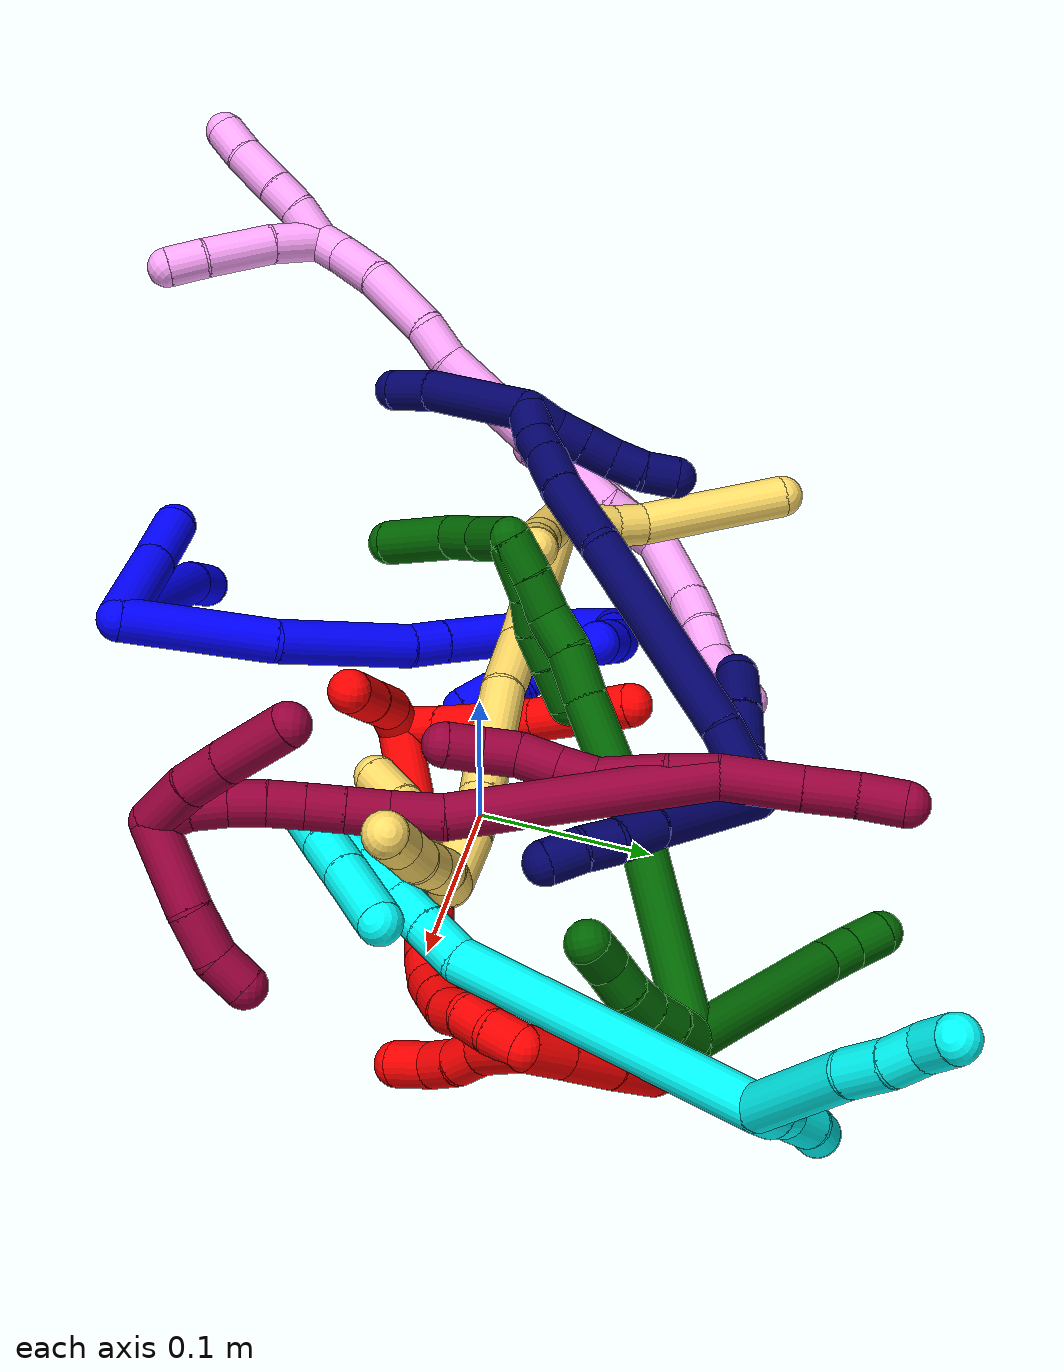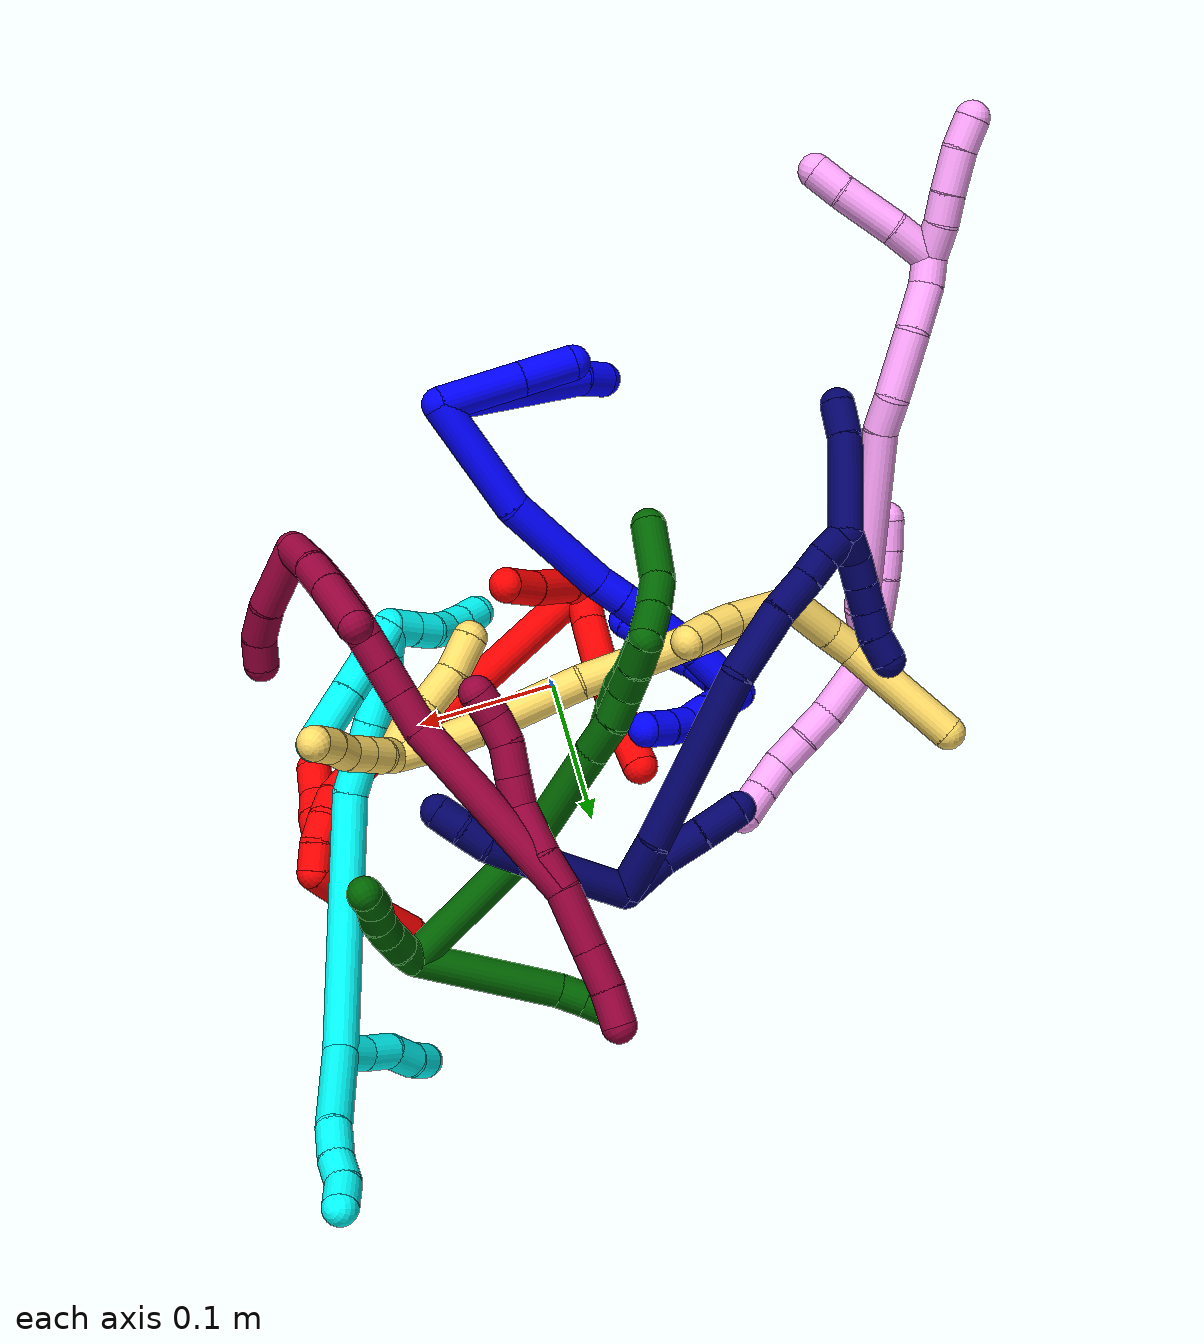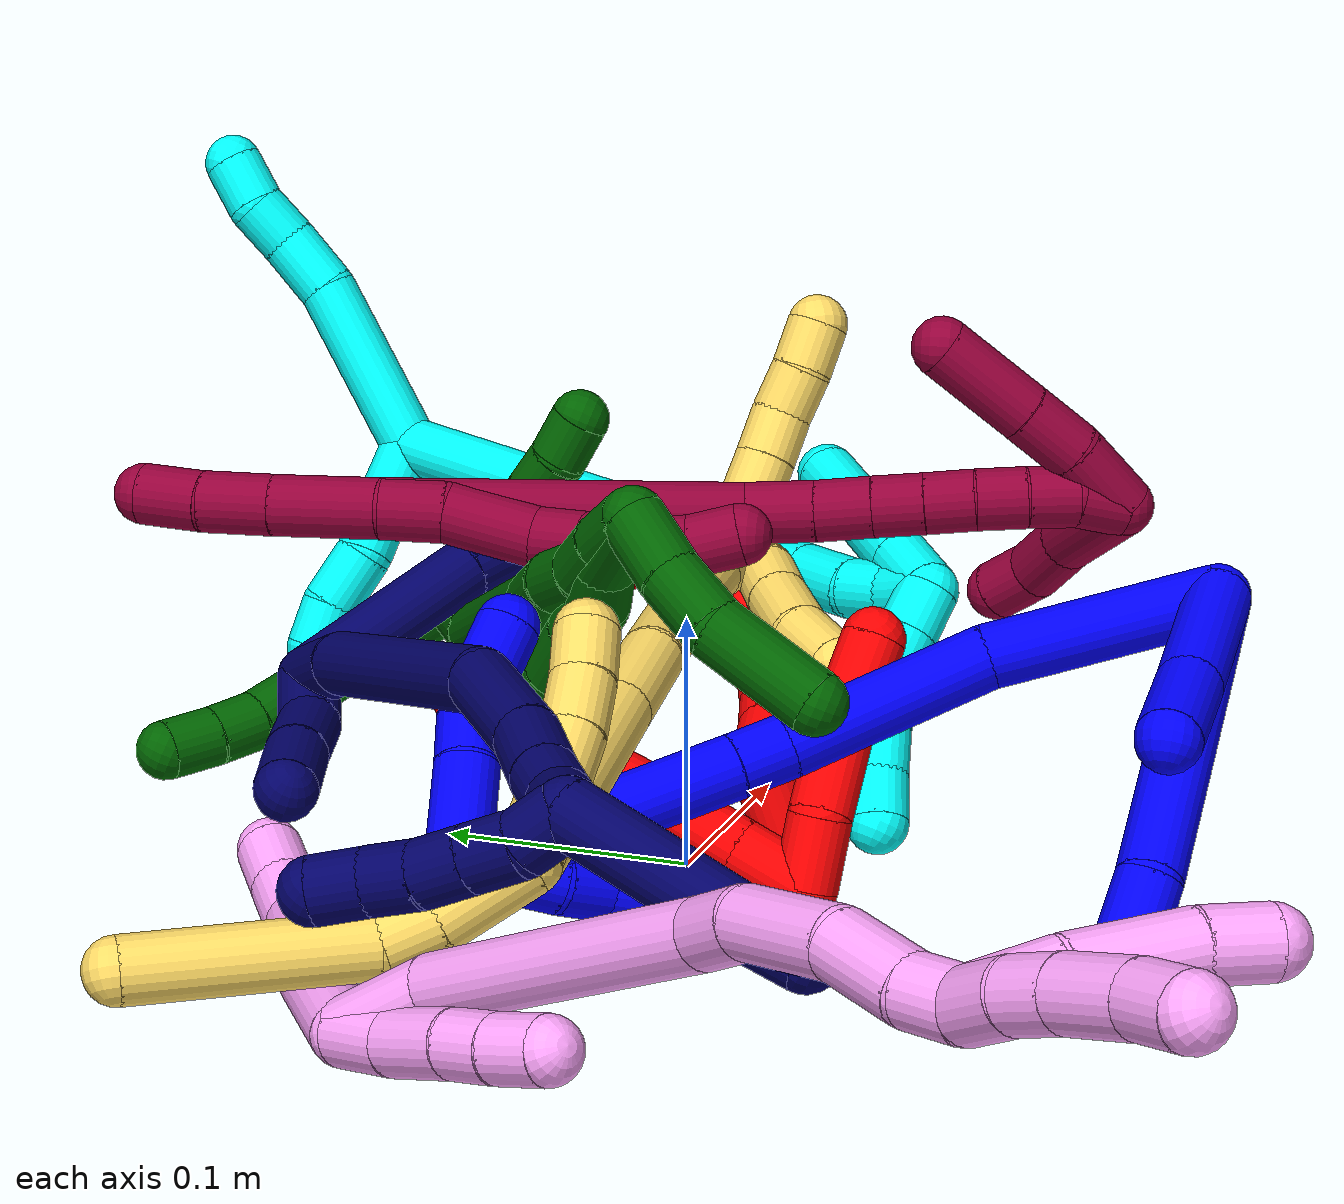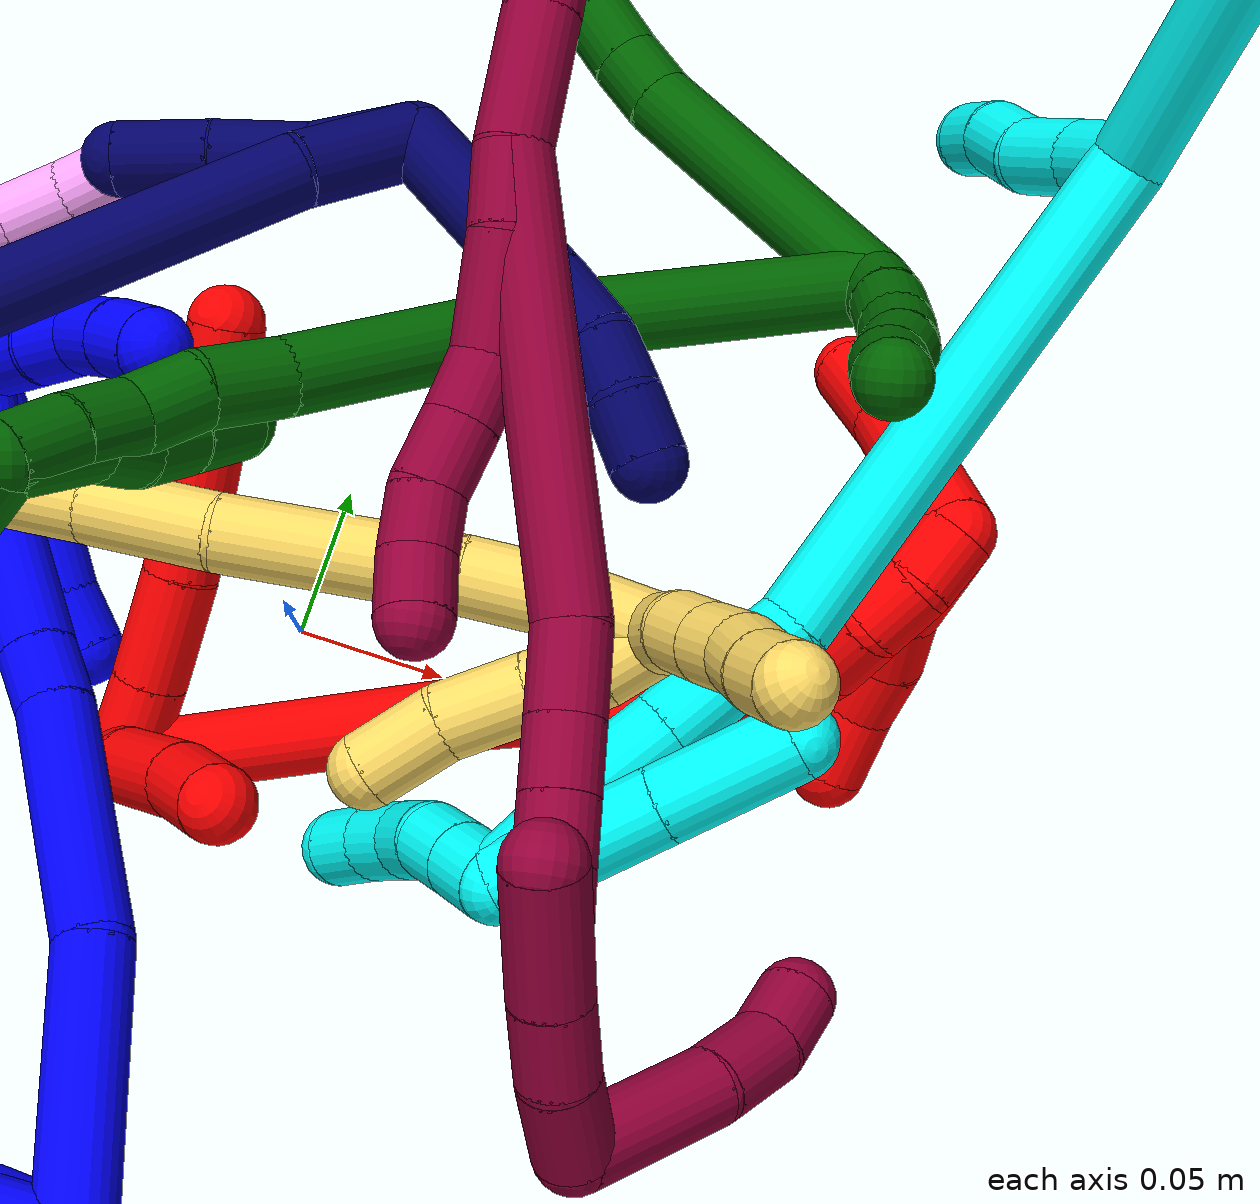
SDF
<sdf version="1.7">
 <world name="default">
  <plugin name="TubeGeneratorPlugin" filename="libtube_generator_plugin.so"/>
  <model name="photoneo_s_sensor">
   <static>1</static>
   <pose>0 0 2 1.57079 1.57079 3.14159</pose>
   <link name="link">
    <inertial><mass>0.1</mass></inertial>
    <sensor name="sensor" type="depth">
     <update_rate>30</update_rate>
     <camera>
      <horizontal_fov>1.22</horizontal_fov>
      <image><width>1920</width><height>1200</height><format>B8G8R8</format></image>
      <clip><near>0.1</near><far>4</far></clip>
      <depth_camera><output>points</output></depth_camera>
     </camera>
     <plugin name="camera_plugin" filename="libgazebo_ros_depth_camera.so">
      <baseline>0.2</baseline>
      <alwaysOn>1</alwaysOn>
      <updateRate>0.0</updateRate>
      <cameraName>camera_ir</cameraName>
      <imageTopicName>/camera/color/image_raw</imageTopicName>
      <cameraInfoTopicName>/camera/color/camera_info</cameraInfoTopicName>
      <depthImageTopicName>/camera/depth/image_raw</depthImageTopicName>
      <depthImageCameraInfoTopicName>/camera/depth/camera_info</depthImageCameraInfoTopicName>
      <pointCloudTopicName>/camera/depth/points</pointCloudTopicName>
      <frameName>fr_optical</frameName>
      <pointCloudCutoff>0.1</pointCloudCutoff>
      <pointCloudCutoffMax>2.0</pointCloudCutoffMax>
      <distortionK1>0</distortionK1>
      <distortionK2>0</distortionK2>
      <distortionK3>0</distortionK3>
      <distortionT1>0</distortionT1>
      <distortionT2>0</distortionT2>
      <CxPrime>0</CxPrime>
      <Cx>0</Cx>
      <Cy>0</Cy>
      <focalLength>0</focalLength>
      <hackBaseline>0</hackBaseline>
     </plugin>
    </sensor>
   </link>
  </model>
  <gravity>0 0 -9.8</gravity>
  <magnetic_field>6e-06 2.3e-05 -4.2e-05</magnetic_field>
  <atmosphere type="adiabatic"/>
  <physics name="default_physics" default="0" type="ode">
   <max_step_size>0.003</max_step_size>
   <real_time_factor>1</real_time_factor>
   <real_time_update_rate>1000</real_time_update_rate>
   <max_contacts>10000</max_contacts>
   <ode>
    <solver>
     <type>quick</type>
     <iters>100</iters>
     <sor>1.3</sor>
     <use_dynamic_moi_rescaling>0</use_dynamic_moi_rescaling>
    </solver>
    <constraints>
     <contact_max_correcting_vel>0</contact_max_correcting_vel>
     <contact_surface_layer>0.001</contact_surface_layer>
     <cfm>0</cfm>
     <erp>0.2</erp>
    </constraints>
   </ode>
  </physics>
  <scene><ambient>0.4 0.4 0.4 1</ambient><background>0.7 0.7 0.7 1</background><shadows>0</shadows></scene>
  <audio><device>default</device></audio>
  <spherical_coordinates>
   <surface_model>EARTH_WGS84</surface_model>
   <latitude_deg>0</latitude_deg>
   <longitude_deg>0</longitude_deg>
   <elevation>0</elevation>
   <heading_deg>0</heading_deg>
  </spherical_coordinates>
  <model name="bin">
   <static>1</static>
   <link name="bottom">
    <collision name="collision-bottom">
     <pose>0 0 -0.01 0 -0 0</pose>
     <geometry><box><size>0.8 0.6 0.02</size></box></geometry>
     <surface>
      <friction><ode><mu>100</mu><mu2>100</mu2></ode></friction>
      <contact><collide_bitmask>65535</collide_bitmask></contact>
     </surface>
    </collision>
   </link>
   <link name="west_wall">
    <collision name="collision-west_wall">
     <pose>-0.41 0 0.1 0 -0 0</pose>
     <geometry><box><size>0.02 0.6 0.2</size></box></geometry>
     <surface>
      <friction><ode><mu>100</mu><mu2>100</mu2></ode></friction>
      <contact><collide_bitmask>65535</collide_bitmask></contact>
     </surface>
    </collision>
   </link>
   <link name="east_wall">
    <collision name="collision-east_wall">
     <pose>0.41 0 0.1 0 -0 0</pose>
     <geometry><box><size>0.02 0.6 0.2</size></box></geometry>
     <surface>
      <friction><ode><mu>100</mu><mu2>100</mu2></ode></friction>
      <contact><collide_bitmask>65535</collide_bitmask></contact>
     </surface>
    </collision>
   </link>
   <link name="south_wall">
    <collision name="collision-south_wall">
     <pose>0 -0.31 0.1 0 -0 0</pose>
     <geometry><box><size>0.8 0.02 0.2</size></box></geometry>
     <surface>
      <friction><ode><mu>100</mu><mu2>100</mu2></ode></friction>
      <contact><collide_bitmask>65535</collide_bitmask></contact>
     </surface>
    </collision>
   </link>
   <link name="north_wall">
    <collision name="collision-north_wall">
     <pose>0 0.31 0.1 0 -0 0</pose>
     <geometry><box><size>0.8 0.02 0.2</size></box></geometry>
     <surface>
      <friction><ode><mu>100</mu><mu2>100</mu2></ode></friction>
      <contact><collide_bitmask>65535</collide_bitmask></contact>
     </surface>
    </collision>
   </link>
  </model>
  <model name="1">
   <static>0</static>
   <link name="1">
    <collision name="collision-cylinder-e_1_2_8">
     <pose>-0.020503 -4.3e-05 -0.059467 3.14088 -0.332022 -3.13732</pose>
     <geometry><cylinder><radius>0.0125</radius><length>0.125804</length></cylinder></geometry>
     <surface>
      <friction><ode><mu>1.16</mu><mu2>1.16</mu2><slip1>0</slip1><slip2>0</slip2></ode></friction>
      <contact><ode><kp>1e+06</kp><kd>1</kd><max_vel>0</max_vel><min_depth>0.001</min_depth></ode></contact>
     </surface>
    </collision>
    <visual name="visual-cylinder-e_1_2_8">
     <pose>-0.020503 -4.3e-05 -0.059467 3.14088 -0.332022 -3.13732</pose>
     <geometry><cylinder><radius>0.0125</radius><length>0.125804</length></cylinder></geometry>
     <material><ambient>0 0 1 1</ambient></material>
    </visual>
    <collision name="collision-cylinder-e_2_8_6">
     <pose>-0.0425 0.001478 -0.130837 -3.01102 -0.123744 1.51695</pose>
     <geometry><cylinder><radius>0.0125</radius><length>0.024196</length></cylinder></geometry>
     <surface>
      <friction><ode><mu>1.16</mu><mu2>1.16</mu2><slip1>0</slip1><slip2>0</slip2></ode></friction>
      <contact><ode><kp>1e+06</kp><kd>1</kd><max_vel>0</max_vel><min_depth>0.001</min_depth></ode></contact>
     </surface>
    </collision>
    <visual name="visual-cylinder-e_2_8_6">
     <pose>-0.0425 0.001478 -0.130837 -3.01102 -0.123744 1.51695</pose>
     <geometry><cylinder><radius>0.0125</radius><length>0.024196</length></cylinder></geometry>
     <material><ambient>0 0 1 1</ambient></material>
    </visual>
    <collision name="collision-cylinder-e_1_2_9">
     <pose>-0.019879 -0.00167 -0.023151 3.06956 -0.708234 -2.94729</pose>
     <geometry><cylinder><radius>0.0125</radius><length>0.061121</length></cylinder></geometry>
     <surface>
      <friction><ode><mu>1.16</mu><mu2>1.16</mu2><slip1>0</slip1><slip2>0</slip2></ode></friction>
      <contact><ode><kp>1e+06</kp><kd>1</kd><max_vel>0</max_vel><min_depth>0.001</min_depth></ode></contact>
     </surface>
    </collision>
    <visual name="visual-cylinder-e_1_2_9">
     <pose>-0.019879 -0.00167 -0.023151 3.06956 -0.708234 -2.94729</pose>
     <geometry><cylinder><radius>0.0125</radius><length>0.061121</length></cylinder></geometry>
     <material><ambient>0 0 1 1</ambient></material>
    </visual>
    <collision name="collision-cylinder-e_2_9_5">
     <pose>-0.053195 -0.004271 -0.06032 3.07534 -0.7631 -2.97678</pose>
     <geometry><cylinder><radius>0.0125</radius><length>0.038879</length></cylinder></geometry>
     <surface>
      <friction><ode><mu>1.16</mu><mu2>1.16</mu2><slip1>0</slip1><slip2>0</slip2></ode></friction>
      <contact><ode><kp>1e+06</kp><kd>1</kd><max_vel>0</max_vel><min_depth>0.001</min_depth></ode></contact>
     </surface>
    </collision>
    <visual name="visual-cylinder-e_2_9_5">
     <pose>-0.053195 -0.004271 -0.06032 3.07534 -0.7631 -2.97678</pose>
     <geometry><cylinder><radius>0.0125</radius><length>0.038879</length></cylinder></geometry>
     <material><ambient>0 0 1 1</ambient></material>
    </visual>
    <collision name="collision-cylinder-e_1_2_10">
     <pose>-0.005545 0.040185 -0.017237 -1.97599 -0.126151 0.191046</pose>
     <geometry><cylinder><radius>0.0125</radius><length>0.088152</length></cylinder></geometry>
     <surface>
      <friction><ode><mu>1.16</mu><mu2>1.16</mu2><slip1>0</slip1><slip2>0</slip2></ode></friction>
      <contact><ode><kp>1e+06</kp><kd>1</kd><max_vel>0</max_vel><min_depth>0.001</min_depth></ode></contact>
     </surface>
    </collision>
    <visual name="visual-cylinder-e_1_2_10">
     <pose>-0.005545 0.040185 -0.017237 -1.97599 -0.126151 0.191046</pose>
     <geometry><cylinder><radius>0.0125</radius><length>0.088152</length></cylinder></geometry>
     <material><ambient>0 0 1 1</ambient></material>
    </visual>
    <collision name="collision-cylinder-e_2_10_11">
     <pose>-0.020604 0.112642 -0.057937 -2.19945 -0.234057 0.453717</pose>
     <geometry><cylinder><radius>0.0125</radius><length>0.082037</length></cylinder></geometry>
     <surface>
      <friction><ode><mu>1.16</mu><mu2>1.16</mu2><slip1>0</slip1><slip2>0</slip2></ode></friction>
      <contact><ode><kp>1e+06</kp><kd>1</kd><max_vel>0</max_vel><min_depth>0.001</min_depth></ode></contact>
     </surface>
    </collision>
    <visual name="visual-cylinder-e_2_10_11">
     <pose>-0.020604 0.112642 -0.057937 -2.19945 -0.234057 0.453717</pose>
     <geometry><cylinder><radius>0.0125</radius><length>0.082037</length></cylinder></geometry>
     <material><ambient>0 0 1 1</ambient></material>
    </visual>
    <collision name="collision-cylinder-e_3_11_12">
     <pose>-0.034095 0.15281 -0.087325 -2.21448 -0.383007 0.739968</pose>
     <geometry><cylinder><radius>0.0125</radius><length>0.021287</length></cylinder></geometry>
     <surface>
      <friction><ode><mu>1.16</mu><mu2>1.16</mu2><slip1>0</slip1><slip2>0</slip2></ode></friction>
      <contact><ode><kp>1e+06</kp><kd>1</kd><max_vel>0</max_vel><min_depth>0.001</min_depth></ode></contact>
     </surface>
    </collision>
    <visual name="visual-cylinder-e_3_11_12">
     <pose>-0.034095 0.15281 -0.087325 -2.21448 -0.383007 0.739968</pose>
     <geometry><cylinder><radius>0.0125</radius><length>0.021287</length></cylinder></geometry>
     <material><ambient>0 0 1 1</ambient></material>
    </visual>
    <collision name="collision-cylinder-e_4_12_13">
     <pose>-0.049864 0.186027 -0.111186 -2.18712 -0.363149 0.682331</pose>
     <geometry><cylinder><radius>0.0125</radius><length>0.066388</length></cylinder></geometry>
     <surface>
      <friction><ode><mu>1.16</mu><mu2>1.16</mu2><slip1>0</slip1><slip2>0</slip2></ode></friction>
      <contact><ode><kp>1e+06</kp><kd>1</kd><max_vel>0</max_vel><min_depth>0.001</min_depth></ode></contact>
     </surface>
    </collision>
    <visual name="visual-cylinder-e_4_12_13">
     <pose>-0.049864 0.186027 -0.111186 -2.18712 -0.363149 0.682331</pose>
     <geometry><cylinder><radius>0.0125</radius><length>0.066388</length></cylinder></geometry>
     <material><ambient>0 0 1 1</ambient></material>
    </visual>
    <collision name="collision-cylinder-e_5_13_1">
     <pose>-0.067723 0.229066 -0.13877 -2.06943 -0.292189 0.485562</pose>
     <geometry><cylinder><radius>0.0125</radius><length>0.042137</length></cylinder></geometry>
     <surface>
      <friction><ode><mu>1.16</mu><mu2>1.16</mu2><slip1>0</slip1><slip2>0</slip2></ode></friction>
      <contact><ode><kp>1e+06</kp><kd>1</kd><max_vel>0</max_vel><min_depth>0.001</min_depth></ode></contact>
     </surface>
    </collision>
    <visual name="visual-cylinder-e_5_13_1">
     <pose>-0.067723 0.229066 -0.13877 -2.06943 -0.292189 0.485562</pose>
     <geometry><cylinder><radius>0.0125</radius><length>0.042137</length></cylinder></geometry>
     <material><ambient>0 0 1 1</ambient></material>
    </visual>
    <collision name="collision-cylinder-e_1_1_14">
     <pose>-0.067252 0.239271 -0.147542 1.45471 0.712909 0.640131</pose>
     <geometry><cylinder><radius>0.0125</radius><length>0.02</length></cylinder></geometry>
     <surface>
      <friction><ode><mu>1.16</mu><mu2>1.16</mu2><slip1>0</slip1><slip2>0</slip2></ode></friction>
      <contact><ode><kp>1e+06</kp><kd>1</kd><max_vel>0</max_vel><min_depth>0.001</min_depth></ode></contact>
     </surface>
    </collision>
    <visual name="visual-cylinder-e_1_1_14">
     <pose>-0.067252 0.239271 -0.147542 1.45471 0.712909 0.640131</pose>
     <geometry><cylinder><radius>0.0125</radius><length>0.02</length></cylinder></geometry>
     <material><ambient>0 0 1 1</ambient></material>
    </visual>
    <collision name="collision-cylinder-e_2_14_15">
     <pose>-0.054228 0.224153 -0.146296 1.52216 0.705379 0.674415</pose>
     <geometry><cylinder><radius>0.0125</radius><length>0.02</length></cylinder></geometry>
     <surface>
      <friction><ode><mu>1.16</mu><mu2>1.16</mu2><slip1>0</slip1><slip2>0</slip2></ode></friction>
      <contact><ode><kp>1e+06</kp><kd>1</kd><max_vel>0</max_vel><min_depth>0.001</min_depth></ode></contact>
     </surface>
    </collision>
    <visual name="visual-cylinder-e_2_14_15">
     <pose>-0.054228 0.224153 -0.146296 1.52216 0.705379 0.674415</pose>
     <geometry><cylinder><radius>0.0125</radius><length>0.02</length></cylinder></geometry>
     <material><ambient>0 0 1 1</ambient></material>
    </visual>
    <collision name="collision-cylinder-e_3_15_16">
     <pose>-0.040201 0.21014 -0.144505 1.35267 0.854785 0.700954</pose>
     <geometry><cylinder><radius>0.0125</radius><length>0.02</length></cylinder></geometry>
     <surface>
      <friction><ode><mu>1.16</mu><mu2>1.16</mu2><slip1>0</slip1><slip2>0</slip2></ode></friction>
      <contact><ode><kp>1e+06</kp><kd>1</kd><max_vel>0</max_vel><min_depth>0.001</min_depth></ode></contact>
     </surface>
    </collision>
    <visual name="visual-cylinder-e_3_15_16">
     <pose>-0.040201 0.21014 -0.144505 1.35267 0.854785 0.700954</pose>
     <geometry><cylinder><radius>0.0125</radius><length>0.02</length></cylinder></geometry>
     <material><ambient>0 0 1 1</ambient></material>
    </visual>
    <collision name="collision-cylinder-e_4_16_17">
     <pose>-0.026773 0.19569 -0.14224 1.46604 0.628996 0.569836</pose>
     <geometry><cylinder><radius>0.0125</radius><length>0.02</length></cylinder></geometry>
     <surface>
      <friction><ode><mu>1.16</mu><mu2>1.16</mu2><slip1>0</slip1><slip2>0</slip2></ode></friction>
      <contact><ode><kp>1e+06</kp><kd>1</kd><max_vel>0</max_vel><min_depth>0.001</min_depth></ode></contact>
     </surface>
    </collision>
    <visual name="visual-cylinder-e_4_16_17">
     <pose>-0.026773 0.19569 -0.14224 1.46604 0.628996 0.569836</pose>
     <geometry><cylinder><radius>0.0125</radius><length>0.02</length></cylinder></geometry>
     <material><ambient>0 0 1 1</ambient></material>
    </visual>
    <collision name="collision-cylinder-e_5_17_4">
     <pose>-0.013996 0.180615 -0.139658 1.32876 0.760677 0.606877</pose>
     <geometry><cylinder><radius>0.0125</radius><length>0.02</length></cylinder></geometry>
     <surface>
      <friction><ode><mu>1.16</mu><mu2>1.16</mu2><slip1>0</slip1><slip2>0</slip2></ode></friction>
      <contact><ode><kp>1e+06</kp><kd>1</kd><max_vel>0</max_vel><min_depth>0.001</min_depth></ode></contact>
     </surface>
    </collision>
    <visual name="visual-cylinder-e_5_17_4">
     <pose>-0.013996 0.180615 -0.139658 1.32876 0.760677 0.606877</pose>
     <geometry><cylinder><radius>0.0125</radius><length>0.02</length></cylinder></geometry>
     <material><ambient>0 0 1 1</ambient></material>
    </visual>
    <collision name="collision-cylinder-e_1_1_18">
     <pose>-0.070276 0.25016 -0.129486 -0.17641 0.180846 -0.016036</pose>
     <geometry><cylinder><radius>0.0125</radius><length>0.0391</length></cylinder></geometry>
     <surface>
      <friction><ode><mu>1.16</mu><mu2>1.16</mu2><slip1>0</slip1><slip2>0</slip2></ode></friction>
      <contact><ode><kp>1e+06</kp><kd>1</kd><max_vel>0</max_vel><min_depth>0.001</min_depth></ode></contact>
     </surface>
    </collision>
    <visual name="visual-cylinder-e_1_1_18">
     <pose>-0.070276 0.25016 -0.129486 -0.17641 0.180846 -0.016036</pose>
     <geometry><cylinder><radius>0.0125</radius><length>0.0391</length></cylinder></geometry>
     <material><ambient>0 0 1 1</ambient></material>
    </visual>
    <collision name="collision-cylinder-e_2_18_19">
     <pose>-0.063811 0.256043 -0.101101 -0.259417 0.292885 -0.038475</pose>
     <geometry><cylinder><radius>0.0125</radius><length>0.020429</length></cylinder></geometry>
     <surface>
      <friction><ode><mu>1.16</mu><mu2>1.16</mu2><slip1>0</slip1><slip2>0</slip2></ode></friction>
      <contact><ode><kp>1e+06</kp><kd>1</kd><max_vel>0</max_vel><min_depth>0.001</min_depth></ode></contact>
     </surface>
    </collision>
    <visual name="visual-cylinder-e_2_18_19">
     <pose>-0.063811 0.256043 -0.101101 -0.259417 0.292885 -0.038475</pose>
     <geometry><cylinder><radius>0.0125</radius><length>0.020429</length></cylinder></geometry>
     <material><ambient>0 0 1 1</ambient></material>
    </visual>
    <collision name="collision-cylinder-e_3_19_20">
     <pose>-0.059001 0.257875 -0.081681 0.067759 0.184075 0.006256</pose>
     <geometry><cylinder><radius>0.0125</radius><length>0.020325</length></cylinder></geometry>
     <surface>
      <friction><ode><mu>1.16</mu><mu2>1.16</mu2><slip1>0</slip1><slip2>0</slip2></ode></friction>
      <contact><ode><kp>1e+06</kp><kd>1</kd><max_vel>0</max_vel><min_depth>0.001</min_depth></ode></contact>
     </surface>
    </collision>
    <visual name="visual-cylinder-e_3_19_20">
     <pose>-0.059001 0.257875 -0.081681 0.067759 0.184075 0.006256</pose>
     <geometry><cylinder><radius>0.0125</radius><length>0.020325</length></cylinder></geometry>
     <material><ambient>0 0 1 1</ambient></material>
    </visual>
    <collision name="collision-cylinder-e_4_20_3">
     <pose>-0.054936 0.255748 -0.061992 0.148131 0.220722 0.016444</pose>
     <geometry><cylinder><radius>0.0125</radius><length>0.020146</length></cylinder></geometry>
     <surface>
      <friction><ode><mu>1.16</mu><mu2>1.16</mu2><slip1>0</slip1><slip2>0</slip2></ode></friction>
      <contact><ode><kp>1e+06</kp><kd>1</kd><max_vel>0</max_vel><min_depth>0.001</min_depth></ode></contact>
     </surface>
    </collision>
    <visual name="visual-cylinder-e_4_20_3">
     <pose>-0.054936 0.255748 -0.061992 0.148131 0.220722 0.016444</pose>
     <geometry><cylinder><radius>0.0125</radius><length>0.020146</length></cylinder></geometry>
     <material><ambient>0 0 1 1</ambient></material>
    </visual>
    <collision name="collision-sphere-3">
     <pose>-0.05273 0.254298 -0.052271 0 -0 0</pose>
     <geometry><sphere><radius>0.0125</radius></sphere></geometry>
     <surface>
      <friction><ode><mu>1.16</mu><mu2>1.16</mu2><slip1>0</slip1><slip2>0</slip2></ode></friction>
      <contact><ode><kp>1e+06</kp><kd>1</kd><max_vel>0</max_vel><min_depth>0.001</min_depth></ode></contact>
     </surface>
    </collision>
    <visual name="visual-sphere-3">
     <pose>-0.05273 0.254298 -0.052271 0 -0 0</pose>
     <geometry><sphere><radius>0.0125</radius></sphere></geometry>
     <material><ambient>0 0 1 1</ambient></material>
    </visual>
    <collision name="collision-sphere-20">
     <pose>-0.057141 0.257199 -0.071713 0 -0 0</pose>
     <geometry><sphere><radius>0.0125</radius></sphere></geometry>
     <surface>
      <friction><ode><mu>1.16</mu><mu2>1.16</mu2><slip1>0</slip1><slip2>0</slip2></ode></friction>
      <contact><ode><kp>1e+06</kp><kd>1</kd><max_vel>0</max_vel><min_depth>0.001</min_depth></ode></contact>
     </surface>
    </collision>
    <visual name="visual-sphere-20">
     <pose>-0.057141 0.257199 -0.071713 0 -0 0</pose>
     <geometry><sphere><radius>0.0125</radius></sphere></geometry>
     <material><ambient>0 0 1 1</ambient></material>
    </visual>
    <collision name="collision-sphere-19">
     <pose>-0.060861 0.258552 -0.091649 0 -0 0</pose>
     <geometry><sphere><radius>0.0125</radius></sphere></geometry>
     <surface>
      <friction><ode><mu>1.16</mu><mu2>1.16</mu2><slip1>0</slip1><slip2>0</slip2></ode></friction>
      <contact><ode><kp>1e+06</kp><kd>1</kd><max_vel>0</max_vel><min_depth>0.001</min_depth></ode></contact>
     </surface>
    </collision>
    <visual name="visual-sphere-19">
     <pose>-0.060861 0.258552 -0.091649 0 -0 0</pose>
     <geometry><sphere><radius>0.0125</radius></sphere></geometry>
     <material><ambient>0 0 1 1</ambient></material>
    </visual>
    <collision name="collision-sphere-10">
     <pose>-0.011091 0.08037 -0.034473 0 -0 0</pose>
     <geometry><sphere><radius>0.0125</radius></sphere></geometry>
     <surface>
      <friction><ode><mu>1.16</mu><mu2>1.16</mu2><slip1>0</slip1><slip2>0</slip2></ode></friction>
      <contact><ode><kp>1e+06</kp><kd>1</kd><max_vel>0</max_vel><min_depth>0.001</min_depth></ode></contact>
     </surface>
    </collision>
    <visual name="visual-sphere-10">
     <pose>-0.011091 0.08037 -0.034473 0 -0 0</pose>
     <geometry><sphere><radius>0.0125</radius></sphere></geometry>
     <material><ambient>0 0 1 1</ambient></material>
    </visual>
    <collision name="collision-sphere-5">
     <pose>-0.066631 -0.005201 -0.074338 0 -0 0</pose>
     <geometry><sphere><radius>0.0125</radius></sphere></geometry>
     <surface>
      <friction><ode><mu>1.16</mu><mu2>1.16</mu2><slip1>0</slip1><slip2>0</slip2></ode></friction>
      <contact><ode><kp>1e+06</kp><kd>1</kd><max_vel>0</max_vel><min_depth>0.001</min_depth></ode></contact>
     </surface>
    </collision>
    <visual name="visual-sphere-5">
     <pose>-0.066631 -0.005201 -0.074338 0 -0 0</pose>
     <geometry><sphere><radius>0.0125</radius></sphere></geometry>
     <material><ambient>0 0 1 1</ambient></material>
    </visual>
    <collision name="collision-sphere-6">
     <pose>-0.043993 0.003041 -0.14274 0 -0 0</pose>
     <geometry><sphere><radius>0.0125</radius></sphere></geometry>
     <surface>
      <friction><ode><mu>1.16</mu><mu2>1.16</mu2><slip1>0</slip1><slip2>0</slip2></ode></friction>
      <contact><ode><kp>1e+06</kp><kd>1</kd><max_vel>0</max_vel><min_depth>0.001</min_depth></ode></contact>
     </surface>
    </collision>
    <visual name="visual-sphere-6">
     <pose>-0.043993 0.003041 -0.14274 0 -0 0</pose>
     <geometry><sphere><radius>0.0125</radius></sphere></geometry>
     <material><ambient>0 0 1 1</ambient></material>
    </visual>
    <collision name="collision-sphere-9">
     <pose>-0.039759 -0.003341 -0.046302 0 -0 0</pose>
     <geometry><sphere><radius>0.0125</radius></sphere></geometry>
     <surface>
      <friction><ode><mu>1.16</mu><mu2>1.16</mu2><slip1>0</slip1><slip2>0</slip2></ode></friction>
      <contact><ode><kp>1e+06</kp><kd>1</kd><max_vel>0</max_vel><min_depth>0.001</min_depth></ode></contact>
     </surface>
    </collision>
    <visual name="visual-sphere-9">
     <pose>-0.039759 -0.003341 -0.046302 0 -0 0</pose>
     <geometry><sphere><radius>0.0125</radius></sphere></geometry>
     <material><ambient>0 0 1 1</ambient></material>
    </visual>
    <collision name="collision-sphere-2">
     <geometry><sphere><radius>0.0125</radius></sphere></geometry>
     <surface>
      <friction><ode><mu>1.16</mu><mu2>1.16</mu2><slip1>0</slip1><slip2>0</slip2></ode></friction>
      <contact><ode><kp>1e+06</kp><kd>1</kd><max_vel>0</max_vel><min_depth>0.001</min_depth></ode></contact>
     </surface>
    </collision>
    <visual name="visual-sphere-2">
     <geometry><sphere><radius>0.0125</radius></sphere></geometry>
     <material><ambient>0 0 1 1</ambient></material>
    </visual>
    <collision name="collision-sphere-8">
     <pose>-0.041007 -8.5e-05 -0.118933 0 -0 0</pose>
     <geometry><sphere><radius>0.0125</radius></sphere></geometry>
     <surface>
      <friction><ode><mu>1.16</mu><mu2>1.16</mu2><slip1>0</slip1><slip2>0</slip2></ode></friction>
      <contact><ode><kp>1e+06</kp><kd>1</kd><max_vel>0</max_vel><min_depth>0.001</min_depth></ode></contact>
     </surface>
    </collision>
    <visual name="visual-sphere-8">
     <pose>-0.041007 -8.5e-05 -0.118933 0 -0 0</pose>
     <geometry><sphere><radius>0.0125</radius></sphere></geometry>
     <material><ambient>0 0 1 1</ambient></material>
    </visual>
    <collision name="collision-sphere-11">
     <pose>-0.030117 0.144914 -0.0814 0 -0 0</pose>
     <geometry><sphere><radius>0.0125</radius></sphere></geometry>
     <surface>
      <friction><ode><mu>1.16</mu><mu2>1.16</mu2><slip1>0</slip1><slip2>0</slip2></ode></friction>
      <contact><ode><kp>1e+06</kp><kd>1</kd><max_vel>0</max_vel><min_depth>0.001</min_depth></ode></contact>
     </surface>
    </collision>
    <visual name="visual-sphere-11">
     <pose>-0.030117 0.144914 -0.0814 0 -0 0</pose>
     <geometry><sphere><radius>0.0125</radius></sphere></geometry>
     <material><ambient>0 0 1 1</ambient></material>
    </visual>
    <collision name="collision-sphere-12">
     <pose>-0.038072 0.160707 -0.09325 0 -0 0</pose>
     <geometry><sphere><radius>0.0125</radius></sphere></geometry>
     <surface>
      <friction><ode><mu>1.16</mu><mu2>1.16</mu2><slip1>0</slip1><slip2>0</slip2></ode></friction>
      <contact><ode><kp>1e+06</kp><kd>1</kd><max_vel>0</max_vel><min_depth>0.001</min_depth></ode></contact>
     </surface>
    </collision>
    <visual name="visual-sphere-12">
     <pose>-0.038072 0.160707 -0.09325 0 -0 0</pose>
     <geometry><sphere><radius>0.0125</radius></sphere></geometry>
     <material><ambient>0 0 1 1</ambient></material>
    </visual>
    <collision name="collision-sphere-13">
     <pose>-0.061655 0.211347 -0.129122 0 -0 0</pose>
     <geometry><sphere><radius>0.0125</radius></sphere></geometry>
     <surface>
      <friction><ode><mu>1.16</mu><mu2>1.16</mu2><slip1>0</slip1><slip2>0</slip2></ode></friction>
      <contact><ode><kp>1e+06</kp><kd>1</kd><max_vel>0</max_vel><min_depth>0.001</min_depth></ode></contact>
     </surface>
    </collision>
    <visual name="visual-sphere-13">
     <pose>-0.061655 0.211347 -0.129122 0 -0 0</pose>
     <geometry><sphere><radius>0.0125</radius></sphere></geometry>
     <material><ambient>0 0 1 1</ambient></material>
    </visual>
    <collision name="collision-sphere-1">
     <pose>-0.073792 0.246785 -0.148419 0 -0 0</pose>
     <geometry><sphere><radius>0.0125</radius></sphere></geometry>
     <surface>
      <friction><ode><mu>1.16</mu><mu2>1.16</mu2><slip1>0</slip1><slip2>0</slip2></ode></friction>
      <contact><ode><kp>1e+06</kp><kd>1</kd><max_vel>0</max_vel><min_depth>0.001</min_depth></ode></contact>
     </surface>
    </collision>
    <visual name="visual-sphere-1">
     <pose>-0.073792 0.246785 -0.148419 0 -0 0</pose>
     <geometry><sphere><radius>0.0125</radius></sphere></geometry>
     <material><ambient>0 0 1 1</ambient></material>
    </visual>
    <collision name="collision-sphere-18">
     <pose>-0.06676 0.253535 -0.110553 0 -0 0</pose>
     <geometry><sphere><radius>0.0125</radius></sphere></geometry>
     <surface>
      <friction><ode><mu>1.16</mu><mu2>1.16</mu2><slip1>0</slip1><slip2>0</slip2></ode></friction>
      <contact><ode><kp>1e+06</kp><kd>1</kd><max_vel>0</max_vel><min_depth>0.001</min_depth></ode></contact>
     </surface>
    </collision>
    <visual name="visual-sphere-18">
     <pose>-0.06676 0.253535 -0.110553 0 -0 0</pose>
     <geometry><sphere><radius>0.0125</radius></sphere></geometry>
     <material><ambient>0 0 1 1</ambient></material>
    </visual>
    <collision name="collision-sphere-14">
     <pose>-0.060711 0.231757 -0.146666 0 -0 0</pose>
     <geometry><sphere><radius>0.0125</radius></sphere></geometry>
     <surface>
      <friction><ode><mu>1.16</mu><mu2>1.16</mu2><slip1>0</slip1><slip2>0</slip2></ode></friction>
      <contact><ode><kp>1e+06</kp><kd>1</kd><max_vel>0</max_vel><min_depth>0.001</min_depth></ode></contact>
     </surface>
    </collision>
    <visual name="visual-sphere-14">
     <pose>-0.060711 0.231757 -0.146666 0 -0 0</pose>
     <geometry><sphere><radius>0.0125</radius></sphere></geometry>
     <material><ambient>0 0 1 1</ambient></material>
    </visual>
    <collision name="collision-sphere-15">
     <pose>-0.047745 0.216548 -0.145926 0 -0 0</pose>
     <geometry><sphere><radius>0.0125</radius></sphere></geometry>
     <surface>
      <friction><ode><mu>1.16</mu><mu2>1.16</mu2><slip1>0</slip1><slip2>0</slip2></ode></friction>
      <contact><ode><kp>1e+06</kp><kd>1</kd><max_vel>0</max_vel><min_depth>0.001</min_depth></ode></contact>
     </surface>
    </collision>
    <visual name="visual-sphere-15">
     <pose>-0.047745 0.216548 -0.145926 0 -0 0</pose>
     <geometry><sphere><radius>0.0125</radius></sphere></geometry>
     <material><ambient>0 0 1 1</ambient></material>
    </visual>
    <collision name="collision-sphere-16">
     <pose>-0.032656 0.203731 -0.143085 0 -0 0</pose>
     <geometry><sphere><radius>0.0125</radius></sphere></geometry>
     <surface>
      <friction><ode><mu>1.16</mu><mu2>1.16</mu2><slip1>0</slip1><slip2>0</slip2></ode></friction>
      <contact><ode><kp>1e+06</kp><kd>1</kd><max_vel>0</max_vel><min_depth>0.001</min_depth></ode></contact>
     </surface>
    </collision>
    <visual name="visual-sphere-16">
     <pose>-0.032656 0.203731 -0.143085 0 -0 0</pose>
     <geometry><sphere><radius>0.0125</radius></sphere></geometry>
     <material><ambient>0 0 1 1</ambient></material>
    </visual>
    <collision name="collision-sphere-17">
     <pose>-0.02089 0.187648 -0.141394 0 -0 0</pose>
     <geometry><sphere><radius>0.0125</radius></sphere></geometry>
     <surface>
      <friction><ode><mu>1.16</mu><mu2>1.16</mu2><slip1>0</slip1><slip2>0</slip2></ode></friction>
      <contact><ode><kp>1e+06</kp><kd>1</kd><max_vel>0</max_vel><min_depth>0.001</min_depth></ode></contact>
     </surface>
    </collision>
    <visual name="visual-sphere-17">
     <pose>-0.02089 0.187648 -0.141394 0 -0 0</pose>
     <geometry><sphere><radius>0.0125</radius></sphere></geometry>
     <material><ambient>0 0 1 1</ambient></material>
    </visual>
    <collision name="collision-sphere-4">
     <pose>-0.007101 0.173583 -0.137922 0 -0 0</pose>
     <geometry><sphere><radius>0.0125</radius></sphere></geometry>
     <surface>
      <friction><ode><mu>1.16</mu><mu2>1.16</mu2><slip1>0</slip1><slip2>0</slip2></ode></friction>
      <contact><ode><kp>1e+06</kp><kd>1</kd><max_vel>0</max_vel><min_depth>0.001</min_depth></ode></contact>
     </surface>
    </collision>
    <visual name="visual-sphere-4">
     <pose>-0.007101 0.173583 -0.137922 0 -0 0</pose>
     <geometry><sphere><radius>0.0125</radius></sphere></geometry>
     <material><ambient>0 0 1 1</ambient></material>
    </visual>
    <inertial>
     <pose>-0.035155 0.112271 -0.080279 0 -0 0</pose>
     <mass>0.75</mass>
     <inertia><ixx>8e-06</ixx><ixy>0</ixy><ixz>0</ixz><iyy>0.000226</iyy><iyz>0</iyz><izz>-3.8e-05</izz></inertia>
    </inertial>
   </link>
   <pose>0.019826 -0.201717 0.124009 -0.016597 0.595963 -0.007305</pose>
  </model>
  <model name="2">
   <static>0</static>
   <link name="2">
    <collision name="collision-cylinder-e_1_2_8">
     <pose>-0.001503 0.013476 0.005632 -1.17492 -0.102576 0.068337</pose>
     <geometry><cylinder><radius>0.0125</radius><length>0.029365</length></cylinder></geometry>
     <surface>
      <friction><ode><mu>1.16</mu><mu2>1.16</mu2><slip1>0</slip1><slip2>0</slip2></ode></friction>
      <contact><ode><kp>1e+06</kp><kd>1</kd><max_vel>0</max_vel><min_depth>0.001</min_depth></ode></contact>
     </surface>
    </collision>
    <visual name="visual-cylinder-e_1_2_8">
     <pose>-0.001503 0.013476 0.005632 -1.17492 -0.102576 0.068337</pose>
     <geometry><cylinder><radius>0.0125</radius><length>0.029365</length></cylinder></geometry>
     <material><ambient>1 0 0 1</ambient></material>
    </visual>
    <collision name="collision-cylinder-e_2_8_9">
     <pose>-0.005235 0.04386 0.019088 -1.13742 -0.119034 0.076134</pose>
     <geometry><cylinder><radius>0.0125</radius><length>0.037528</length></cylinder></geometry>
     <surface>
      <friction><ode><mu>1.16</mu><mu2>1.16</mu2><slip1>0</slip1><slip2>0</slip2></ode></friction>
      <contact><ode><kp>1e+06</kp><kd>1</kd><max_vel>0</max_vel><min_depth>0.001</min_depth></ode></contact>
     </surface>
    </collision>
    <visual name="visual-cylinder-e_2_8_9">
     <pose>-0.005235 0.04386 0.019088 -1.13742 -0.119034 0.076134</pose>
     <geometry><cylinder><radius>0.0125</radius><length>0.037528</length></cylinder></geometry>
     <material><ambient>1 0 0 1</ambient></material>
    </visual>
    <collision name="collision-cylinder-e_3_9_10">
     <pose>-0.010063 0.071176 0.032015 -1.1149 -0.22061 0.13787</pose>
     <geometry><cylinder><radius>0.0125</radius><length>0.023757</length></cylinder></geometry>
     <surface>
      <friction><ode><mu>1.16</mu><mu2>1.16</mu2><slip1>0</slip1><slip2>0</slip2></ode></friction>
      <contact><ode><kp>1e+06</kp><kd>1</kd><max_vel>0</max_vel><min_depth>0.001</min_depth></ode></contact>
     </surface>
    </collision>
    <visual name="visual-cylinder-e_3_9_10">
     <pose>-0.010063 0.071176 0.032015 -1.1149 -0.22061 0.13787</pose>
     <geometry><cylinder><radius>0.0125</radius><length>0.023757</length></cylinder></geometry>
     <material><ambient>1 0 0 1</ambient></material>
    </visual>
    <collision name="collision-cylinder-e_4_10_11">
     <pose>-0.016083 0.09701 0.045114 -1.0926 -0.194369 0.118417</pose>
     <geometry><cylinder><radius>0.0125</radius><length>0.035418</length></cylinder></geometry>
     <surface>
      <friction><ode><mu>1.16</mu><mu2>1.16</mu2><slip1>0</slip1><slip2>0</slip2></ode></friction>
      <contact><ode><kp>1e+06</kp><kd>1</kd><max_vel>0</max_vel><min_depth>0.001</min_depth></ode></contact>
     </surface>
    </collision>
    <visual name="visual-cylinder-e_4_10_11">
     <pose>-0.016083 0.09701 0.045114 -1.0926 -0.194369 0.118417</pose>
     <geometry><cylinder><radius>0.0125</radius><length>0.035418</length></cylinder></geometry>
     <material><ambient>1 0 0 1</ambient></material>
    </visual>
    <collision name="collision-cylinder-e_5_11_6">
     <pose>-0.02218 0.122655 0.05873 -1.06797 -0.225593 0.133757</pose>
     <geometry><cylinder><radius>0.0125</radius><length>0.023931</length></cylinder></geometry>
     <surface>
      <friction><ode><mu>1.16</mu><mu2>1.16</mu2><slip1>0</slip1><slip2>0</slip2></ode></friction>
      <contact><ode><kp>1e+06</kp><kd>1</kd><max_vel>0</max_vel><min_depth>0.001</min_depth></ode></contact>
     </surface>
    </collision>
    <visual name="visual-cylinder-e_5_11_6">
     <pose>-0.02218 0.122655 0.05873 -1.06797 -0.225593 0.133757</pose>
     <geometry><cylinder><radius>0.0125</radius><length>0.023931</length></cylinder></geometry>
     <material><ambient>1 0 0 1</ambient></material>
    </visual>
    <collision name="collision-cylinder-e_1_2_12">
     <pose>0.00908 0.001141 0.0107 -0.106206 0.700915 -0.038855</pose>
     <geometry><cylinder><radius>0.0125</radius><length>0.02816</length></cylinder></geometry>
     <surface>
      <friction><ode><mu>1.16</mu><mu2>1.16</mu2><slip1>0</slip1><slip2>0</slip2></ode></friction>
      <contact><ode><kp>1e+06</kp><kd>1</kd><max_vel>0</max_vel><min_depth>0.001</min_depth></ode></contact>
     </surface>
    </collision>
    <visual name="visual-cylinder-e_1_2_12">
     <pose>0.00908 0.001141 0.0107 -0.106206 0.700915 -0.038855</pose>
     <geometry><cylinder><radius>0.0125</radius><length>0.02816</length></cylinder></geometry>
     <material><ambient>1 0 0 1</ambient></material>
    </visual>
    <collision name="collision-cylinder-e_2_12_13">
     <pose>0.035576 0.006706 0.032405 -0.382287 0.972891 -0.203954</pose>
     <geometry><cylinder><radius>0.0125</radius><length>0.042142</length></cylinder></geometry>
     <surface>
      <friction><ode><mu>1.16</mu><mu2>1.16</mu2><slip1>0</slip1><slip2>0</slip2></ode></friction>
      <contact><ode><kp>1e+06</kp><kd>1</kd><max_vel>0</max_vel><min_depth>0.001</min_depth></ode></contact>
     </surface>
    </collision>
    <visual name="visual-cylinder-e_2_12_13">
     <pose>0.035576 0.006706 0.032405 -0.382287 0.972891 -0.203954</pose>
     <geometry><cylinder><radius>0.0125</radius><length>0.042142</length></cylinder></geometry>
     <material><ambient>1 0 0 1</ambient></material>
    </visual>
    <collision name="collision-cylinder-e_3_13_5">
     <pose>0.065433 0.012324 0.051428 -0.147748 0.993315 -0.080178</pose>
     <geometry><cylinder><radius>0.0125</radius><length>0.029698</length></cylinder></geometry>
     <surface>
      <friction><ode><mu>1.16</mu><mu2>1.16</mu2><slip1>0</slip1><slip2>0</slip2></ode></friction>
      <contact><ode><kp>1e+06</kp><kd>1</kd><max_vel>0</max_vel><min_depth>0.001</min_depth></ode></contact>
     </surface>
    </collision>
    <visual name="visual-cylinder-e_3_13_5">
     <pose>0.065433 0.012324 0.051428 -0.147748 0.993315 -0.080178</pose>
     <geometry><cylinder><radius>0.0125</radius><length>0.029698</length></cylinder></geometry>
     <material><ambient>1 0 0 1</ambient></material>
    </visual>
    <collision name="collision-cylinder-e_1_2_14">
     <pose>0.038383 0.041376 -0.017161 -1.96396 0.70847 -1.01147</pose>
     <geometry><cylinder><radius>0.0125</radius><length>0.117979</length></cylinder></geometry>
     <surface>
      <friction><ode><mu>1.16</mu><mu2>1.16</mu2><slip1>0</slip1><slip2>0</slip2></ode></friction>
      <contact><ode><kp>1e+06</kp><kd>1</kd><max_vel>0</max_vel><min_depth>0.001</min_depth></ode></contact>
     </surface>
    </collision>
    <visual name="visual-cylinder-e_1_2_14">
     <pose>0.038383 0.041376 -0.017161 -1.96396 0.70847 -1.01147</pose>
     <geometry><cylinder><radius>0.0125</radius><length>0.117979</length></cylinder></geometry>
     <material><ambient>1 0 0 1</ambient></material>
    </visual>
    <collision name="collision-cylinder-e_2_14_15">
     <pose>0.084053 0.089496 -0.036753 -1.91676 0.793662 -1.0757</pose>
     <geometry><cylinder><radius>0.0125</radius><length>0.020444</length></cylinder></geometry>
     <surface>
      <friction><ode><mu>1.16</mu><mu2>1.16</mu2><slip1>0</slip1><slip2>0</slip2></ode></friction>
      <contact><ode><kp>1e+06</kp><kd>1</kd><max_vel>0</max_vel><min_depth>0.001</min_depth></ode></contact>
     </surface>
    </collision>
    <visual name="visual-cylinder-e_2_14_15">
     <pose>0.084053 0.089496 -0.036753 -1.91676 0.793662 -1.0757</pose>
     <geometry><cylinder><radius>0.0125</radius><length>0.020444</length></cylinder></geometry>
     <material><ambient>1 0 0 1</ambient></material>
    </visual>
    <collision name="collision-cylinder-e_3_15_16">
     <pose>0.100272 0.101469 -0.04045 -1.80841 1.02853 -1.24558</pose>
     <geometry><cylinder><radius>0.0125</radius><length>0.020853</length></cylinder></geometry>
     <surface>
      <friction><ode><mu>1.16</mu><mu2>1.16</mu2><slip1>0</slip1><slip2>0</slip2></ode></friction>
      <contact><ode><kp>1e+06</kp><kd>1</kd><max_vel>0</max_vel><min_depth>0.001</min_depth></ode></contact>
     </surface>
    </collision>
    <visual name="visual-cylinder-e_3_15_16">
     <pose>0.100272 0.101469 -0.04045 -1.80841 1.02853 -1.24558</pose>
     <geometry><cylinder><radius>0.0125</radius><length>0.020853</length></cylinder></geometry>
     <material><ambient>1 0 0 1</ambient></material>
    </visual>
    <collision name="collision-cylinder-e_4_16_17">
     <pose>0.117267 0.112584 -0.04296 -1.77898 0.929985 -1.10816</pose>
     <geometry><cylinder><radius>0.0125</radius><length>0.020122</length></cylinder></geometry>
     <surface>
      <friction><ode><mu>1.16</mu><mu2>1.16</mu2><slip1>0</slip1><slip2>0</slip2></ode></friction>
      <contact><ode><kp>1e+06</kp><kd>1</kd><max_vel>0</max_vel><min_depth>0.001</min_depth></ode></contact>
     </surface>
    </collision>
    <visual name="visual-cylinder-e_4_16_17">
     <pose>0.117267 0.112584 -0.04296 -1.77898 0.929985 -1.10816</pose>
     <geometry><cylinder><radius>0.0125</radius><length>0.020122</length></cylinder></geometry>
     <material><ambient>1 0 0 1</ambient></material>
    </visual>
    <collision name="collision-cylinder-e_5_17_18">
     <pose>0.132998 0.125138 -0.044433 -1.60529 0.854541 -0.880856</pose>
     <geometry><cylinder><radius>0.0125</radius><length>0.020325</length></cylinder></geometry>
     <surface>
      <friction><ode><mu>1.16</mu><mu2>1.16</mu2><slip1>0</slip1><slip2>0</slip2></ode></friction>
      <contact><ode><kp>1e+06</kp><kd>1</kd><max_vel>0</max_vel><min_depth>0.001</min_depth></ode></contact>
     </surface>
    </collision>
    <visual name="visual-cylinder-e_5_17_18">
     <pose>0.132998 0.125138 -0.044433 -1.60529 0.854541 -0.880856</pose>
     <geometry><cylinder><radius>0.0125</radius><length>0.020325</length></cylinder></geometry>
     <material><ambient>1 0 0 1</ambient></material>
    </visual>
    <collision name="collision-cylinder-e_6_18_19">
     <pose>0.147343 0.138952 -0.042175 -1.23574 0.723277 -0.525259</pose>
     <geometry><cylinder><radius>0.0125</radius><length>0.020187</length></cylinder></geometry>
     <surface>
      <friction><ode><mu>1.16</mu><mu2>1.16</mu2><slip1>0</slip1><slip2>0</slip2></ode></friction>
      <contact><ode><kp>1e+06</kp><kd>1</kd><max_vel>0</max_vel><min_depth>0.001</min_depth></ode></contact>
     </surface>
    </collision>
    <visual name="visual-cylinder-e_6_18_19">
     <pose>0.147343 0.138952 -0.042175 -1.23574 0.723277 -0.525259</pose>
     <geometry><cylinder><radius>0.0125</radius><length>0.020187</length></cylinder></geometry>
     <material><ambient>1 0 0 1</ambient></material>
    </visual>
    <collision name="collision-cylinder-e_7_19_20">
     <pose>0.160482 0.153327 -0.037196 -1.23897 0.701373 -0.51036</pose>
     <geometry><cylinder><radius>0.0125</radius><length>0.020018</length></cylinder></geometry>
     <surface>
      <friction><ode><mu>1.16</mu><mu2>1.16</mu2><slip1>0</slip1><slip2>0</slip2></ode></friction>
      <contact><ode><kp>1e+06</kp><kd>1</kd><max_vel>0</max_vel><min_depth>0.001</min_depth></ode></contact>
     </surface>
    </collision>
    <visual name="visual-cylinder-e_7_19_20">
     <pose>0.160482 0.153327 -0.037196 -1.23897 0.701373 -0.51036</pose>
     <geometry><cylinder><radius>0.0125</radius><length>0.020018</length></cylinder></geometry>
     <material><ambient>1 0 0 1</ambient></material>
    </visual>
    <collision name="collision-cylinder-e_8_20_21">
     <pose>0.170915 0.168576 -0.030226 -1.06135 0.408283 -0.241791</pose>
     <geometry><cylinder><radius>0.0125</radius><length>0.020016</length></cylinder></geometry>
     <surface>
      <friction><ode><mu>1.16</mu><mu2>1.16</mu2><slip1>0</slip1><slip2>0</slip2></ode></friction>
      <contact><ode><kp>1e+06</kp><kd>1</kd><max_vel>0</max_vel><min_depth>0.001</min_depth></ode></contact>
     </surface>
    </collision>
    <visual name="visual-cylinder-e_8_20_21">
     <pose>0.170915 0.168576 -0.030226 -1.06135 0.408283 -0.241791</pose>
     <geometry><cylinder><radius>0.0125</radius><length>0.020016</length></cylinder></geometry>
     <material><ambient>1 0 0 1</ambient></material>
    </visual>
    <collision name="collision-cylinder-e_9_21_22">
     <pose>0.177915 0.185989 -0.024122 -1.39963 0.30744 -0.259449</pose>
     <geometry><cylinder><radius>0.0125</radius><length>0.020005</length></cylinder></geometry>
     <surface>
      <friction><ode><mu>1.16</mu><mu2>1.16</mu2><slip1>0</slip1><slip2>0</slip2></ode></friction>
      <contact><ode><kp>1e+06</kp><kd>1</kd><max_vel>0</max_vel><min_depth>0.001</min_depth></ode></contact>
     </surface>
    </collision>
    <visual name="visual-cylinder-e_9_21_22">
     <pose>0.177915 0.185989 -0.024122 -1.39963 0.30744 -0.259449</pose>
     <geometry><cylinder><radius>0.0125</radius><length>0.020005</length></cylinder></geometry>
     <material><ambient>1 0 0 1</ambient></material>
    </visual>
    <collision name="collision-cylinder-e_10_22_1">
     <pose>0.18146 0.205392 -0.022252 -1.54623 0.051672 -0.050418</pose>
     <geometry><cylinder><radius>0.0125</radius><length>0.02005</length></cylinder></geometry>
     <surface>
      <friction><ode><mu>1.16</mu><mu2>1.16</mu2><slip1>0</slip1><slip2>0</slip2></ode></friction>
      <contact><ode><kp>1e+06</kp><kd>1</kd><max_vel>0</max_vel><min_depth>0.001</min_depth></ode></contact>
     </surface>
    </collision>
    <visual name="visual-cylinder-e_10_22_1">
     <pose>0.18146 0.205392 -0.022252 -1.54623 0.051672 -0.050418</pose>
     <geometry><cylinder><radius>0.0125</radius><length>0.02005</length></cylinder></geometry>
     <material><ambient>1 0 0 1</ambient></material>
    </visual>
    <collision name="collision-cylinder-e_1_1_23">
     <pose>0.170198 0.220693 -0.027512 -2.3759 -0.995553 1.86606</pose>
     <geometry><cylinder><radius>0.0125</radius><length>0.028077</length></cylinder></geometry>
     <surface>
      <friction><ode><mu>1.16</mu><mu2>1.16</mu2><slip1>0</slip1><slip2>0</slip2></ode></friction>
      <contact><ode><kp>1e+06</kp><kd>1</kd><max_vel>0</max_vel><min_depth>0.001</min_depth></ode></contact>
     </surface>
    </collision>
    <visual name="visual-cylinder-e_1_1_23">
     <pose>0.170198 0.220693 -0.027512 -2.3759 -0.995553 1.86606</pose>
     <geometry><cylinder><radius>0.0125</radius><length>0.028077</length></cylinder></geometry>
     <material><ambient>1 0 0 1</ambient></material>
    </visual>
    <collision name="collision-cylinder-e_2_23_24">
     <pose>0.143051 0.232982 -0.040511 -2.39048 -0.982536 1.87143</pose>
     <geometry><cylinder><radius>0.0125</radius><length>0.036947</length></cylinder></geometry>
     <surface>
      <friction><ode><mu>1.16</mu><mu2>1.16</mu2><slip1>0</slip1><slip2>0</slip2></ode></friction>
      <contact><ode><kp>1e+06</kp><kd>1</kd><max_vel>0</max_vel><min_depth>0.001</min_depth></ode></contact>
     </surface>
    </collision>
    <visual name="visual-cylinder-e_2_23_24">
     <pose>0.143051 0.232982 -0.040511 -2.39048 -0.982536 1.87143</pose>
     <geometry><cylinder><radius>0.0125</radius><length>0.036947</length></cylinder></geometry>
     <material><ambient>1 0 0 1</ambient></material>
    </visual>
    <collision name="collision-cylinder-e_3_24_4">
     <pose>0.112647 0.245371 -0.055124 -2.49336 -1.0348 2.07503</pose>
     <geometry><cylinder><radius>0.0125</radius><length>0.034975</length></cylinder></geometry>
     <surface>
      <friction><ode><mu>1.16</mu><mu2>1.16</mu2><slip1>0</slip1><slip2>0</slip2></ode></friction>
      <contact><ode><kp>1e+06</kp><kd>1</kd><max_vel>0</max_vel><min_depth>0.001</min_depth></ode></contact>
     </surface>
    </collision>
    <visual name="visual-cylinder-e_3_24_4">
     <pose>0.112647 0.245371 -0.055124 -2.49336 -1.0348 2.07503</pose>
     <geometry><cylinder><radius>0.0125</radius><length>0.034975</length></cylinder></geometry>
     <material><ambient>1 0 0 1</ambient></material>
    </visual>
    <collision name="collision-cylinder-e_1_1_25">
     <pose>0.177673 0.201904 -0.032274 2.22118 -0.248567 -0.493756</pose>
     <geometry><cylinder><radius>0.0125</radius><length>0.034991</length></cylinder></geometry>
     <surface>
      <friction><ode><mu>1.16</mu><mu2>1.16</mu2><slip1>0</slip1><slip2>0</slip2></ode></friction>
      <contact><ode><kp>1e+06</kp><kd>1</kd><max_vel>0</max_vel><min_depth>0.001</min_depth></ode></contact>
     </surface>
    </collision>
    <visual name="visual-cylinder-e_1_1_25">
     <pose>0.177673 0.201904 -0.032274 2.22118 -0.248567 -0.493756</pose>
     <geometry><cylinder><radius>0.0125</radius><length>0.034991</length></cylinder></geometry>
     <material><ambient>1 0 0 1</ambient></material>
    </visual>
    <collision name="collision-cylinder-e_2_25_26">
     <pose>0.173082 0.181547 -0.049974 2.39612 -0.02843 -0.072682</pose>
     <geometry><cylinder><radius>0.0125</radius><length>0.020237</length></cylinder></geometry>
     <surface>
      <friction><ode><mu>1.16</mu><mu2>1.16</mu2><slip1>0</slip1><slip2>0</slip2></ode></friction>
      <contact><ode><kp>1e+06</kp><kd>1</kd><max_vel>0</max_vel><min_depth>0.001</min_depth></ode></contact>
     </surface>
    </collision>
    <visual name="visual-cylinder-e_2_25_26">
     <pose>0.173082 0.181547 -0.049974 2.39612 -0.02843 -0.072682</pose>
     <geometry><cylinder><radius>0.0125</radius><length>0.020237</length></cylinder></geometry>
     <material><ambient>1 0 0 1</ambient></material>
    </visual>
    <collision name="collision-cylinder-e_3_26_27">
     <pose>0.171145 0.166535 -0.063425 2.20681 -0.16131 -0.317621</pose>
     <geometry><cylinder><radius>0.0125</radius><length>0.020532</length></cylinder></geometry>
     <surface>
      <friction><ode><mu>1.16</mu><mu2>1.16</mu2><slip1>0</slip1><slip2>0</slip2></ode></friction>
      <contact><ode><kp>1e+06</kp><kd>1</kd><max_vel>0</max_vel><min_depth>0.001</min_depth></ode></contact>
     </surface>
    </collision>
    <visual name="visual-cylinder-e_3_26_27">
     <pose>0.171145 0.166535 -0.063425 2.20681 -0.16131 -0.317621</pose>
     <geometry><cylinder><radius>0.0125</radius><length>0.020532</length></cylinder></geometry>
     <material><ambient>1 0 0 1</ambient></material>
    </visual>
    <collision name="collision-cylinder-e_4_27_3">
     <pose>0.169547 0.147528 -0.074833 2.03159 0.00422 0.006806</pose>
     <geometry><cylinder><radius>0.0125</radius><length>0.024239</length></cylinder></geometry>
     <surface>
      <friction><ode><mu>1.16</mu><mu2>1.16</mu2><slip1>0</slip1><slip2>0</slip2></ode></friction>
      <contact><ode><kp>1e+06</kp><kd>1</kd><max_vel>0</max_vel><min_depth>0.001</min_depth></ode></contact>
     </surface>
    </collision>
    <visual name="visual-cylinder-e_4_27_3">
     <pose>0.169547 0.147528 -0.074833 2.03159 0.00422 0.006806</pose>
     <geometry><cylinder><radius>0.0125</radius><length>0.024239</length></cylinder></geometry>
     <material><ambient>1 0 0 1</ambient></material>
    </visual>
    <collision name="collision-sphere-3">
     <pose>0.169598 0.136672 -0.080222 0 -0 0</pose>
     <geometry><sphere><radius>0.0125</radius></sphere></geometry>
     <surface>
      <friction><ode><mu>1.16</mu><mu2>1.16</mu2><slip1>0</slip1><slip2>0</slip2></ode></friction>
      <contact><ode><kp>1e+06</kp><kd>1</kd><max_vel>0</max_vel><min_depth>0.001</min_depth></ode></contact>
     </surface>
    </collision>
    <visual name="visual-sphere-3">
     <pose>0.169598 0.136672 -0.080222 0 -0 0</pose>
     <geometry><sphere><radius>0.0125</radius></sphere></geometry>
     <material><ambient>1 0 0 1</ambient></material>
    </visual>
    <collision name="collision-sphere-27">
     <pose>0.169496 0.158383 -0.069444 0 -0 0</pose>
     <geometry><sphere><radius>0.0125</radius></sphere></geometry>
     <surface>
      <friction><ode><mu>1.16</mu><mu2>1.16</mu2><slip1>0</slip1><slip2>0</slip2></ode></friction>
      <contact><ode><kp>1e+06</kp><kd>1</kd><max_vel>0</max_vel><min_depth>0.001</min_depth></ode></contact>
     </surface>
    </collision>
    <visual name="visual-sphere-27">
     <pose>0.169496 0.158383 -0.069444 0 -0 0</pose>
     <geometry><sphere><radius>0.0125</radius></sphere></geometry>
     <material><ambient>1 0 0 1</ambient></material>
    </visual>
    <collision name="collision-sphere-26">
     <pose>0.172794 0.174687 -0.057406 0 -0 0</pose>
     <geometry><sphere><radius>0.0125</radius></sphere></geometry>
     <surface>
      <friction><ode><mu>1.16</mu><mu2>1.16</mu2><slip1>0</slip1><slip2>0</slip2></ode></friction>
      <contact><ode><kp>1e+06</kp><kd>1</kd><max_vel>0</max_vel><min_depth>0.001</min_depth></ode></contact>
     </surface>
    </collision>
    <visual name="visual-sphere-26">
     <pose>0.172794 0.174687 -0.057406 0 -0 0</pose>
     <geometry><sphere><radius>0.0125</radius></sphere></geometry>
     <material><ambient>1 0 0 1</ambient></material>
    </visual>
    <collision name="collision-sphere-25">
     <pose>0.173369 0.188408 -0.042542 0 -0 0</pose>
     <geometry><sphere><radius>0.0125</radius></sphere></geometry>
     <surface>
      <friction><ode><mu>1.16</mu><mu2>1.16</mu2><slip1>0</slip1><slip2>0</slip2></ode></friction>
      <contact><ode><kp>1e+06</kp><kd>1</kd><max_vel>0</max_vel><min_depth>0.001</min_depth></ode></contact>
     </surface>
    </collision>
    <visual name="visual-sphere-25">
     <pose>0.173369 0.188408 -0.042542 0 -0 0</pose>
     <geometry><sphere><radius>0.0125</radius></sphere></geometry>
     <material><ambient>1 0 0 1</ambient></material>
    </visual>
    <collision name="collision-sphere-4">
     <pose>0.097612 0.250763 -0.062243 0 -0 0</pose>
     <geometry><sphere><radius>0.0125</radius></sphere></geometry>
     <surface>
      <friction><ode><mu>1.16</mu><mu2>1.16</mu2><slip1>0</slip1><slip2>0</slip2></ode></friction>
      <contact><ode><kp>1e+06</kp><kd>1</kd><max_vel>0</max_vel><min_depth>0.001</min_depth></ode></contact>
     </surface>
    </collision>
    <visual name="visual-sphere-4">
     <pose>0.097612 0.250763 -0.062243 0 -0 0</pose>
     <geometry><sphere><radius>0.0125</radius></sphere></geometry>
     <material><ambient>1 0 0 1</ambient></material>
    </visual>
    <collision name="collision-sphere-24">
     <pose>0.127682 0.239978 -0.048004 0 -0 0</pose>
     <geometry><sphere><radius>0.0125</radius></sphere></geometry>
     <surface>
      <friction><ode><mu>1.16</mu><mu2>1.16</mu2><slip1>0</slip1><slip2>0</slip2></ode></friction>
      <contact><ode><kp>1e+06</kp><kd>1</kd><max_vel>0</max_vel><min_depth>0.001</min_depth></ode></contact>
     </surface>
    </collision>
    <visual name="visual-sphere-24">
     <pose>0.127682 0.239978 -0.048004 0 -0 0</pose>
     <geometry><sphere><radius>0.0125</radius></sphere></geometry>
     <material><ambient>1 0 0 1</ambient></material>
    </visual>
    <collision name="collision-sphere-23">
     <pose>0.158419 0.225986 -0.033018 0 -0 0</pose>
     <geometry><sphere><radius>0.0125</radius></sphere></geometry>
     <surface>
      <friction><ode><mu>1.16</mu><mu2>1.16</mu2><slip1>0</slip1><slip2>0</slip2></ode></friction>
      <contact><ode><kp>1e+06</kp><kd>1</kd><max_vel>0</max_vel><min_depth>0.001</min_depth></ode></contact>
     </surface>
    </collision>
    <visual name="visual-sphere-23">
     <pose>0.158419 0.225986 -0.033018 0 -0 0</pose>
     <geometry><sphere><radius>0.0125</radius></sphere></geometry>
     <material><ambient>1 0 0 1</ambient></material>
    </visual>
    <collision name="collision-sphere-1">
     <pose>0.181978 0.2154 -0.022007 0 -0 0</pose>
     <geometry><sphere><radius>0.0125</radius></sphere></geometry>
     <surface>
      <friction><ode><mu>1.16</mu><mu2>1.16</mu2><slip1>0</slip1><slip2>0</slip2></ode></friction>
      <contact><ode><kp>1e+06</kp><kd>1</kd><max_vel>0</max_vel><min_depth>0.001</min_depth></ode></contact>
     </surface>
    </collision>
    <visual name="visual-sphere-1">
     <pose>0.181978 0.2154 -0.022007 0 -0 0</pose>
     <geometry><sphere><radius>0.0125</radius></sphere></geometry>
     <material><ambient>1 0 0 1</ambient></material>
    </visual>
    <collision name="collision-sphere-22">
     <pose>0.180942 0.195383 -0.022498 0 -0 0</pose>
     <geometry><sphere><radius>0.0125</radius></sphere></geometry>
     <surface>
      <friction><ode><mu>1.16</mu><mu2>1.16</mu2><slip1>0</slip1><slip2>0</slip2></ode></friction>
      <contact><ode><kp>1e+06</kp><kd>1</kd><max_vel>0</max_vel><min_depth>0.001</min_depth></ode></contact>
     </surface>
    </collision>
    <visual name="visual-sphere-22">
     <pose>0.180942 0.195383 -0.022498 0 -0 0</pose>
     <geometry><sphere><radius>0.0125</radius></sphere></geometry>
     <material><ambient>1 0 0 1</ambient></material>
    </visual>
    <collision name="collision-sphere-21">
     <pose>0.174888 0.176595 -0.025746 0 -0 0</pose>
     <geometry><sphere><radius>0.0125</radius></sphere></geometry>
     <surface>
      <friction><ode><mu>1.16</mu><mu2>1.16</mu2><slip1>0</slip1><slip2>0</slip2></ode></friction>
      <contact><ode><kp>1e+06</kp><kd>1</kd><max_vel>0</max_vel><min_depth>0.001</min_depth></ode></contact>
     </surface>
    </collision>
    <visual name="visual-sphere-21">
     <pose>0.174888 0.176595 -0.025746 0 -0 0</pose>
     <geometry><sphere><radius>0.0125</radius></sphere></geometry>
     <material><ambient>1 0 0 1</ambient></material>
    </visual>
    <collision name="collision-sphere-6">
     <pose>-0.024856 0.132874 0.06435 0 -0 0</pose>
     <geometry><sphere><radius>0.0125</radius></sphere></geometry>
     <surface>
      <friction><ode><mu>1.16</mu><mu2>1.16</mu2><slip1>0</slip1><slip2>0</slip2></ode></friction>
      <contact><ode><kp>1e+06</kp><kd>1</kd><max_vel>0</max_vel><min_depth>0.001</min_depth></ode></contact>
     </surface>
    </collision>
    <visual name="visual-sphere-6">
     <pose>-0.024856 0.132874 0.06435 0 -0 0</pose>
     <geometry><sphere><radius>0.0125</radius></sphere></geometry>
     <material><ambient>1 0 0 1</ambient></material>
    </visual>
    <collision name="collision-sphere-11">
     <pose>-0.019503 0.112436 0.05311 0 -0 0</pose>
     <geometry><sphere><radius>0.0125</radius></sphere></geometry>
     <surface>
      <friction><ode><mu>1.16</mu><mu2>1.16</mu2><slip1>0</slip1><slip2>0</slip2></ode></friction>
      <contact><ode><kp>1e+06</kp><kd>1</kd><max_vel>0</max_vel><min_depth>0.001</min_depth></ode></contact>
     </surface>
    </collision>
    <visual name="visual-sphere-11">
     <pose>-0.019503 0.112436 0.05311 0 -0 0</pose>
     <geometry><sphere><radius>0.0125</radius></sphere></geometry>
     <material><ambient>1 0 0 1</ambient></material>
    </visual>
    <collision name="collision-sphere-10">
     <pose>-0.012662 0.081583 0.037118 0 -0 0</pose>
     <geometry><sphere><radius>0.0125</radius></sphere></geometry>
     <surface>
      <friction><ode><mu>1.16</mu><mu2>1.16</mu2><slip1>0</slip1><slip2>0</slip2></ode></friction>
      <contact><ode><kp>1e+06</kp><kd>1</kd><max_vel>0</max_vel><min_depth>0.001</min_depth></ode></contact>
     </surface>
    </collision>
    <visual name="visual-sphere-10">
     <pose>-0.012662 0.081583 0.037118 0 -0 0</pose>
     <geometry><sphere><radius>0.0125</radius></sphere></geometry>
     <material><ambient>1 0 0 1</ambient></material>
    </visual>
    <collision name="collision-sphere-9">
     <pose>-0.007463 0.060769 0.026912 0 -0 0</pose>
     <geometry><sphere><radius>0.0125</radius></sphere></geometry>
     <surface>
      <friction><ode><mu>1.16</mu><mu2>1.16</mu2><slip1>0</slip1><slip2>0</slip2></ode></friction>
      <contact><ode><kp>1e+06</kp><kd>1</kd><max_vel>0</max_vel><min_depth>0.001</min_depth></ode></contact>
     </surface>
    </collision>
    <visual name="visual-sphere-9">
     <pose>-0.007463 0.060769 0.026912 0 -0 0</pose>
     <geometry><sphere><radius>0.0125</radius></sphere></geometry>
     <material><ambient>1 0 0 1</ambient></material>
    </visual>
    <collision name="collision-sphere-2">
     <geometry><sphere><radius>0.0125</radius></sphere></geometry>
     <surface>
      <friction><ode><mu>1.16</mu><mu2>1.16</mu2><slip1>0</slip1><slip2>0</slip2></ode></friction>
      <contact><ode><kp>1e+06</kp><kd>1</kd><max_vel>0</max_vel><min_depth>0.001</min_depth></ode></contact>
     </surface>
    </collision>
    <visual name="visual-sphere-2">
     <geometry><sphere><radius>0.0125</radius></sphere></geometry>
     <material><ambient>1 0 0 1</ambient></material>
    </visual>
    <collision name="collision-sphere-19">
     <pose>0.154024 0.146098 -0.039687 0 -0 0</pose>
     <geometry><sphere><radius>0.0125</radius></sphere></geometry>
     <surface>
      <friction><ode><mu>1.16</mu><mu2>1.16</mu2><slip1>0</slip1><slip2>0</slip2></ode></friction>
      <contact><ode><kp>1e+06</kp><kd>1</kd><max_vel>0</max_vel><min_depth>0.001</min_depth></ode></contact>
     </surface>
    </collision>
    <visual name="visual-sphere-19">
     <pose>0.154024 0.146098 -0.039687 0 -0 0</pose>
     <geometry><sphere><radius>0.0125</radius></sphere></geometry>
     <material><ambient>1 0 0 1</ambient></material>
    </visual>
    <collision name="collision-sphere-8">
     <pose>-0.003007 0.026952 0.011264 0 -0 0</pose>
     <geometry><sphere><radius>0.0125</radius></sphere></geometry>
     <surface>
      <friction><ode><mu>1.16</mu><mu2>1.16</mu2><slip1>0</slip1><slip2>0</slip2></ode></friction>
      <contact><ode><kp>1e+06</kp><kd>1</kd><max_vel>0</max_vel><min_depth>0.001</min_depth></ode></contact>
     </surface>
    </collision>
    <visual name="visual-sphere-8">
     <pose>-0.003007 0.026952 0.011264 0 -0 0</pose>
     <geometry><sphere><radius>0.0125</radius></sphere></geometry>
     <material><ambient>1 0 0 1</ambient></material>
    </visual>
    <collision name="collision-sphere-12">
     <pose>0.018161 0.002281 0.0214 0 -0 0</pose>
     <geometry><sphere><radius>0.0125</radius></sphere></geometry>
     <surface>
      <friction><ode><mu>1.16</mu><mu2>1.16</mu2><slip1>0</slip1><slip2>0</slip2></ode></friction>
      <contact><ode><kp>1e+06</kp><kd>1</kd><max_vel>0</max_vel><min_depth>0.001</min_depth></ode></contact>
     </surface>
    </collision>
    <visual name="visual-sphere-12">
     <pose>0.018161 0.002281 0.0214 0 -0 0</pose>
     <geometry><sphere><radius>0.0125</radius></sphere></geometry>
     <material><ambient>1 0 0 1</ambient></material>
    </visual>
    <collision name="collision-sphere-13">
     <pose>0.052992 0.011131 0.04341 0 -0 0</pose>
     <geometry><sphere><radius>0.0125</radius></sphere></geometry>
     <surface>
      <friction><ode><mu>1.16</mu><mu2>1.16</mu2><slip1>0</slip1><slip2>0</slip2></ode></friction>
      <contact><ode><kp>1e+06</kp><kd>1</kd><max_vel>0</max_vel><min_depth>0.001</min_depth></ode></contact>
     </surface>
    </collision>
    <visual name="visual-sphere-13">
     <pose>0.052992 0.011131 0.04341 0 -0 0</pose>
     <geometry><sphere><radius>0.0125</radius></sphere></geometry>
     <material><ambient>1 0 0 1</ambient></material>
    </visual>
    <collision name="collision-sphere-5">
     <pose>0.077874 0.013517 0.059446 0 -0 0</pose>
     <geometry><sphere><radius>0.0125</radius></sphere></geometry>
     <surface>
      <friction><ode><mu>1.16</mu><mu2>1.16</mu2><slip1>0</slip1><slip2>0</slip2></ode></friction>
      <contact><ode><kp>1e+06</kp><kd>1</kd><max_vel>0</max_vel><min_depth>0.001</min_depth></ode></contact>
     </surface>
    </collision>
    <visual name="visual-sphere-5">
     <pose>0.077874 0.013517 0.059446 0 -0 0</pose>
     <geometry><sphere><radius>0.0125</radius></sphere></geometry>
     <material><ambient>1 0 0 1</ambient></material>
    </visual>
    <collision name="collision-sphere-14">
     <pose>0.076766 0.082753 -0.034322 0 -0 0</pose>
     <geometry><sphere><radius>0.0125</radius></sphere></geometry>
     <surface>
      <friction><ode><mu>1.16</mu><mu2>1.16</mu2><slip1>0</slip1><slip2>0</slip2></ode></friction>
      <contact><ode><kp>1e+06</kp><kd>1</kd><max_vel>0</max_vel><min_depth>0.001</min_depth></ode></contact>
     </surface>
    </collision>
    <visual name="visual-sphere-14">
     <pose>0.076766 0.082753 -0.034322 0 -0 0</pose>
     <geometry><sphere><radius>0.0125</radius></sphere></geometry>
     <material><ambient>1 0 0 1</ambient></material>
    </visual>
    <collision name="collision-sphere-15">
     <pose>0.091341 0.09624 -0.039184 0 -0 0</pose>
     <geometry><sphere><radius>0.0125</radius></sphere></geometry>
     <surface>
      <friction><ode><mu>1.16</mu><mu2>1.16</mu2><slip1>0</slip1><slip2>0</slip2></ode></friction>
      <contact><ode><kp>1e+06</kp><kd>1</kd><max_vel>0</max_vel><min_depth>0.001</min_depth></ode></contact>
     </surface>
    </collision>
    <visual name="visual-sphere-15">
     <pose>0.091341 0.09624 -0.039184 0 -0 0</pose>
     <geometry><sphere><radius>0.0125</radius></sphere></geometry>
     <material><ambient>1 0 0 1</ambient></material>
    </visual>
    <collision name="collision-sphere-16">
     <pose>0.109202 0.106699 -0.041717 0 -0 0</pose>
     <geometry><sphere><radius>0.0125</radius></sphere></geometry>
     <surface>
      <friction><ode><mu>1.16</mu><mu2>1.16</mu2><slip1>0</slip1><slip2>0</slip2></ode></friction>
      <contact><ode><kp>1e+06</kp><kd>1</kd><max_vel>0</max_vel><min_depth>0.001</min_depth></ode></contact>
     </surface>
    </collision>
    <visual name="visual-sphere-16">
     <pose>0.109202 0.106699 -0.041717 0 -0 0</pose>
     <geometry><sphere><radius>0.0125</radius></sphere></geometry>
     <material><ambient>1 0 0 1</ambient></material>
    </visual>
    <collision name="collision-sphere-17">
     <pose>0.125332 0.118469 -0.044203 0 -0 0</pose>
     <geometry><sphere><radius>0.0125</radius></sphere></geometry>
     <surface>
      <friction><ode><mu>1.16</mu><mu2>1.16</mu2><slip1>0</slip1><slip2>0</slip2></ode></friction>
      <contact><ode><kp>1e+06</kp><kd>1</kd><max_vel>0</max_vel><min_depth>0.001</min_depth></ode></contact>
     </surface>
    </collision>
    <visual name="visual-sphere-17">
     <pose>0.125332 0.118469 -0.044203 0 -0 0</pose>
     <geometry><sphere><radius>0.0125</radius></sphere></geometry>
     <material><ambient>1 0 0 1</ambient></material>
    </visual>
    <collision name="collision-sphere-18">
     <pose>0.140663 0.131806 -0.044664 0 -0 0</pose>
     <geometry><sphere><radius>0.0125</radius></sphere></geometry>
     <surface>
      <friction><ode><mu>1.16</mu><mu2>1.16</mu2><slip1>0</slip1><slip2>0</slip2></ode></friction>
      <contact><ode><kp>1e+06</kp><kd>1</kd><max_vel>0</max_vel><min_depth>0.001</min_depth></ode></contact>
     </surface>
    </collision>
    <visual name="visual-sphere-18">
     <pose>0.140663 0.131806 -0.044664 0 -0 0</pose>
     <geometry><sphere><radius>0.0125</radius></sphere></geometry>
     <material><ambient>1 0 0 1</ambient></material>
    </visual>
    <collision name="collision-sphere-20">
     <pose>0.166941 0.160557 -0.034705 0 -0 0</pose>
     <geometry><sphere><radius>0.0125</radius></sphere></geometry>
     <surface>
      <friction><ode><mu>1.16</mu><mu2>1.16</mu2><slip1>0</slip1><slip2>0</slip2></ode></friction>
      <contact><ode><kp>1e+06</kp><kd>1</kd><max_vel>0</max_vel><min_depth>0.001</min_depth></ode></contact>
     </surface>
    </collision>
    <visual name="visual-sphere-20">
     <pose>0.166941 0.160557 -0.034705 0 -0 0</pose>
     <geometry><sphere><radius>0.0125</radius></sphere></geometry>
     <material><ambient>1 0 0 1</ambient></material>
    </visual>
    <inertial>
     <pose>0.084895 0.110172 -0.013508 0 -0 0</pose>
     <mass>0.75</mass>
     <inertia>
      <ixx>1.7e-05</ixx>
      <ixy>0</ixy>
      <ixz>0</ixz>
      <iyy>1.1e-05</iyy>
      <iyz>0</iyz>
      <izz>-0.000219</izz>
     </inertia>
    </inertial>
   </link>
   <pose>-0.039147 -0.061451 0.011494 0.093105 -0.377069 -0.356864</pose>
  </model>
  <model name="3">
   <static>0</static>
   <link name="3">
    <collision name="collision-cylinder-e_1_2_8">
     <pose>-0.010058 0.028916 0.024742 -0.863038 -0.258393 0.119504</pose>
     <geometry><cylinder><radius>0.0125</radius><length>0.078726</length></cylinder></geometry>
     <surface>
      <friction><ode><mu>1.16</mu><mu2>1.16</mu2><slip1>0</slip1><slip2>0</slip2></ode></friction>
      <contact><ode><kp>1e+06</kp><kd>1</kd><max_vel>0</max_vel><min_depth>0.001</min_depth></ode></contact>
     </surface>
    </collision>
    <visual name="visual-cylinder-e_1_2_8">
     <pose>-0.010058 0.028916 0.024742 -0.863038 -0.258393 0.119504</pose>
     <geometry><cylinder><radius>0.0125</radius><length>0.078726</length></cylinder></geometry>
     <material><ambient>0.003922 1 0.996078 1</ambient></material>
    </visual>
    <collision name="collision-cylinder-e_2_8_9">
     <pose>-0.023659 0.069598 0.055884 -1.07261 -0.258528 0.154229</pose>
     <geometry><cylinder><radius>0.0125</radius><length>0.02771</length></cylinder></geometry>
     <surface>
      <friction><ode><mu>1.16</mu><mu2>1.16</mu2><slip1>0</slip1><slip2>0</slip2></ode></friction>
      <contact><ode><kp>1e+06</kp><kd>1</kd><max_vel>0</max_vel><min_depth>0.001</min_depth></ode></contact>
     </surface>
    </collision>
    <visual name="visual-cylinder-e_2_8_9">
     <pose>-0.023659 0.069598 0.055884 -1.07261 -0.258528 0.154229</pose>
     <geometry><cylinder><radius>0.0125</radius><length>0.02771</length></cylinder></geometry>
     <material><ambient>0.003922 1 0.996078 1</ambient></material>
    </visual>
    <collision name="collision-cylinder-e_3_9_10">
     <pose>-0.031672 0.090077 0.066561 -1.11439 -0.431651 0.271514</pose>
     <geometry><cylinder><radius>0.0125</radius><length>0.021371</length></cylinder></geometry>
     <surface>
      <friction><ode><mu>1.16</mu><mu2>1.16</mu2><slip1>0</slip1><slip2>0</slip2></ode></friction>
      <contact><ode><kp>1e+06</kp><kd>1</kd><max_vel>0</max_vel><min_depth>0.001</min_depth></ode></contact>
     </surface>
    </collision>
    <visual name="visual-cylinder-e_3_9_10">
     <pose>-0.031672 0.090077 0.066561 -1.11439 -0.431651 0.271514</pose>
     <geometry><cylinder><radius>0.0125</radius><length>0.021371</length></cylinder></geometry>
     <material><ambient>0.003922 1 0.996078 1</ambient></material>
    </visual>
    <collision name="collision-cylinder-e_4_10_6">
     <pose>-0.038431 0.107151 0.077765 -0.879082 -0.207753 0.097964</pose>
     <geometry><cylinder><radius>0.0125</radius><length>0.022192</length></cylinder></geometry>
     <surface>
      <friction><ode><mu>1.16</mu><mu2>1.16</mu2><slip1>0</slip1><slip2>0</slip2></ode></friction>
      <contact><ode><kp>1e+06</kp><kd>1</kd><max_vel>0</max_vel><min_depth>0.001</min_depth></ode></contact>
     </surface>
    </collision>
    <visual name="visual-cylinder-e_4_10_6">
     <pose>-0.038431 0.107151 0.077765 -0.879082 -0.207753 0.097964</pose>
     <geometry><cylinder><radius>0.0125</radius><length>0.022192</length></cylinder></geometry>
     <material><ambient>0.003922 1 0.996078 1</ambient></material>
    </visual>
    <collision name="collision-cylinder-e_1_2_11">
     <pose>-1.4e-05 -0.000151 -0.012806 3.1298 -0.001055 -0.178424</pose>
     <geometry><cylinder><radius>0.0125</radius><length>0.025614</length></cylinder></geometry>
     <surface>
      <friction><ode><mu>1.16</mu><mu2>1.16</mu2><slip1>0</slip1><slip2>0</slip2></ode></friction>
      <contact><ode><kp>1e+06</kp><kd>1</kd><max_vel>0</max_vel><min_depth>0.001</min_depth></ode></contact>
     </surface>
    </collision>
    <visual name="visual-cylinder-e_1_2_11">
     <pose>-1.4e-05 -0.000151 -0.012806 3.1298 -0.001055 -0.178424</pose>
     <geometry><cylinder><radius>0.0125</radius><length>0.025614</length></cylinder></geometry>
     <material><ambient>0.003922 1 0.996078 1</ambient></material>
    </visual>
    <collision name="collision-cylinder-e_2_11_12">
     <pose>-0.001534 -0.001314 -0.039361 3.06813 -0.108918 -1.95534</pose>
     <geometry><cylinder><radius>0.0125</radius><length>0.027736</length></cylinder></geometry>
     <surface>
      <friction><ode><mu>1.16</mu><mu2>1.16</mu2><slip1>0</slip1><slip2>0</slip2></ode></friction>
      <contact><ode><kp>1e+06</kp><kd>1</kd><max_vel>0</max_vel><min_depth>0.001</min_depth></ode></contact>
     </surface>
    </collision>
    <visual name="visual-cylinder-e_2_11_12">
     <pose>-0.001534 -0.001314 -0.039361 3.06813 -0.108918 -1.95534</pose>
     <geometry><cylinder><radius>0.0125</radius><length>0.027736</length></cylinder></geometry>
     <material><ambient>0.003922 1 0.996078 1</ambient></material>
    </visual>
    <collision name="collision-cylinder-e_3_12_13">
     <pose>-0.00241 0.000466 -0.066 -2.92836 0.04784 -0.439862</pose>
     <geometry><cylinder><radius>0.0125</radius><length>0.02641</length></cylinder></geometry>
     <surface>
      <friction><ode><mu>1.16</mu><mu2>1.16</mu2><slip1>0</slip1><slip2>0</slip2></ode></friction>
      <contact><ode><kp>1e+06</kp><kd>1</kd><max_vel>0</max_vel><min_depth>0.001</min_depth></ode></contact>
     </surface>
    </collision>
    <visual name="visual-cylinder-e_3_12_13">
     <pose>-0.00241 0.000466 -0.066 -2.92836 0.04784 -0.439862</pose>
     <geometry><cylinder><radius>0.0125</radius><length>0.02641</length></cylinder></geometry>
     <material><ambient>0.003922 1 0.996078 1</ambient></material>
    </visual>
    <collision name="collision-cylinder-e_4_13_5">
     <pose>-0.000564 0.002953 -0.088934 3.11135 0.120377 2.64979</pose>
     <geometry><cylinder><radius>0.0125</radius><length>0.02024</length></cylinder></geometry>
     <surface>
      <friction><ode><mu>1.16</mu><mu2>1.16</mu2><slip1>0</slip1><slip2>0</slip2></ode></friction>
      <contact><ode><kp>1e+06</kp><kd>1</kd><max_vel>0</max_vel><min_depth>0.001</min_depth></ode></contact>
     </surface>
    </collision>
    <visual name="visual-cylinder-e_4_13_5">
     <pose>-0.000564 0.002953 -0.088934 3.11135 0.120377 2.64979</pose>
     <geometry><cylinder><radius>0.0125</radius><length>0.02024</length></cylinder></geometry>
     <material><ambient>0.003922 1 0.996078 1</ambient></material>
    </visual>
    <collision name="collision-cylinder-e_1_2_14">
     <pose>-0.02362 -0.08613 0.00013 1.56929 -0.267657 -0.267258</pose>
     <geometry><cylinder><radius>0.0125</radius><length>0.178621</length></cylinder></geometry>
     <surface>
      <friction><ode><mu>1.16</mu><mu2>1.16</mu2><slip1>0</slip1><slip2>0</slip2></ode></friction>
      <contact><ode><kp>1e+06</kp><kd>1</kd><max_vel>0</max_vel><min_depth>0.001</min_depth></ode></contact>
     </surface>
    </collision>
    <visual name="visual-cylinder-e_1_2_14">
     <pose>-0.02362 -0.08613 0.00013 1.56929 -0.267657 -0.267258</pose>
     <geometry><cylinder><radius>0.0125</radius><length>0.178621</length></cylinder></geometry>
     <material><ambient>0.003922 1 0.996078 1</ambient></material>
    </visual>
    <collision name="collision-cylinder-e_2_14_15">
     <pose>-0.054742 -0.184104 -0.000308 1.61872 -0.564114 -0.590274</pose>
     <geometry><cylinder><radius>0.0125</radius><length>0.028062</length></cylinder></geometry>
     <surface>
      <friction><ode><mu>1.16</mu><mu2>1.16</mu2><slip1>0</slip1><slip2>0</slip2></ode></friction>
      <contact><ode><kp>1e+06</kp><kd>1</kd><max_vel>0</max_vel><min_depth>0.001</min_depth></ode></contact>
     </surface>
    </collision>
    <visual name="visual-cylinder-e_2_14_15">
     <pose>-0.054742 -0.184104 -0.000308 1.61872 -0.564114 -0.590274</pose>
     <geometry><cylinder><radius>0.0125</radius><length>0.028062</length></cylinder></geometry>
     <material><ambient>0.003922 1 0.996078 1</ambient></material>
    </visual>
    <collision name="collision-cylinder-e_3_15_16">
     <pose>-0.068049 -0.205808 -0.001434 1.62732 -0.53132 -0.560678</pose>
     <geometry><cylinder><radius>0.0125</radius><length>0.022913</length></cylinder></geometry>
     <surface>
      <friction><ode><mu>1.16</mu><mu2>1.16</mu2><slip1>0</slip1><slip2>0</slip2></ode></friction>
      <contact><ode><kp>1e+06</kp><kd>1</kd><max_vel>0</max_vel><min_depth>0.001</min_depth></ode></contact>
     </surface>
    </collision>
    <visual name="visual-cylinder-e_3_15_16">
     <pose>-0.068049 -0.205808 -0.001434 1.62732 -0.53132 -0.560678</pose>
     <geometry><cylinder><radius>0.0125</radius><length>0.022913</length></cylinder></geometry>
     <material><ambient>0.003922 1 0.996078 1</ambient></material>
    </visual>
    <collision name="collision-cylinder-e_4_16_17">
     <pose>-0.081772 -0.228241 -0.002712 1.628 -0.561373 -0.592586</pose>
     <geometry><cylinder><radius>0.0125</radius><length>0.02975</length></cylinder></geometry>
     <surface>
      <friction><ode><mu>1.16</mu><mu2>1.16</mu2><slip1>0</slip1><slip2>0</slip2></ode></friction>
      <contact><ode><kp>1e+06</kp><kd>1</kd><max_vel>0</max_vel><min_depth>0.001</min_depth></ode></contact>
     </surface>
    </collision>
    <visual name="visual-cylinder-e_4_16_17">
     <pose>-0.081772 -0.228241 -0.002712 1.628 -0.561373 -0.592586</pose>
     <geometry><cylinder><radius>0.0125</radius><length>0.02975</length></cylinder></geometry>
     <material><ambient>0.003922 1 0.996078 1</ambient></material>
    </visual>
    <collision name="collision-cylinder-e_5_17_18">
     <pose>-0.093827 -0.250045 -0.001925 1.409 -0.416305 -0.355279</pose>
     <geometry><cylinder><radius>0.0125</radius><length>0.020455</length></cylinder></geometry>
     <surface>
      <friction><ode><mu>1.16</mu><mu2>1.16</mu2><slip1>0</slip1><slip2>0</slip2></ode></friction>
      <contact><ode><kp>1e+06</kp><kd>1</kd><max_vel>0</max_vel><min_depth>0.001</min_depth></ode></contact>
     </surface>
    </collision>
    <visual name="visual-cylinder-e_5_17_18">
     <pose>-0.093827 -0.250045 -0.001925 1.409 -0.416305 -0.355279</pose>
     <geometry><cylinder><radius>0.0125</radius><length>0.020455</length></cylinder></geometry>
     <material><ambient>0.003922 1 0.996078 1</ambient></material>
    </visual>
    <collision name="collision-cylinder-e_6_18_1">
     <pose>-0.103515 -0.267452 0.001663 1.32147 -0.582137 -0.457561</pose>
     <geometry><cylinder><radius>0.0125</radius><length>0.020199</length></cylinder></geometry>
     <surface>
      <friction><ode><mu>1.16</mu><mu2>1.16</mu2><slip1>0</slip1><slip2>0</slip2></ode></friction>
      <contact><ode><kp>1e+06</kp><kd>1</kd><max_vel>0</max_vel><min_depth>0.001</min_depth></ode></contact>
     </surface>
    </collision>
    <visual name="visual-cylinder-e_6_18_1">
     <pose>-0.103515 -0.267452 0.001663 1.32147 -0.582137 -0.457561</pose>
     <geometry><cylinder><radius>0.0125</radius><length>0.020199</length></cylinder></geometry>
     <material><ambient>0.003922 1 0.996078 1</ambient></material>
    </visual>
    <collision name="collision-cylinder-e_1_1_19">
     <pose>-0.110799 -0.27555 -0.006104 -3.13379 -0.173902 3.05214</pose>
     <geometry><cylinder><radius>0.0125</radius><length>0.02</length></cylinder></geometry>
     <surface>
      <friction><ode><mu>1.16</mu><mu2>1.16</mu2><slip1>0</slip1><slip2>0</slip2></ode></friction>
      <contact><ode><kp>1e+06</kp><kd>1</kd><max_vel>0</max_vel><min_depth>0.001</min_depth></ode></contact>
     </surface>
    </collision>
    <visual name="visual-cylinder-e_1_1_19">
     <pose>-0.110799 -0.27555 -0.006104 -3.13379 -0.173902 3.05214</pose>
     <geometry><cylinder><radius>0.0125</radius><length>0.02</length></cylinder></geometry>
     <material><ambient>0.003922 1 0.996078 1</ambient></material>
    </visual>
    <collision name="collision-cylinder-e_2_19_20">
     <pose>-0.114149 -0.275635 -0.025819 3.12525 -0.162735 -2.94182</pose>
     <geometry><cylinder><radius>0.0125</radius><length>0.02</length></cylinder></geometry>
     <surface>
      <friction><ode><mu>1.16</mu><mu2>1.16</mu2><slip1>0</slip1><slip2>0</slip2></ode></friction>
      <contact><ode><kp>1e+06</kp><kd>1</kd><max_vel>0</max_vel><min_depth>0.001</min_depth></ode></contact>
     </surface>
    </collision>
    <visual name="visual-cylinder-e_2_19_20">
     <pose>-0.114149 -0.275635 -0.025819 3.12525 -0.162735 -2.94182</pose>
     <geometry><cylinder><radius>0.0125</radius><length>0.02</length></cylinder></geometry>
     <material><ambient>0.003922 1 0.996078 1</ambient></material>
    </visual>
    <collision name="collision-cylinder-e_3_20_21">
     <pose>-0.115096 -0.278412 -0.045314 2.87626 0.067414 0.495</pose>
     <geometry><cylinder><radius>0.0125</radius><length>0.02</length></cylinder></geometry>
     <surface>
      <friction><ode><mu>1.16</mu><mu2>1.16</mu2><slip1>0</slip1><slip2>0</slip2></ode></friction>
      <contact><ode><kp>1e+06</kp><kd>1</kd><max_vel>0</max_vel><min_depth>0.001</min_depth></ode></contact>
     </surface>
    </collision>
    <visual name="visual-cylinder-e_3_20_21">
     <pose>-0.115096 -0.278412 -0.045314 2.87626 0.067414 0.495</pose>
     <geometry><cylinder><radius>0.0125</radius><length>0.02</length></cylinder></geometry>
     <material><ambient>0.003922 1 0.996078 1</ambient></material>
    </visual>
    <collision name="collision-cylinder-e_4_21_22">
     <pose>-0.115748 -0.284607 -0.064185 2.77226 -0.133011 -0.685013</pose>
     <geometry><cylinder><radius>0.0125</radius><length>0.02</length></cylinder></geometry>
     <surface>
      <friction><ode><mu>1.16</mu><mu2>1.16</mu2><slip1>0</slip1><slip2>0</slip2></ode></friction>
      <contact><ode><kp>1e+06</kp><kd>1</kd><max_vel>0</max_vel><min_depth>0.001</min_depth></ode></contact>
     </surface>
    </collision>
    <visual name="visual-cylinder-e_4_21_22">
     <pose>-0.115748 -0.284607 -0.064185 2.77226 -0.133011 -0.685013</pose>
     <geometry><cylinder><radius>0.0125</radius><length>0.02</length></cylinder></geometry>
     <material><ambient>0.003922 1 0.996078 1</ambient></material>
    </visual>
    <collision name="collision-cylinder-e_5_22_4">
     <pose>-0.11888 -0.29246 -0.082286 2.69187 -0.181548 -0.757491</pose>
     <geometry><cylinder><radius>0.0125</radius><length>0.02</length></cylinder></geometry>
     <surface>
      <friction><ode><mu>1.16</mu><mu2>1.16</mu2><slip1>0</slip1><slip2>0</slip2></ode></friction>
      <contact><ode><kp>1e+06</kp><kd>1</kd><max_vel>0</max_vel><min_depth>0.001</min_depth></ode></contact>
     </surface>
    </collision>
    <visual name="visual-cylinder-e_5_22_4">
     <pose>-0.11888 -0.29246 -0.082286 2.69187 -0.181548 -0.757491</pose>
     <geometry><cylinder><radius>0.0125</radius><length>0.02</length></cylinder></geometry>
     <material><ambient>0.003922 1 0.996078 1</ambient></material>
    </visual>
    <collision name="collision-cylinder-e_1_1_23">
     <pose>-0.101857 -0.265749 0.00899 -1.08269 0.572724 -0.350455</pose>
     <geometry><cylinder><radius>0.0125</radius><length>0.026616</length></cylinder></geometry>
     <surface>
      <friction><ode><mu>1.16</mu><mu2>1.16</mu2><slip1>0</slip1><slip2>0</slip2></ode></friction>
      <contact><ode><kp>1e+06</kp><kd>1</kd><max_vel>0</max_vel><min_depth>0.001</min_depth></ode></contact>
     </surface>
    </collision>
    <visual name="visual-cylinder-e_1_1_23">
     <pose>-0.101857 -0.265749 0.00899 -1.08269 0.572724 -0.350455</pose>
     <geometry><cylinder><radius>0.0125</radius><length>0.026616</length></cylinder></geometry>
     <material><ambient>0.003922 1 0.996078 1</ambient></material>
    </visual>
    <collision name="collision-cylinder-e_2_23_24">
     <pose>-0.086946 -0.245049 0.019972 -1.08332 0.561123 -0.343354</pose>
     <geometry><cylinder><radius>0.0125</radius><length>0.028935</length></cylinder></geometry>
     <surface>
      <friction><ode><mu>1.16</mu><mu2>1.16</mu2><slip1>0</slip1><slip2>0</slip2></ode></friction>
      <contact><ode><kp>1e+06</kp><kd>1</kd><max_vel>0</max_vel><min_depth>0.001</min_depth></ode></contact>
     </surface>
    </collision>
    <visual name="visual-cylinder-e_2_23_24">
     <pose>-0.086946 -0.245049 0.019972 -1.08332 0.561123 -0.343354</pose>
     <geometry><cylinder><radius>0.0125</radius><length>0.028935</length></cylinder></geometry>
     <material><ambient>0.003922 1 0.996078 1</ambient></material>
    </visual>
    <collision name="collision-cylinder-e_3_24_3">
     <pose>-0.067244 -0.217656 0.034386 -1.08846 0.570536 -0.351308</pose>
     <geometry><cylinder><radius>0.0125</radius><length>0.044449</length></cylinder></geometry>
     <surface>
      <friction><ode><mu>1.16</mu><mu2>1.16</mu2><slip1>0</slip1><slip2>0</slip2></ode></friction>
      <contact><ode><kp>1e+06</kp><kd>1</kd><max_vel>0</max_vel><min_depth>0.001</min_depth></ode></contact>
     </surface>
    </collision>
    <visual name="visual-cylinder-e_3_24_3">
     <pose>-0.067244 -0.217656 0.034386 -1.08846 0.570536 -0.351308</pose>
     <geometry><cylinder><radius>0.0125</radius><length>0.044449</length></cylinder></geometry>
     <material><ambient>0.003922 1 0.996078 1</ambient></material>
    </visual>
    <collision name="collision-sphere-3">
     <pose>-0.055241 -0.201085 0.043062 0 -0 0</pose>
     <geometry><sphere><radius>0.0125</radius></sphere></geometry>
     <surface>
      <friction><ode><mu>1.16</mu><mu2>1.16</mu2><slip1>0</slip1><slip2>0</slip2></ode></friction>
      <contact><ode><kp>1e+06</kp><kd>1</kd><max_vel>0</max_vel><min_depth>0.001</min_depth></ode></contact>
     </surface>
    </collision>
    <visual name="visual-sphere-3">
     <pose>-0.055241 -0.201085 0.043062 0 -0 0</pose>
     <geometry><sphere><radius>0.0125</radius></sphere></geometry>
     <material><ambient>0.003922 1 0.996078 1</ambient></material>
    </visual>
    <collision name="collision-sphere-24">
     <pose>-0.079247 -0.234226 0.02571 0 -0 0</pose>
     <geometry><sphere><radius>0.0125</radius></sphere></geometry>
     <surface>
      <friction><ode><mu>1.16</mu><mu2>1.16</mu2><slip1>0</slip1><slip2>0</slip2></ode></friction>
      <contact><ode><kp>1e+06</kp><kd>1</kd><max_vel>0</max_vel><min_depth>0.001</min_depth></ode></contact>
     </surface>
    </collision>
    <visual name="visual-sphere-24">
     <pose>-0.079247 -0.234226 0.02571 0 -0 0</pose>
     <geometry><sphere><radius>0.0125</radius></sphere></geometry>
     <material><ambient>0.003922 1 0.996078 1</ambient></material>
    </visual>
    <collision name="collision-sphere-23">
     <pose>-0.094645 -0.255871 0.014235 0 -0 0</pose>
     <geometry><sphere><radius>0.0125</radius></sphere></geometry>
     <surface>
      <friction><ode><mu>1.16</mu><mu2>1.16</mu2><slip1>0</slip1><slip2>0</slip2></ode></friction>
      <contact><ode><kp>1e+06</kp><kd>1</kd><max_vel>0</max_vel><min_depth>0.001</min_depth></ode></contact>
     </surface>
    </collision>
    <visual name="visual-sphere-23">
     <pose>-0.094645 -0.255871 0.014235 0 -0 0</pose>
     <geometry><sphere><radius>0.0125</radius></sphere></geometry>
     <material><ambient>0.003922 1 0.996078 1</ambient></material>
    </visual>
    <collision name="collision-sphere-4">
     <pose>-0.120685 -0.296736 -0.091144 0 -0 0</pose>
     <geometry><sphere><radius>0.0125</radius></sphere></geometry>
     <surface>
      <friction><ode><mu>1.16</mu><mu2>1.16</mu2><slip1>0</slip1><slip2>0</slip2></ode></friction>
      <contact><ode><kp>1e+06</kp><kd>1</kd><max_vel>0</max_vel><min_depth>0.001</min_depth></ode></contact>
     </surface>
    </collision>
    <visual name="visual-sphere-4">
     <pose>-0.120685 -0.296736 -0.091144 0 -0 0</pose>
     <geometry><sphere><radius>0.0125</radius></sphere></geometry>
     <material><ambient>0.003922 1 0.996078 1</ambient></material>
    </visual>
    <collision name="collision-sphere-22">
     <pose>-0.117074 -0.288185 -0.073429 0 -0 0</pose>
     <geometry><sphere><radius>0.0125</radius></sphere></geometry>
     <surface>
      <friction><ode><mu>1.16</mu><mu2>1.16</mu2><slip1>0</slip1><slip2>0</slip2></ode></friction>
      <contact><ode><kp>1e+06</kp><kd>1</kd><max_vel>0</max_vel><min_depth>0.001</min_depth></ode></contact>
     </surface>
    </collision>
    <visual name="visual-sphere-22">
     <pose>-0.117074 -0.288185 -0.073429 0 -0 0</pose>
     <geometry><sphere><radius>0.0125</radius></sphere></geometry>
     <material><ambient>0.003922 1 0.996078 1</ambient></material>
    </visual>
    <collision name="collision-sphere-21">
     <pose>-0.114422 -0.281029 -0.054942 0 -0 0</pose>
     <geometry><sphere><radius>0.0125</radius></sphere></geometry>
     <surface>
      <friction><ode><mu>1.16</mu><mu2>1.16</mu2><slip1>0</slip1><slip2>0</slip2></ode></friction>
      <contact><ode><kp>1e+06</kp><kd>1</kd><max_vel>0</max_vel><min_depth>0.001</min_depth></ode></contact>
     </surface>
    </collision>
    <visual name="visual-sphere-21">
     <pose>-0.114422 -0.281029 -0.054942 0 -0 0</pose>
     <geometry><sphere><radius>0.0125</radius></sphere></geometry>
     <material><ambient>0.003922 1 0.996078 1</ambient></material>
    </visual>
    <collision name="collision-sphere-20">
     <pose>-0.115769 -0.275796 -0.035686 0 -0 0</pose>
     <geometry><sphere><radius>0.0125</radius></sphere></geometry>
     <surface>
      <friction><ode><mu>1.16</mu><mu2>1.16</mu2><slip1>0</slip1><slip2>0</slip2></ode></friction>
      <contact><ode><kp>1e+06</kp><kd>1</kd><max_vel>0</max_vel><min_depth>0.001</min_depth></ode></contact>
     </surface>
    </collision>
    <visual name="visual-sphere-20">
     <pose>-0.115769 -0.275796 -0.035686 0 -0 0</pose>
     <geometry><sphere><radius>0.0125</radius></sphere></geometry>
     <material><ambient>0.003922 1 0.996078 1</ambient></material>
    </visual>
    <collision name="collision-sphere-11">
     <pose>-2.7e-05 -0.000302 -0.025612 0 -0 0</pose>
     <geometry><sphere><radius>0.0125</radius></sphere></geometry>
     <surface>
      <friction><ode><mu>1.16</mu><mu2>1.16</mu2><slip1>0</slip1><slip2>0</slip2></ode></friction>
      <contact><ode><kp>1e+06</kp><kd>1</kd><max_vel>0</max_vel><min_depth>0.001</min_depth></ode></contact>
     </surface>
    </collision>
    <visual name="visual-sphere-11">
     <pose>-2.7e-05 -0.000302 -0.025612 0 -0 0</pose>
     <geometry><sphere><radius>0.0125</radius></sphere></geometry>
     <material><ambient>0.003922 1 0.996078 1</ambient></material>
    </visual>
    <collision name="collision-sphere-6">
     <pose>-0.04072 0.115513 0.08469 0 -0 0</pose>
     <geometry><sphere><radius>0.0125</radius></sphere></geometry>
     <surface>
      <friction><ode><mu>1.16</mu><mu2>1.16</mu2><slip1>0</slip1><slip2>0</slip2></ode></friction>
      <contact><ode><kp>1e+06</kp><kd>1</kd><max_vel>0</max_vel><min_depth>0.001</min_depth></ode></contact>
     </surface>
    </collision>
    <visual name="visual-sphere-6">
     <pose>-0.04072 0.115513 0.08469 0 -0 0</pose>
     <geometry><sphere><radius>0.0125</radius></sphere></geometry>
     <material><ambient>0.003922 1 0.996078 1</ambient></material>
    </visual>
    <collision name="collision-sphere-10">
     <pose>-0.036142 0.098789 0.070839 0 -0 0</pose>
     <geometry><sphere><radius>0.0125</radius></sphere></geometry>
     <surface>
      <friction><ode><mu>1.16</mu><mu2>1.16</mu2><slip1>0</slip1><slip2>0</slip2></ode></friction>
      <contact><ode><kp>1e+06</kp><kd>1</kd><max_vel>0</max_vel><min_depth>0.001</min_depth></ode></contact>
     </surface>
    </collision>
    <visual name="visual-sphere-10">
     <pose>-0.036142 0.098789 0.070839 0 -0 0</pose>
     <geometry><sphere><radius>0.0125</radius></sphere></geometry>
     <material><ambient>0.003922 1 0.996078 1</ambient></material>
    </visual>
    <collision name="collision-sphere-9">
     <pose>-0.027201 0.081365 0.062284 0 -0 0</pose>
     <geometry><sphere><radius>0.0125</radius></sphere></geometry>
     <surface>
      <friction><ode><mu>1.16</mu><mu2>1.16</mu2><slip1>0</slip1><slip2>0</slip2></ode></friction>
      <contact><ode><kp>1e+06</kp><kd>1</kd><max_vel>0</max_vel><min_depth>0.001</min_depth></ode></contact>
     </surface>
    </collision>
    <visual name="visual-sphere-9">
     <pose>-0.027201 0.081365 0.062284 0 -0 0</pose>
     <geometry><sphere><radius>0.0125</radius></sphere></geometry>
     <material><ambient>0.003922 1 0.996078 1</ambient></material>
    </visual>
    <collision name="collision-sphere-2">
     <geometry><sphere><radius>0.0125</radius></sphere></geometry>
     <surface>
      <friction><ode><mu>1.16</mu><mu2>1.16</mu2><slip1>0</slip1><slip2>0</slip2></ode></friction>
      <contact><ode><kp>1e+06</kp><kd>1</kd><max_vel>0</max_vel><min_depth>0.001</min_depth></ode></contact>
     </surface>
    </collision>
    <visual name="visual-sphere-2">
     <geometry><sphere><radius>0.0125</radius></sphere></geometry>
     <material><ambient>0.003922 1 0.996078 1</ambient></material>
    </visual>
    <collision name="collision-sphere-19">
     <pose>-0.112529 -0.275473 -0.015953 0 -0 0</pose>
     <geometry><sphere><radius>0.0125</radius></sphere></geometry>
     <surface>
      <friction><ode><mu>1.16</mu><mu2>1.16</mu2><slip1>0</slip1><slip2>0</slip2></ode></friction>
      <contact><ode><kp>1e+06</kp><kd>1</kd><max_vel>0</max_vel><min_depth>0.001</min_depth></ode></contact>
     </surface>
    </collision>
    <visual name="visual-sphere-19">
     <pose>-0.112529 -0.275473 -0.015953 0 -0 0</pose>
     <geometry><sphere><radius>0.0125</radius></sphere></geometry>
     <material><ambient>0.003922 1 0.996078 1</ambient></material>
    </visual>
    <collision name="collision-sphere-8">
     <pose>-0.020117 0.057832 0.049483 0 -0 0</pose>
     <geometry><sphere><radius>0.0125</radius></sphere></geometry>
     <surface>
      <friction><ode><mu>1.16</mu><mu2>1.16</mu2><slip1>0</slip1><slip2>0</slip2></ode></friction>
      <contact><ode><kp>1e+06</kp><kd>1</kd><max_vel>0</max_vel><min_depth>0.001</min_depth></ode></contact>
     </surface>
    </collision>
    <visual name="visual-sphere-8">
     <pose>-0.020117 0.057832 0.049483 0 -0 0</pose>
     <geometry><sphere><radius>0.0125</radius></sphere></geometry>
     <material><ambient>0.003922 1 0.996078 1</ambient></material>
    </visual>
    <collision name="collision-sphere-12">
     <pose>-0.003042 -0.002326 -0.053109 0 -0 0</pose>
     <geometry><sphere><radius>0.0125</radius></sphere></geometry>
     <surface>
      <friction><ode><mu>1.16</mu><mu2>1.16</mu2><slip1>0</slip1><slip2>0</slip2></ode></friction>
      <contact><ode><kp>1e+06</kp><kd>1</kd><max_vel>0</max_vel><min_depth>0.001</min_depth></ode></contact>
     </surface>
    </collision>
    <visual name="visual-sphere-12">
     <pose>-0.003042 -0.002326 -0.053109 0 -0 0</pose>
     <geometry><sphere><radius>0.0125</radius></sphere></geometry>
     <material><ambient>0.003922 1 0.996078 1</ambient></material>
    </visual>
    <collision name="collision-sphere-13">
     <pose>-0.001779 0.003257 -0.078892 0 -0 0</pose>
     <geometry><sphere><radius>0.0125</radius></sphere></geometry>
     <surface>
      <friction><ode><mu>1.16</mu><mu2>1.16</mu2><slip1>0</slip1><slip2>0</slip2></ode></friction>
      <contact><ode><kp>1e+06</kp><kd>1</kd><max_vel>0</max_vel><min_depth>0.001</min_depth></ode></contact>
     </surface>
    </collision>
    <visual name="visual-sphere-13">
     <pose>-0.001779 0.003257 -0.078892 0 -0 0</pose>
     <geometry><sphere><radius>0.0125</radius></sphere></geometry>
     <material><ambient>0.003922 1 0.996078 1</ambient></material>
    </visual>
    <collision name="collision-sphere-5">
     <pose>0.000652 0.002649 -0.098976 0 -0 0</pose>
     <geometry><sphere><radius>0.0125</radius></sphere></geometry>
     <surface>
      <friction><ode><mu>1.16</mu><mu2>1.16</mu2><slip1>0</slip1><slip2>0</slip2></ode></friction>
      <contact><ode><kp>1e+06</kp><kd>1</kd><max_vel>0</max_vel><min_depth>0.001</min_depth></ode></contact>
     </surface>
    </collision>
    <visual name="visual-sphere-5">
     <pose>0.000652 0.002649 -0.098976 0 -0 0</pose>
     <geometry><sphere><radius>0.0125</radius></sphere></geometry>
     <material><ambient>0.003922 1 0.996078 1</ambient></material>
    </visual>
    <collision name="collision-sphere-14">
     <pose>-0.04724 -0.17226 0.00026 0 -0 0</pose>
     <geometry><sphere><radius>0.0125</radius></sphere></geometry>
     <surface>
      <friction><ode><mu>1.16</mu><mu2>1.16</mu2><slip1>0</slip1><slip2>0</slip2></ode></friction>
      <contact><ode><kp>1e+06</kp><kd>1</kd><max_vel>0</max_vel><min_depth>0.001</min_depth></ode></contact>
     </surface>
    </collision>
    <visual name="visual-sphere-14">
     <pose>-0.04724 -0.17226 0.00026 0 -0 0</pose>
     <geometry><sphere><radius>0.0125</radius></sphere></geometry>
     <material><ambient>0.003922 1 0.996078 1</ambient></material>
    </visual>
    <collision name="collision-sphere-15">
     <pose>-0.062244 -0.195947 -0.000876 0 -0 0</pose>
     <geometry><sphere><radius>0.0125</radius></sphere></geometry>
     <surface>
      <friction><ode><mu>1.16</mu><mu2>1.16</mu2><slip1>0</slip1><slip2>0</slip2></ode></friction>
      <contact><ode><kp>1e+06</kp><kd>1</kd><max_vel>0</max_vel><min_depth>0.001</min_depth></ode></contact>
     </surface>
    </collision>
    <visual name="visual-sphere-15">
     <pose>-0.062244 -0.195947 -0.000876 0 -0 0</pose>
     <geometry><sphere><radius>0.0125</radius></sphere></geometry>
     <material><ambient>0.003922 1 0.996078 1</ambient></material>
    </visual>
    <collision name="collision-sphere-16">
     <pose>-0.073853 -0.21567 -0.001992 0 -0 0</pose>
     <geometry><sphere><radius>0.0125</radius></sphere></geometry>
     <surface>
      <friction><ode><mu>1.16</mu><mu2>1.16</mu2><slip1>0</slip1><slip2>0</slip2></ode></friction>
      <contact><ode><kp>1e+06</kp><kd>1</kd><max_vel>0</max_vel><min_depth>0.001</min_depth></ode></contact>
     </surface>
    </collision>
    <visual name="visual-sphere-16">
     <pose>-0.073853 -0.21567 -0.001992 0 -0 0</pose>
     <geometry><sphere><radius>0.0125</radius></sphere></geometry>
     <material><ambient>0.003922 1 0.996078 1</ambient></material>
    </visual>
    <collision name="collision-sphere-17">
     <pose>-0.089691 -0.240813 -0.003432 0 -0 0</pose>
     <geometry><sphere><radius>0.0125</radius></sphere></geometry>
     <surface>
      <friction><ode><mu>1.16</mu><mu2>1.16</mu2><slip1>0</slip1><slip2>0</slip2></ode></friction>
      <contact><ode><kp>1e+06</kp><kd>1</kd><max_vel>0</max_vel><min_depth>0.001</min_depth></ode></contact>
     </surface>
    </collision>
    <visual name="visual-sphere-17">
     <pose>-0.089691 -0.240813 -0.003432 0 -0 0</pose>
     <geometry><sphere><radius>0.0125</radius></sphere></geometry>
     <material><ambient>0.003922 1 0.996078 1</ambient></material>
    </visual>
    <collision name="collision-sphere-18">
     <pose>-0.097962 -0.259276 -0.000418 0 -0 0</pose>
     <geometry><sphere><radius>0.0125</radius></sphere></geometry>
     <surface>
      <friction><ode><mu>1.16</mu><mu2>1.16</mu2><slip1>0</slip1><slip2>0</slip2></ode></friction>
      <contact><ode><kp>1e+06</kp><kd>1</kd><max_vel>0</max_vel><min_depth>0.001</min_depth></ode></contact>
     </surface>
    </collision>
    <visual name="visual-sphere-18">
     <pose>-0.097962 -0.259276 -0.000418 0 -0 0</pose>
     <geometry><sphere><radius>0.0125</radius></sphere></geometry>
     <material><ambient>0.003922 1 0.996078 1</ambient></material>
    </visual>
    <collision name="collision-sphere-1">
     <pose>-0.109068 -0.275627 0.003745 0 -0 0</pose>
     <geometry><sphere><radius>0.0125</radius></sphere></geometry>
     <surface>
      <friction><ode><mu>1.16</mu><mu2>1.16</mu2><slip1>0</slip1><slip2>0</slip2></ode></friction>
      <contact><ode><kp>1e+06</kp><kd>1</kd><max_vel>0</max_vel><min_depth>0.001</min_depth></ode></contact>
     </surface>
    </collision>
    <visual name="visual-sphere-1">
     <pose>-0.109068 -0.275627 0.003745 0 -0 0</pose>
     <geometry><sphere><radius>0.0125</radius></sphere></geometry>
     <material><ambient>0.003922 1 0.996078 1</ambient></material>
    </visual>
    <inertial>
     <pose>-0.048749 -0.114674 -0.000735 0 -0 0</pose>
     <mass>0.75</mass>
     <inertia>
      <ixx>0.00038</ixx>
      <ixy>0</ixy>
      <ixz>0</ixz>
      <iyy>-6.2e-05</iyy>
      <iyz>0</iyz>
      <izz>0.000561</izz>
     </inertia>
    </inertial>
   </link>
   <pose>0.210594 0.206059 0.098271 0.269284 0.513746 0.055658</pose>
  </model>
  <model name="4">
   <static>0</static>
   <link name="4">
    <collision name="collision-cylinder-e_1_2_8">
     <pose>0.013009 0.005398 -0.021896 -2.8999 0.523219 -2.28998</pose>
     <geometry><cylinder><radius>0.0125</radius><length>0.052069</length></cylinder></geometry>
     <surface>
      <friction><ode><mu>1.16</mu><mu2>1.16</mu2><slip1>0</slip1><slip2>0</slip2></ode></friction>
      <contact><ode><kp>1e+06</kp><kd>1</kd><max_vel>0</max_vel><min_depth>0.001</min_depth></ode></contact>
     </surface>
    </collision>
    <visual name="visual-cylinder-e_1_2_8">
     <pose>0.013009 0.005398 -0.021896 -2.8999 0.523219 -2.28998</pose>
     <geometry><cylinder><radius>0.0125</radius><length>0.052069</length></cylinder></geometry>
     <material><ambient>1 0.65098 0.996078 1</ambient></material>
    </visual>
    <collision name="collision-cylinder-e_2_8_9">
     <pose>0.034109 0.013731 -0.053395 -2.84489 0.678266 -2.34013</pose>
     <geometry><cylinder><radius>0.0125</radius><length>0.025792</length></cylinder></geometry>
     <surface>
      <friction><ode><mu>1.16</mu><mu2>1.16</mu2><slip1>0</slip1><slip2>0</slip2></ode></friction>
      <contact><ode><kp>1e+06</kp><kd>1</kd><max_vel>0</max_vel><min_depth>0.001</min_depth></ode></contact>
     </surface>
    </collision>
    <visual name="visual-cylinder-e_2_8_9">
     <pose>0.034109 0.013731 -0.053395 -2.84489 0.678266 -2.34013</pose>
     <geometry><cylinder><radius>0.0125</radius><length>0.025792</length></cylinder></geometry>
     <material><ambient>1 0.65098 0.996078 1</ambient></material>
    </visual>
    <collision name="collision-cylinder-e_3_9_10">
     <pose>0.049295 0.017881 -0.073143 -3.02245 0.606924 -2.76515</pose>
     <geometry><cylinder><radius>0.0125</radius><length>0.024879</length></cylinder></geometry>
     <surface>
      <friction><ode><mu>1.16</mu><mu2>1.16</mu2><slip1>0</slip1><slip2>0</slip2></ode></friction>
      <contact><ode><kp>1e+06</kp><kd>1</kd><max_vel>0</max_vel><min_depth>0.001</min_depth></ode></contact>
     </surface>
    </collision>
    <visual name="visual-cylinder-e_3_9_10">
     <pose>0.049295 0.017881 -0.073143 -3.02245 0.606924 -2.76515</pose>
     <geometry><cylinder><radius>0.0125</radius><length>0.024879</length></cylinder></geometry>
     <material><ambient>1 0.65098 0.996078 1</ambient></material>
    </visual>
    <collision name="collision-cylinder-e_4_10_11">
     <pose>0.063314 0.023806 -0.09216 -2.65356 0.603562 -1.79231</pose>
     <geometry><cylinder><radius>0.0125</radius><length>0.0244</length></cylinder></geometry>
     <surface>
      <friction><ode><mu>1.16</mu><mu2>1.16</mu2><slip1>0</slip1><slip2>0</slip2></ode></friction>
      <contact><ode><kp>1e+06</kp><kd>1</kd><max_vel>0</max_vel><min_depth>0.001</min_depth></ode></contact>
     </surface>
    </collision>
    <visual name="visual-cylinder-e_4_10_11">
     <pose>0.063314 0.023806 -0.09216 -2.65356 0.603562 -1.79231</pose>
     <geometry><cylinder><radius>0.0125</radius><length>0.0244</length></cylinder></geometry>
     <material><ambient>1 0.65098 0.996078 1</ambient></material>
    </visual>
    <collision name="collision-cylinder-e_5_11_6">
     <pose>0.07675 0.033589 -0.108938 -2.57108 0.606076 -1.63486</pose>
     <geometry><cylinder><radius>0.0125</radius><length>0.022861</length></cylinder></geometry>
     <surface>
      <friction><ode><mu>1.16</mu><mu2>1.16</mu2><slip1>0</slip1><slip2>0</slip2></ode></friction>
      <contact><ode><kp>1e+06</kp><kd>1</kd><max_vel>0</max_vel><min_depth>0.001</min_depth></ode></contact>
     </surface>
    </collision>
    <visual name="visual-cylinder-e_5_11_6">
     <pose>0.07675 0.033589 -0.108938 -2.57108 0.606076 -1.63486</pose>
     <geometry><cylinder><radius>0.0125</radius><length>0.022861</length></cylinder></geometry>
     <material><ambient>1 0.65098 0.996078 1</ambient></material>
    </visual>
    <collision name="collision-cylinder-e_1_2_12">
     <pose>-3e-06 -0.004094 0.012323 0.320768 -0.000247 -4e-05</pose>
     <geometry><cylinder><radius>0.0125</radius><length>0.025971</length></cylinder></geometry>
     <surface>
      <friction><ode><mu>1.16</mu><mu2>1.16</mu2><slip1>0</slip1><slip2>0</slip2></ode></friction>
      <contact><ode><kp>1e+06</kp><kd>1</kd><max_vel>0</max_vel><min_depth>0.001</min_depth></ode></contact>
     </surface>
    </collision>
    <visual name="visual-cylinder-e_1_2_12">
     <pose>-3e-06 -0.004094 0.012323 0.320768 -0.000247 -4e-05</pose>
     <geometry><cylinder><radius>0.0125</radius><length>0.025971</length></cylinder></geometry>
     <material><ambient>1 0.65098 0.996078 1</ambient></material>
    </visual>
    <collision name="collision-cylinder-e_2_12_13">
     <pose>0.000415 -0.011466 0.040081 0.209213 0.026685 0.002802</pose>
     <geometry><cylinder><radius>0.0125</radius><length>0.03157</length></cylinder></geometry>
     <surface>
      <friction><ode><mu>1.16</mu><mu2>1.16</mu2><slip1>0</slip1><slip2>0</slip2></ode></friction>
      <contact><ode><kp>1e+06</kp><kd>1</kd><max_vel>0</max_vel><min_depth>0.001</min_depth></ode></contact>
     </surface>
    </collision>
    <visual name="visual-cylinder-e_2_12_13">
     <pose>0.000415 -0.011466 0.040081 0.209213 0.026685 0.002802</pose>
     <geometry><cylinder><radius>0.0125</radius><length>0.03157</length></cylinder></geometry>
     <material><ambient>1 0.65098 0.996078 1</ambient></material>
    </visual>
    <collision name="collision-cylinder-e_3_13_14">
     <pose>0.001392 -0.017817 0.065247 0.305993 0.054441 0.008397</pose>
     <geometry><cylinder><radius>0.0125</radius><length>0.020438</length></cylinder></geometry>
     <surface>
      <friction><ode><mu>1.16</mu><mu2>1.16</mu2><slip1>0</slip1><slip2>0</slip2></ode></friction>
      <contact><ode><kp>1e+06</kp><kd>1</kd><max_vel>0</max_vel><min_depth>0.001</min_depth></ode></contact>
     </surface>
    </collision>
    <visual name="visual-cylinder-e_3_13_14">
     <pose>0.001392 -0.017817 0.065247 0.305993 0.054441 0.008397</pose>
     <geometry><cylinder><radius>0.0125</radius><length>0.020438</length></cylinder></geometry>
     <material><ambient>1 0.65098 0.996078 1</ambient></material>
    </visual>
    <collision name="collision-cylinder-e_4_14_5">
     <pose>0.003402 -0.024147 0.085394 0.302942 0.132474 0.02025</pose>
     <geometry><cylinder><radius>0.0125</radius><length>0.022021</length></cylinder></geometry>
     <surface>
      <friction><ode><mu>1.16</mu><mu2>1.16</mu2><slip1>0</slip1><slip2>0</slip2></ode></friction>
      <contact><ode><kp>1e+06</kp><kd>1</kd><max_vel>0</max_vel><min_depth>0.001</min_depth></ode></contact>
     </surface>
    </collision>
    <visual name="visual-cylinder-e_4_14_5">
     <pose>0.003402 -0.024147 0.085394 0.302942 0.132474 0.02025</pose>
     <geometry><cylinder><radius>0.0125</radius><length>0.022021</length></cylinder></geometry>
     <material><ambient>1 0.65098 0.996078 1</ambient></material>
    </visual>
    <collision name="collision-cylinder-e_1_2_15">
     <pose>0.008978 -0.000705 0.018175 0.038744 0.458519 0.009043</pose>
     <geometry><cylinder><radius>0.0125</radius><length>0.040568</length></cylinder></geometry>
     <surface>
      <friction><ode><mu>1.16</mu><mu2>1.16</mu2><slip1>0</slip1><slip2>0</slip2></ode></friction>
      <contact><ode><kp>1e+06</kp><kd>1</kd><max_vel>0</max_vel><min_depth>0.001</min_depth></ode></contact>
     </surface>
    </collision>
    <visual name="visual-cylinder-e_1_2_15">
     <pose>0.008978 -0.000705 0.018175 0.038744 0.458519 0.009043</pose>
     <geometry><cylinder><radius>0.0125</radius><length>0.040568</length></cylinder></geometry>
     <material><ambient>1 0.65098 0.996078 1</ambient></material>
    </visual>
    <collision name="collision-cylinder-e_2_15_16">
     <pose>0.027369 -0.008825 0.100773 0.114605 0.144139 0.008283</pose>
     <geometry><cylinder><radius>0.0125</radius><length>0.131055</length></cylinder></geometry>
     <surface>
      <friction><ode><mu>1.16</mu><mu2>1.16</mu2><slip1>0</slip1><slip2>0</slip2></ode></friction>
      <contact><ode><kp>1e+06</kp><kd>1</kd><max_vel>0</max_vel><min_depth>0.001</min_depth></ode></contact>
     </surface>
    </collision>
    <visual name="visual-cylinder-e_2_15_16">
     <pose>0.027369 -0.008825 0.100773 0.114605 0.144139 0.008283</pose>
     <geometry><cylinder><radius>0.0125</radius><length>0.131055</length></cylinder></geometry>
     <material><ambient>1 0.65098 0.996078 1</ambient></material>
    </visual>
    <collision name="collision-cylinder-e_3_16_17">
     <pose>0.036367 -0.015948 0.177807 -0.023185 -0.032816 0.00038</pose>
     <geometry><cylinder><radius>0.0125</radius><length>0.025244</length></cylinder></geometry>
     <surface>
      <friction><ode><mu>1.16</mu><mu2>1.16</mu2><slip1>0</slip1><slip2>0</slip2></ode></friction>
      <contact><ode><kp>1e+06</kp><kd>1</kd><max_vel>0</max_vel><min_depth>0.001</min_depth></ode></contact>
     </surface>
    </collision>
    <visual name="visual-cylinder-e_3_16_17">
     <pose>0.036367 -0.015948 0.177807 -0.023185 -0.032816 0.00038</pose>
     <geometry><cylinder><radius>0.0125</radius><length>0.025244</length></cylinder></geometry>
     <material><ambient>1 0.65098 0.996078 1</ambient></material>
    </visual>
    <collision name="collision-cylinder-e_4_17_18">
     <pose>0.032501 -0.021488 0.213207 0.250578 -0.145706 -0.018383</pose>
     <geometry><cylinder><radius>0.0125</radius><length>0.047549</length></cylinder></geometry>
     <surface>
      <friction><ode><mu>1.16</mu><mu2>1.16</mu2><slip1>0</slip1><slip2>0</slip2></ode></friction>
      <contact><ode><kp>1e+06</kp><kd>1</kd><max_vel>0</max_vel><min_depth>0.001</min_depth></ode></contact>
     </surface>
    </collision>
    <visual name="visual-cylinder-e_4_17_18">
     <pose>0.032501 -0.021488 0.213207 0.250578 -0.145706 -0.018383</pose>
     <geometry><cylinder><radius>0.0125</radius><length>0.047549</length></cylinder></geometry>
     <material><ambient>1 0.65098 0.996078 1</ambient></material>
    </visual>
    <collision name="collision-cylinder-e_5_18_19">
     <pose>0.024605 -0.035357 0.250755 0.498546 -0.258541 -0.066161</pose>
     <geometry><cylinder><radius>0.0125</radius><length>0.034769</length></cylinder></geometry>
     <surface>
      <friction><ode><mu>1.16</mu><mu2>1.16</mu2><slip1>0</slip1><slip2>0</slip2></ode></friction>
      <contact><ode><kp>1e+06</kp><kd>1</kd><max_vel>0</max_vel><min_depth>0.001</min_depth></ode></contact>
     </surface>
    </collision>
    <visual name="visual-cylinder-e_5_18_19">
     <pose>0.024605 -0.035357 0.250755 0.498546 -0.258541 -0.066161</pose>
     <geometry><cylinder><radius>0.0125</radius><length>0.034769</length></cylinder></geometry>
     <material><ambient>1 0.65098 0.996078 1</ambient></material>
    </visual>
    <collision name="collision-cylinder-e_6_19_1">
     <pose>0.019766 -0.047786 0.274944 0.436054 -0.037811 -0.008378</pose>
     <geometry><cylinder><radius>0.0125</radius><length>0.020816</length></cylinder></geometry>
     <surface>
      <friction><ode><mu>1.16</mu><mu2>1.16</mu2><slip1>0</slip1><slip2>0</slip2></ode></friction>
      <contact><ode><kp>1e+06</kp><kd>1</kd><max_vel>0</max_vel><min_depth>0.001</min_depth></ode></contact>
     </surface>
    </collision>
    <visual name="visual-cylinder-e_6_19_1">
     <pose>0.019766 -0.047786 0.274944 0.436054 -0.037811 -0.008378</pose>
     <geometry><cylinder><radius>0.0125</radius><length>0.020816</length></cylinder></geometry>
     <material><ambient>1 0.65098 0.996078 1</ambient></material>
    </visual>
    <collision name="collision-cylinder-e_1_1_20">
     <pose>0.032847 -0.058068 0.290843 0.738258 0.994795 0.414057</pose>
     <geometry><cylinder><radius>0.0125</radius><length>0.032133</length></cylinder></geometry>
     <surface>
      <friction><ode><mu>1.16</mu><mu2>1.16</mu2><slip1>0</slip1><slip2>0</slip2></ode></friction>
      <contact><ode><kp>1e+06</kp><kd>1</kd><max_vel>0</max_vel><min_depth>0.001</min_depth></ode></contact>
     </surface>
    </collision>
    <visual name="visual-cylinder-e_1_1_20">
     <pose>0.032847 -0.058068 0.290843 0.738258 0.994795 0.414057</pose>
     <geometry><cylinder><radius>0.0125</radius><length>0.032133</length></cylinder></geometry>
     <material><ambient>1 0.65098 0.996078 1</ambient></material>
    </visual>
    <collision name="collision-cylinder-e_2_20_21">
     <pose>0.06425 -0.074475 0.304341 0.981887 0.956415 0.540639</pose>
     <geometry><cylinder><radius>0.0125</radius><length>0.043883</length></cylinder></geometry>
     <surface>
      <friction><ode><mu>1.16</mu><mu2>1.16</mu2><slip1>0</slip1><slip2>0</slip2></ode></friction>
      <contact><ode><kp>1e+06</kp><kd>1</kd><max_vel>0</max_vel><min_depth>0.001</min_depth></ode></contact>
     </surface>
    </collision>
    <visual name="visual-cylinder-e_2_20_21">
     <pose>0.06425 -0.074475 0.304341 0.981887 0.956415 0.540639</pose>
     <geometry><cylinder><radius>0.0125</radius><length>0.043883</length></cylinder></geometry>
     <material><ambient>1 0.65098 0.996078 1</ambient></material>
    </visual>
    <collision name="collision-cylinder-e_3_21_4">
     <pose>0.090946 -0.092099 0.315422 1.05224 0.819883 0.494393</pose>
     <geometry><cylinder><radius>0.0125</radius><length>0.023984</length></cylinder></geometry>
     <surface>
      <friction><ode><mu>1.16</mu><mu2>1.16</mu2><slip1>0</slip1><slip2>0</slip2></ode></friction>
      <contact><ode><kp>1e+06</kp><kd>1</kd><max_vel>0</max_vel><min_depth>0.001</min_depth></ode></contact>
     </surface>
    </collision>
    <visual name="visual-cylinder-e_3_21_4">
     <pose>0.090946 -0.092099 0.315422 1.05224 0.819883 0.494393</pose>
     <geometry><cylinder><radius>0.0125</radius><length>0.023984</length></cylinder></geometry>
     <material><ambient>1 0.65098 0.996078 1</ambient></material>
    </visual>
    <collision name="collision-cylinder-e_1_1_22">
     <pose>0.018949 -0.051857 0.296829 -0.025814 -0.034035 0.000439</pose>
     <geometry><cylinder><radius>0.0125</radius><length>0.024939</length></cylinder></geometry>
     <surface>
      <friction><ode><mu>1.16</mu><mu2>1.16</mu2><slip1>0</slip1><slip2>0</slip2></ode></friction>
      <contact><ode><kp>1e+06</kp><kd>1</kd><max_vel>0</max_vel><min_depth>0.001</min_depth></ode></contact>
     </surface>
    </collision>
    <visual name="visual-cylinder-e_1_1_22">
     <pose>0.018949 -0.051857 0.296829 -0.025814 -0.034035 0.000439</pose>
     <geometry><cylinder><radius>0.0125</radius><length>0.024939</length></cylinder></geometry>
     <material><ambient>1 0.65098 0.996078 1</ambient></material>
    </visual>
    <collision name="collision-cylinder-e_2_22_23">
     <pose>0.018657 -0.053056 0.319723 0.144683 0.012562 0.00091</pose>
     <geometry><cylinder><radius>0.0125</radius><length>0.021096</length></cylinder></geometry>
     <surface>
      <friction><ode><mu>1.16</mu><mu2>1.16</mu2><slip1>0</slip1><slip2>0</slip2></ode></friction>
      <contact><ode><kp>1e+06</kp><kd>1</kd><max_vel>0</max_vel><min_depth>0.001</min_depth></ode></contact>
     </surface>
    </collision>
    <visual name="visual-cylinder-e_2_22_23">
     <pose>0.018657 -0.053056 0.319723 0.144683 0.012562 0.00091</pose>
     <geometry><cylinder><radius>0.0125</radius><length>0.021096</length></cylinder></geometry>
     <material><ambient>1 0.65098 0.996078 1</ambient></material>
    </visual>
    <collision name="collision-cylinder-e_3_23_24">
     <pose>0.017813 -0.057443 0.345388 0.186081 -0.062923 -0.005873</pose>
     <geometry><cylinder><radius>0.0125</radius><length>0.031051</length></cylinder></geometry>
     <surface>
      <friction><ode><mu>1.16</mu><mu2>1.16</mu2><slip1>0</slip1><slip2>0</slip2></ode></friction>
      <contact><ode><kp>1e+06</kp><kd>1</kd><max_vel>0</max_vel><min_depth>0.001</min_depth></ode></contact>
     </surface>
    </collision>
    <visual name="visual-cylinder-e_3_23_24">
     <pose>0.017813 -0.057443 0.345388 0.186081 -0.062923 -0.005873</pose>
     <geometry><cylinder><radius>0.0125</radius><length>0.031051</length></cylinder></geometry>
     <material><ambient>1 0.65098 0.996078 1</ambient></material>
    </visual>
    <collision name="collision-cylinder-e_4_24_3">
     <pose>0.014394 -0.062442 0.371604 0.191664 -0.214904 -0.020737</pose>
     <geometry><cylinder><radius>0.0125</radius><length>0.022914</length></cylinder></geometry>
     <surface>
      <friction><ode><mu>1.16</mu><mu2>1.16</mu2><slip1>0</slip1><slip2>0</slip2></ode></friction>
      <contact><ode><kp>1e+06</kp><kd>1</kd><max_vel>0</max_vel><min_depth>0.001</min_depth></ode></contact>
     </surface>
    </collision>
    <visual name="visual-cylinder-e_4_24_3">
     <pose>0.014394 -0.062442 0.371604 0.191664 -0.214904 -0.020737</pose>
     <geometry><cylinder><radius>0.0125</radius><length>0.022914</length></cylinder></geometry>
     <material><ambient>1 0.65098 0.996078 1</ambient></material>
    </visual>
    <collision name="collision-sphere-3">
     <pose>0.01195 -0.064575 0.382592 0 -0 0</pose>
     <geometry><sphere><radius>0.0125</radius></sphere></geometry>
     <surface>
      <friction><ode><mu>1.16</mu><mu2>1.16</mu2><slip1>0</slip1><slip2>0</slip2></ode></friction>
      <contact><ode><kp>1e+06</kp><kd>1</kd><max_vel>0</max_vel><min_depth>0.001</min_depth></ode></contact>
     </surface>
    </collision>
    <visual name="visual-sphere-3">
     <pose>0.01195 -0.064575 0.382592 0 -0 0</pose>
     <geometry><sphere><radius>0.0125</radius></sphere></geometry>
     <material><ambient>1 0.65098 0.996078 1</ambient></material>
    </visual>
    <collision name="collision-sphere-24">
     <pose>0.016837 -0.06031 0.360615 0 -0 0</pose>
     <geometry><sphere><radius>0.0125</radius></sphere></geometry>
     <surface>
      <friction><ode><mu>1.16</mu><mu2>1.16</mu2><slip1>0</slip1><slip2>0</slip2></ode></friction>
      <contact><ode><kp>1e+06</kp><kd>1</kd><max_vel>0</max_vel><min_depth>0.001</min_depth></ode></contact>
     </surface>
    </collision>
    <visual name="visual-sphere-24">
     <pose>0.016837 -0.06031 0.360615 0 -0 0</pose>
     <geometry><sphere><radius>0.0125</radius></sphere></geometry>
     <material><ambient>1 0.65098 0.996078 1</ambient></material>
    </visual>
    <collision name="collision-sphere-23">
     <pose>0.018789 -0.054577 0.33016 0 -0 0</pose>
     <geometry><sphere><radius>0.0125</radius></sphere></geometry>
     <surface>
      <friction><ode><mu>1.16</mu><mu2>1.16</mu2><slip1>0</slip1><slip2>0</slip2></ode></friction>
      <contact><ode><kp>1e+06</kp><kd>1</kd><max_vel>0</max_vel><min_depth>0.001</min_depth></ode></contact>
     </surface>
    </collision>
    <visual name="visual-sphere-23">
     <pose>0.018789 -0.054577 0.33016 0 -0 0</pose>
     <geometry><sphere><radius>0.0125</radius></sphere></geometry>
     <material><ambient>1 0.65098 0.996078 1</ambient></material>
    </visual>
    <collision name="collision-sphere-22">
     <pose>0.018524 -0.051535 0.309287 0 -0 0</pose>
     <geometry><sphere><radius>0.0125</radius></sphere></geometry>
     <surface>
      <friction><ode><mu>1.16</mu><mu2>1.16</mu2><slip1>0</slip1><slip2>0</slip2></ode></friction>
      <contact><ode><kp>1e+06</kp><kd>1</kd><max_vel>0</max_vel><min_depth>0.001</min_depth></ode></contact>
     </surface>
    </collision>
    <visual name="visual-sphere-22">
     <pose>0.018524 -0.051535 0.309287 0 -0 0</pose>
     <geometry><sphere><radius>0.0125</radius></sphere></geometry>
     <material><ambient>1 0.65098 0.996078 1</ambient></material>
    </visual>
    <collision name="collision-sphere-4">
     <pose>0.099713 -0.099206 0.319478 0 -0 0</pose>
     <geometry><sphere><radius>0.0125</radius></sphere></geometry>
     <surface>
      <friction><ode><mu>1.16</mu><mu2>1.16</mu2><slip1>0</slip1><slip2>0</slip2></ode></friction>
      <contact><ode><kp>1e+06</kp><kd>1</kd><max_vel>0</max_vel><min_depth>0.001</min_depth></ode></contact>
     </surface>
    </collision>
    <visual name="visual-sphere-4">
     <pose>0.099713 -0.099206 0.319478 0 -0 0</pose>
     <geometry><sphere><radius>0.0125</radius></sphere></geometry>
     <material><ambient>1 0.65098 0.996078 1</ambient></material>
    </visual>
    <collision name="collision-sphere-21">
     <pose>0.082179 -0.084992 0.311367 0 -0 0</pose>
     <geometry><sphere><radius>0.0125</radius></sphere></geometry>
     <surface>
      <friction><ode><mu>1.16</mu><mu2>1.16</mu2><slip1>0</slip1><slip2>0</slip2></ode></friction>
      <contact><ode><kp>1e+06</kp><kd>1</kd><max_vel>0</max_vel><min_depth>0.001</min_depth></ode></contact>
     </surface>
    </collision>
    <visual name="visual-sphere-21">
     <pose>0.082179 -0.084992 0.311367 0 -0 0</pose>
     <geometry><sphere><radius>0.0125</radius></sphere></geometry>
     <material><ambient>1 0.65098 0.996078 1</ambient></material>
    </visual>
    <collision name="collision-sphere-20">
     <pose>0.046321 -0.063957 0.297316 0 -0 0</pose>
     <geometry><sphere><radius>0.0125</radius></sphere></geometry>
     <surface>
      <friction><ode><mu>1.16</mu><mu2>1.16</mu2><slip1>0</slip1><slip2>0</slip2></ode></friction>
      <contact><ode><kp>1e+06</kp><kd>1</kd><max_vel>0</max_vel><min_depth>0.001</min_depth></ode></contact>
     </surface>
    </collision>
    <visual name="visual-sphere-20">
     <pose>0.046321 -0.063957 0.297316 0 -0 0</pose>
     <geometry><sphere><radius>0.0125</radius></sphere></geometry>
     <material><ambient>1 0.65098 0.996078 1</ambient></material>
    </visual>
    <collision name="collision-sphere-6">
     <pose>0.083261 0.038663 -0.116845 0 -0 0</pose>
     <geometry><sphere><radius>0.0125</radius></sphere></geometry>
     <surface>
      <friction><ode><mu>1.16</mu><mu2>1.16</mu2><slip1>0</slip1><slip2>0</slip2></ode></friction>
      <contact><ode><kp>1e+06</kp><kd>1</kd><max_vel>0</max_vel><min_depth>0.001</min_depth></ode></contact>
     </surface>
    </collision>
    <visual name="visual-sphere-6">
     <pose>0.083261 0.038663 -0.116845 0 -0 0</pose>
     <geometry><sphere><radius>0.0125</radius></sphere></geometry>
     <material><ambient>1 0.65098 0.996078 1</ambient></material>
    </visual>
    <collision name="collision-sphere-11">
     <pose>0.070238 0.028515 -0.101032 0 -0 0</pose>
     <geometry><sphere><radius>0.0125</radius></sphere></geometry>
     <surface>
      <friction><ode><mu>1.16</mu><mu2>1.16</mu2><slip1>0</slip1><slip2>0</slip2></ode></friction>
      <contact><ode><kp>1e+06</kp><kd>1</kd><max_vel>0</max_vel><min_depth>0.001</min_depth></ode></contact>
     </surface>
    </collision>
    <visual name="visual-sphere-11">
     <pose>0.070238 0.028515 -0.101032 0 -0 0</pose>
     <geometry><sphere><radius>0.0125</radius></sphere></geometry>
     <material><ambient>1 0.65098 0.996078 1</ambient></material>
    </visual>
    <collision name="collision-sphere-10">
     <pose>0.056389 0.019096 -0.083288 0 -0 0</pose>
     <geometry><sphere><radius>0.0125</radius></sphere></geometry>
     <surface>
      <friction><ode><mu>1.16</mu><mu2>1.16</mu2><slip1>0</slip1><slip2>0</slip2></ode></friction>
      <contact><ode><kp>1e+06</kp><kd>1</kd><max_vel>0</max_vel><min_depth>0.001</min_depth></ode></contact>
     </surface>
    </collision>
    <visual name="visual-sphere-10">
     <pose>0.056389 0.019096 -0.083288 0 -0 0</pose>
     <geometry><sphere><radius>0.0125</radius></sphere></geometry>
     <material><ambient>1 0.65098 0.996078 1</ambient></material>
    </visual>
    <collision name="collision-sphere-9">
     <pose>0.0422 0.016667 -0.062997 0 -0 0</pose>
     <geometry><sphere><radius>0.0125</radius></sphere></geometry>
     <surface>
      <friction><ode><mu>1.16</mu><mu2>1.16</mu2><slip1>0</slip1><slip2>0</slip2></ode></friction>
      <contact><ode><kp>1e+06</kp><kd>1</kd><max_vel>0</max_vel><min_depth>0.001</min_depth></ode></contact>
     </surface>
    </collision>
    <visual name="visual-sphere-9">
     <pose>0.0422 0.016667 -0.062997 0 -0 0</pose>
     <geometry><sphere><radius>0.0125</radius></sphere></geometry>
     <material><ambient>1 0.65098 0.996078 1</ambient></material>
    </visual>
    <collision name="collision-sphere-2">
     <geometry><sphere><radius>0.0125</radius></sphere></geometry>
     <surface>
      <friction><ode><mu>1.16</mu><mu2>1.16</mu2><slip1>0</slip1><slip2>0</slip2></ode></friction>
      <contact><ode><kp>1e+06</kp><kd>1</kd><max_vel>0</max_vel><min_depth>0.001</min_depth></ode></contact>
     </surface>
    </collision>
    <visual name="visual-sphere-2">
     <geometry><sphere><radius>0.0125</radius></sphere></geometry>
     <material><ambient>1 0.65098 0.996078 1</ambient></material>
    </visual>
    <collision name="collision-sphere-19">
     <pose>0.02016 -0.043393 0.265516 0 -0 0</pose>
     <geometry><sphere><radius>0.0125</radius></sphere></geometry>
     <surface>
      <friction><ode><mu>1.16</mu><mu2>1.16</mu2><slip1>0</slip1><slip2>0</slip2></ode></friction>
      <contact><ode><kp>1e+06</kp><kd>1</kd><max_vel>0</max_vel><min_depth>0.001</min_depth></ode></contact>
     </surface>
    </collision>
    <visual name="visual-sphere-19">
     <pose>0.02016 -0.043393 0.265516 0 -0 0</pose>
     <geometry><sphere><radius>0.0125</radius></sphere></geometry>
     <material><ambient>1 0.65098 0.996078 1</ambient></material>
    </visual>
    <collision name="collision-sphere-8">
     <pose>0.026017 0.010795 -0.043792 0 -0 0</pose>
     <geometry><sphere><radius>0.0125</radius></sphere></geometry>
     <surface>
      <friction><ode><mu>1.16</mu><mu2>1.16</mu2><slip1>0</slip1><slip2>0</slip2></ode></friction>
      <contact><ode><kp>1e+06</kp><kd>1</kd><max_vel>0</max_vel><min_depth>0.001</min_depth></ode></contact>
     </surface>
    </collision>
    <visual name="visual-sphere-8">
     <pose>0.026017 0.010795 -0.043792 0 -0 0</pose>
     <geometry><sphere><radius>0.0125</radius></sphere></geometry>
     <material><ambient>1 0.65098 0.996078 1</ambient></material>
    </visual>
    <collision name="collision-sphere-12">
     <pose>-6e-06 -0.008188 0.024646 0 -0 0</pose>
     <geometry><sphere><radius>0.0125</radius></sphere></geometry>
     <surface>
      <friction><ode><mu>1.16</mu><mu2>1.16</mu2><slip1>0</slip1><slip2>0</slip2></ode></friction>
      <contact><ode><kp>1e+06</kp><kd>1</kd><max_vel>0</max_vel><min_depth>0.001</min_depth></ode></contact>
     </surface>
    </collision>
    <visual name="visual-sphere-12">
     <pose>-6e-06 -0.008188 0.024646 0 -0 0</pose>
     <geometry><sphere><radius>0.0125</radius></sphere></geometry>
     <material><ambient>1 0.65098 0.996078 1</ambient></material>
    </visual>
    <collision name="collision-sphere-13">
     <pose>0.000836 -0.014743 0.055517 0 -0 0</pose>
     <geometry><sphere><radius>0.0125</radius></sphere></geometry>
     <surface>
      <friction><ode><mu>1.16</mu><mu2>1.16</mu2><slip1>0</slip1><slip2>0</slip2></ode></friction>
      <contact><ode><kp>1e+06</kp><kd>1</kd><max_vel>0</max_vel><min_depth>0.001</min_depth></ode></contact>
     </surface>
    </collision>
    <visual name="visual-sphere-13">
     <pose>0.000836 -0.014743 0.055517 0 -0 0</pose>
     <geometry><sphere><radius>0.0125</radius></sphere></geometry>
     <material><ambient>1 0.65098 0.996078 1</ambient></material>
    </visual>
    <collision name="collision-sphere-14">
     <pose>0.001948 -0.020891 0.074977 0 -0 0</pose>
     <geometry><sphere><radius>0.0125</radius></sphere></geometry>
     <surface>
      <friction><ode><mu>1.16</mu><mu2>1.16</mu2><slip1>0</slip1><slip2>0</slip2></ode></friction>
      <contact><ode><kp>1e+06</kp><kd>1</kd><max_vel>0</max_vel><min_depth>0.001</min_depth></ode></contact>
     </surface>
    </collision>
    <visual name="visual-sphere-14">
     <pose>0.001948 -0.020891 0.074977 0 -0 0</pose>
     <geometry><sphere><radius>0.0125</radius></sphere></geometry>
     <material><ambient>1 0.65098 0.996078 1</ambient></material>
    </visual>
    <collision name="collision-sphere-5">
     <pose>0.004857 -0.027403 0.095811 0 -0 0</pose>
     <geometry><sphere><radius>0.0125</radius></sphere></geometry>
     <surface>
      <friction><ode><mu>1.16</mu><mu2>1.16</mu2><slip1>0</slip1><slip2>0</slip2></ode></friction>
      <contact><ode><kp>1e+06</kp><kd>1</kd><max_vel>0</max_vel><min_depth>0.001</min_depth></ode></contact>
     </surface>
    </collision>
    <visual name="visual-sphere-5">
     <pose>0.004857 -0.027403 0.095811 0 -0 0</pose>
     <geometry><sphere><radius>0.0125</radius></sphere></geometry>
     <material><ambient>1 0.65098 0.996078 1</ambient></material>
    </visual>
    <collision name="collision-sphere-15">
     <pose>0.017956 -0.001409 0.036351 0 -0 0</pose>
     <geometry><sphere><radius>0.0125</radius></sphere></geometry>
     <surface>
      <friction><ode><mu>1.16</mu><mu2>1.16</mu2><slip1>0</slip1><slip2>0</slip2></ode></friction>
      <contact><ode><kp>1e+06</kp><kd>1</kd><max_vel>0</max_vel><min_depth>0.001</min_depth></ode></contact>
     </surface>
    </collision>
    <visual name="visual-sphere-15">
     <pose>0.017956 -0.001409 0.036351 0 -0 0</pose>
     <geometry><sphere><radius>0.0125</radius></sphere></geometry>
     <material><ambient>1 0.65098 0.996078 1</ambient></material>
    </visual>
    <collision name="collision-sphere-16">
     <pose>0.036781 -0.01624 0.165196 0 -0 0</pose>
     <geometry><sphere><radius>0.0125</radius></sphere></geometry>
     <surface>
      <friction><ode><mu>1.16</mu><mu2>1.16</mu2><slip1>0</slip1><slip2>0</slip2></ode></friction>
      <contact><ode><kp>1e+06</kp><kd>1</kd><max_vel>0</max_vel><min_depth>0.001</min_depth></ode></contact>
     </surface>
    </collision>
    <visual name="visual-sphere-16">
     <pose>0.036781 -0.01624 0.165196 0 -0 0</pose>
     <geometry><sphere><radius>0.0125</radius></sphere></geometry>
     <material><ambient>1 0.65098 0.996078 1</ambient></material>
    </visual>
    <collision name="collision-sphere-17">
     <pose>0.035953 -0.015655 0.190419 0 -0 0</pose>
     <geometry><sphere><radius>0.0125</radius></sphere></geometry>
     <surface>
      <friction><ode><mu>1.16</mu><mu2>1.16</mu2><slip1>0</slip1><slip2>0</slip2></ode></friction>
      <contact><ode><kp>1e+06</kp><kd>1</kd><max_vel>0</max_vel><min_depth>0.001</min_depth></ode></contact>
     </surface>
    </collision>
    <visual name="visual-sphere-17">
     <pose>0.035953 -0.015655 0.190419 0 -0 0</pose>
     <geometry><sphere><radius>0.0125</radius></sphere></geometry>
     <material><ambient>1 0.65098 0.996078 1</ambient></material>
    </visual>
    <collision name="collision-sphere-18">
     <pose>0.029049 -0.027321 0.235994 0 -0 0</pose>
     <geometry><sphere><radius>0.0125</radius></sphere></geometry>
     <surface>
      <friction><ode><mu>1.16</mu><mu2>1.16</mu2><slip1>0</slip1><slip2>0</slip2></ode></friction>
      <contact><ode><kp>1e+06</kp><kd>1</kd><max_vel>0</max_vel><min_depth>0.001</min_depth></ode></contact>
     </surface>
    </collision>
    <visual name="visual-sphere-18">
     <pose>0.029049 -0.027321 0.235994 0 -0 0</pose>
     <geometry><sphere><radius>0.0125</radius></sphere></geometry>
     <material><ambient>1 0.65098 0.996078 1</ambient></material>
    </visual>
    <collision name="collision-sphere-1">
     <pose>0.019373 -0.052179 0.284371 0 -0 0</pose>
     <geometry><sphere><radius>0.0125</radius></sphere></geometry>
     <surface>
      <friction><ode><mu>1.16</mu><mu2>1.16</mu2><slip1>0</slip1><slip2>0</slip2></ode></friction>
      <contact><ode><kp>1e+06</kp><kd>1</kd><max_vel>0</max_vel><min_depth>0.001</min_depth></ode></contact>
     </surface>
    </collision>
    <visual name="visual-sphere-1">
     <pose>0.019373 -0.052179 0.284371 0 -0 0</pose>
     <geometry><sphere><radius>0.0125</radius></sphere></geometry>
     <material><ambient>1 0.65098 0.996078 1</ambient></material>
    </visual>
    <inertial>
     <pose>0.028915 -0.022318 0.136518 0 -0 0</pose>
     <mass>0.75</mass>
     <inertia>
      <ixx>0.000237</ixx>
      <ixy>0</ixy>
      <ixz>0</ixz>
      <iyy>0.000247</iyy>
      <iyz>0</iyz>
      <izz>1.2e-05</izz>
     </inertia>
    </inertial>
   </link>
   <pose>-0.226063 0.044069 0.011447 1.08303 -0.408478 -0.352571</pose>
  </model>
  <model name="5">
   <static>0</static>
   <link name="5">
    <collision name="collision-cylinder-e_1_2_8">
     <pose>-0.007187 0.015936 -0.008052 -2.03866 -0.382665 0.610136</pose>
     <geometry><cylinder><radius>0.0125</radius><length>0.038495</length></cylinder></geometry>
     <surface>
      <friction><ode><mu>1.16</mu><mu2>1.16</mu2><slip1>0</slip1><slip2>0</slip2></ode></friction>
      <contact><ode><kp>1e+06</kp><kd>1</kd><max_vel>0</max_vel><min_depth>0.001</min_depth></ode></contact>
     </surface>
    </collision>
    <visual name="visual-cylinder-e_1_2_8">
     <pose>-0.007187 0.015936 -0.008052 -2.03866 -0.382665 0.610136</pose>
     <geometry><cylinder><radius>0.0125</radius><length>0.038495</length></cylinder></geometry>
     <material><ambient>1 0.858824 0.4 1</ambient></material>
    </visual>
    <collision name="collision-cylinder-e_2_8_9">
     <pose>-0.019651 0.040747 -0.019106 -1.89697 -0.51301 0.701006</pose>
     <geometry><cylinder><radius>0.0125</radius><length>0.021504</length></cylinder></geometry>
     <surface>
      <friction><ode><mu>1.16</mu><mu2>1.16</mu2><slip1>0</slip1><slip2>0</slip2></ode></friction>
      <contact><ode><kp>1e+06</kp><kd>1</kd><max_vel>0</max_vel><min_depth>0.001</min_depth></ode></contact>
     </surface>
    </collision>
    <visual name="visual-cylinder-e_2_8_9">
     <pose>-0.019651 0.040747 -0.019106 -1.89697 -0.51301 0.701006</pose>
     <geometry><cylinder><radius>0.0125</radius><length>0.021504</length></cylinder></geometry>
     <material><ambient>1 0.858824 0.4 1</ambient></material>
    </visual>
    <collision name="collision-cylinder-e_3_9_6">
     <pose>-0.050069 0.086937 -0.0214 -1.55183 -0.592793 0.58228</pose>
     <geometry><cylinder><radius>0.0125</radius><length>0.090001</length></cylinder></geometry>
     <surface>
      <friction><ode><mu>1.16</mu><mu2>1.16</mu2><slip1>0</slip1><slip2>0</slip2></ode></friction>
      <contact><ode><kp>1e+06</kp><kd>1</kd><max_vel>0</max_vel><min_depth>0.001</min_depth></ode></contact>
     </surface>
    </collision>
    <visual name="visual-cylinder-e_3_9_6">
     <pose>-0.050069 0.086937 -0.0214 -1.55183 -0.592793 0.58228</pose>
     <geometry><cylinder><radius>0.0125</radius><length>0.090001</length></cylinder></geometry>
     <material><ambient>1 0.858824 0.4 1</ambient></material>
    </visual>
    <collision name="collision-cylinder-e_1_2_10">
     <pose>0.014518 -0.005375 0.023309 0.226638 0.545509 0.063648</pose>
     <geometry><cylinder><radius>0.0125</radius><length>0.055963</length></cylinder></geometry>
     <surface>
      <friction><ode><mu>1.16</mu><mu2>1.16</mu2><slip1>0</slip1><slip2>0</slip2></ode></friction>
      <contact><ode><kp>1e+06</kp><kd>1</kd><max_vel>0</max_vel><min_depth>0.001</min_depth></ode></contact>
     </surface>
    </collision>
    <visual name="visual-cylinder-e_1_2_10">
     <pose>0.014518 -0.005375 0.023309 0.226638 0.545509 0.063648</pose>
     <geometry><cylinder><radius>0.0125</radius><length>0.055963</length></cylinder></geometry>
     <material><ambient>1 0.858824 0.4 1</ambient></material>
    </visual>
    <collision name="collision-cylinder-e_2_10_11">
     <pose>0.034189 -0.012077 0.056873 0.128727 0.462228 0.030331</pose>
     <geometry><cylinder><radius>0.0125</radius><length>0.023107</length></cylinder></geometry>
     <surface>
      <friction><ode><mu>1.16</mu><mu2>1.16</mu2><slip1>0</slip1><slip2>0</slip2></ode></friction>
      <contact><ode><kp>1e+06</kp><kd>1</kd><max_vel>0</max_vel><min_depth>0.001</min_depth></ode></contact>
     </surface>
    </collision>
    <visual name="visual-cylinder-e_2_10_11">
     <pose>0.034189 -0.012077 0.056873 0.128727 0.462228 0.030331</pose>
     <geometry><cylinder><radius>0.0125</radius><length>0.023107</length></cylinder></geometry>
     <material><ambient>1 0.858824 0.4 1</ambient></material>
    </visual>
    <collision name="collision-cylinder-e_3_11_5">
     <pose>0.043534 -0.013745 0.076711 0.035427 0.412263 0.007409</pose>
     <geometry><cylinder><radius>0.0125</radius><length>0.02093</length></cylinder></geometry>
     <surface>
      <friction><ode><mu>1.16</mu><mu2>1.16</mu2><slip1>0</slip1><slip2>0</slip2></ode></friction>
      <contact><ode><kp>1e+06</kp><kd>1</kd><max_vel>0</max_vel><min_depth>0.001</min_depth></ode></contact>
     </surface>
    </collision>
    <visual name="visual-cylinder-e_3_11_5">
     <pose>0.043534 -0.013745 0.076711 0.035427 0.412263 0.007409</pose>
     <geometry><cylinder><radius>0.0125</radius><length>0.02093</length></cylinder></geometry>
     <material><ambient>1 0.858824 0.4 1</ambient></material>
    </visual>
    <collision name="collision-cylinder-e_1_2_12">
     <pose>0.048871 -0.000895 0.033166 0.02699 0.974384 0.014299</pose>
     <geometry><cylinder><radius>0.0125</radius><length>0.118138</length></cylinder></geometry>
     <surface>
      <friction><ode><mu>1.16</mu><mu2>1.16</mu2><slip1>0</slip1><slip2>0</slip2></ode></friction>
      <contact><ode><kp>1e+06</kp><kd>1</kd><max_vel>0</max_vel><min_depth>0.001</min_depth></ode></contact>
     </surface>
    </collision>
    <visual name="visual-cylinder-e_1_2_12">
     <pose>0.048871 -0.000895 0.033166 0.02699 0.974384 0.014299</pose>
     <geometry><cylinder><radius>0.0125</radius><length>0.118138</length></cylinder></geometry>
     <material><ambient>1 0.858824 0.4 1</ambient></material>
    </visual>
    <collision name="collision-cylinder-e_2_12_13">
     <pose>0.115293 -0.002685 0.07872 0.072024 0.954904 0.037275</pose>
     <geometry><cylinder><radius>0.0125</radius><length>0.043004</length></cylinder></geometry>
     <surface>
      <friction><ode><mu>1.16</mu><mu2>1.16</mu2><slip1>0</slip1><slip2>0</slip2></ode></friction>
      <contact><ode><kp>1e+06</kp><kd>1</kd><max_vel>0</max_vel><min_depth>0.001</min_depth></ode></contact>
     </surface>
    </collision>
    <visual name="visual-cylinder-e_2_12_13">
     <pose>0.115293 -0.002685 0.07872 0.072024 0.954904 0.037275</pose>
     <geometry><cylinder><radius>0.0125</radius><length>0.043004</length></cylinder></geometry>
     <material><ambient>1 0.858824 0.4 1</ambient></material>
    </visual>
    <collision name="collision-cylinder-e_3_13_14">
     <pose>0.166666 -0.000517 0.109009 -0.169387 1.07806 -0.101469</pose>
     <geometry><cylinder><radius>0.0125</radius><length>0.076777</length></cylinder></geometry>
     <surface>
      <friction><ode><mu>1.16</mu><mu2>1.16</mu2><slip1>0</slip1><slip2>0</slip2></ode></friction>
      <contact><ode><kp>1e+06</kp><kd>1</kd><max_vel>0</max_vel><min_depth>0.001</min_depth></ode></contact>
     </surface>
    </collision>
    <visual name="visual-cylinder-e_3_13_14">
     <pose>0.166666 -0.000517 0.109009 -0.169387 1.07806 -0.101469</pose>
     <geometry><cylinder><radius>0.0125</radius><length>0.076777</length></cylinder></geometry>
     <material><ambient>1 0.858824 0.4 1</ambient></material>
    </visual>
    <collision name="collision-cylinder-e_4_14_15">
     <pose>0.213343 0.002739 0.133632 -0.028947 1.08871 -0.017524</pose>
     <geometry><cylinder><radius>0.0125</radius><length>0.029018</length></cylinder></geometry>
     <surface>
      <friction><ode><mu>1.16</mu><mu2>1.16</mu2><slip1>0</slip1><slip2>0</slip2></ode></friction>
      <contact><ode><kp>1e+06</kp><kd>1</kd><max_vel>0</max_vel><min_depth>0.001</min_depth></ode></contact>
     </surface>
    </collision>
    <visual name="visual-cylinder-e_4_14_15">
     <pose>0.213343 0.002739 0.133632 -0.028947 1.08871 -0.017524</pose>
     <geometry><cylinder><radius>0.0125</radius><length>0.029018</length></cylinder></geometry>
     <material><ambient>1 0.858824 0.4 1</ambient></material>
    </visual>
    <collision name="collision-cylinder-e_5_15_1">
     <pose>0.241306 0.00167 0.146949 0.189411 1.15263 0.123314</pose>
     <geometry><cylinder><radius>0.0125</radius><length>0.033064</length></cylinder></geometry>
     <surface>
      <friction><ode><mu>1.16</mu><mu2>1.16</mu2><slip1>0</slip1><slip2>0</slip2></ode></friction>
      <contact><ode><kp>1e+06</kp><kd>1</kd><max_vel>0</max_vel><min_depth>0.001</min_depth></ode></contact>
     </surface>
    </collision>
    <visual name="visual-cylinder-e_5_15_1">
     <pose>0.241306 0.00167 0.146949 0.189411 1.15263 0.123314</pose>
     <geometry><cylinder><radius>0.0125</radius><length>0.033064</length></cylinder></geometry>
     <material><ambient>1 0.858824 0.4 1</ambient></material>
    </visual>
    <collision name="collision-cylinder-e_1_1_16">
     <pose>0.251393 -0.006208 0.146932 2.35599 -0.492762 -1.09107</pose>
     <geometry><cylinder><radius>0.0125</radius><length>0.021227</length></cylinder></geometry>
     <surface>
      <friction><ode><mu>1.16</mu><mu2>1.16</mu2><slip1>0</slip1><slip2>0</slip2></ode></friction>
      <contact><ode><kp>1e+06</kp><kd>1</kd><max_vel>0</max_vel><min_depth>0.001</min_depth></ode></contact>
     </surface>
    </collision>
    <visual name="visual-cylinder-e_1_1_16">
     <pose>0.251393 -0.006208 0.146932 2.35599 -0.492762 -1.09107</pose>
     <geometry><cylinder><radius>0.0125</radius><length>0.021227</length></cylinder></geometry>
     <material><ambient>1 0.858824 0.4 1</ambient></material>
    </visual>
    <collision name="collision-cylinder-e_2_16_17">
     <pose>0.239998 -0.017059 0.132888 2.62341 -0.640289 -1.79281</pose>
     <geometry><cylinder><radius>0.0125</radius><length>0.021338</length></cylinder></geometry>
     <surface>
      <friction><ode><mu>1.16</mu><mu2>1.16</mu2><slip1>0</slip1><slip2>0</slip2></ode></friction>
      <contact><ode><kp>1e+06</kp><kd>1</kd><max_vel>0</max_vel><min_depth>0.001</min_depth></ode></contact>
     </surface>
    </collision>
    <visual name="visual-cylinder-e_2_16_17">
     <pose>0.239998 -0.017059 0.132888 2.62341 -0.640289 -1.79281</pose>
     <geometry><cylinder><radius>0.0125</radius><length>0.021338</length></cylinder></geometry>
     <material><ambient>1 0.858824 0.4 1</ambient></material>
    </visual>
    <collision name="collision-cylinder-e_3_17_18">
     <pose>0.224937 -0.027905 0.1156 2.55093 -0.631895 -1.6426</pose>
     <geometry><cylinder><radius>0.0125</radius><length>0.029412</length></cylinder></geometry>
     <surface>
      <friction><ode><mu>1.16</mu><mu2>1.16</mu2><slip1>0</slip1><slip2>0</slip2></ode></friction>
      <contact><ode><kp>1e+06</kp><kd>1</kd><max_vel>0</max_vel><min_depth>0.001</min_depth></ode></contact>
     </surface>
    </collision>
    <visual name="visual-cylinder-e_3_17_18">
     <pose>0.224937 -0.027905 0.1156 2.55093 -0.631895 -1.6426</pose>
     <geometry><cylinder><radius>0.0125</radius><length>0.029412</length></cylinder></geometry>
     <material><ambient>1 0.858824 0.4 1</ambient></material>
    </visual>
    <collision name="collision-cylinder-e_4_18_4">
     <pose>0.210039 -0.043019 0.096502 2.39765 -0.459267 -1.07962</pose>
     <geometry><cylinder><radius>0.0125</radius><length>0.028022</length></cylinder></geometry>
     <surface>
      <friction><ode><mu>1.16</mu><mu2>1.16</mu2><slip1>0</slip1><slip2>0</slip2></ode></friction>
      <contact><ode><kp>1e+06</kp><kd>1</kd><max_vel>0</max_vel><min_depth>0.001</min_depth></ode></contact>
     </surface>
    </collision>
    <visual name="visual-cylinder-e_4_18_4">
     <pose>0.210039 -0.043019 0.096502 2.39765 -0.459267 -1.07962</pose>
     <geometry><cylinder><radius>0.0125</radius><length>0.028022</length></cylinder></geometry>
     <material><ambient>1 0.858824 0.4 1</ambient></material>
    </visual>
    <collision name="collision-cylinder-e_1_1_19">
     <pose>0.255716 -0.003117 0.162875 0.360921 -0.069803 -0.01274</pose>
     <geometry><cylinder><radius>0.0125</radius><length>0.02</length></cylinder></geometry>
     <surface>
      <friction><ode><mu>1.16</mu><mu2>1.16</mu2><slip1>0</slip1><slip2>0</slip2></ode></friction>
      <contact><ode><kp>1e+06</kp><kd>1</kd><max_vel>0</max_vel><min_depth>0.001</min_depth></ode></contact>
     </surface>
    </collision>
    <visual name="visual-cylinder-e_1_1_19">
     <pose>0.255716 -0.003117 0.162875 0.360921 -0.069803 -0.01274</pose>
     <geometry><cylinder><radius>0.0125</radius><length>0.02</length></cylinder></geometry>
     <material><ambient>1 0.858824 0.4 1</ambient></material>
    </visual>
    <collision name="collision-cylinder-e_2_19_20">
     <pose>0.256589 -0.011277 0.180928 0.488767 0.157691 0.0394</pose>
     <geometry><cylinder><radius>0.0125</radius><length>0.02</length></cylinder></geometry>
     <surface>
      <friction><ode><mu>1.16</mu><mu2>1.16</mu2><slip1>0</slip1><slip2>0</slip2></ode></friction>
      <contact><ode><kp>1e+06</kp><kd>1</kd><max_vel>0</max_vel><min_depth>0.001</min_depth></ode></contact>
     </surface>
    </collision>
    <visual name="visual-cylinder-e_2_19_20">
     <pose>0.256589 -0.011277 0.180928 0.488767 0.157691 0.0394</pose>
     <geometry><cylinder><radius>0.0125</radius><length>0.02</length></cylinder></geometry>
     <material><ambient>1 0.858824 0.4 1</ambient></material>
    </visual>
    <collision name="collision-cylinder-e_3_20_21">
     <pose>0.259679 -0.020347 0.198482 0.465023 0.152552 0.03619</pose>
     <geometry><cylinder><radius>0.0125</radius><length>0.02</length></cylinder></geometry>
     <surface>
      <friction><ode><mu>1.16</mu><mu2>1.16</mu2><slip1>0</slip1><slip2>0</slip2></ode></friction>
      <contact><ode><kp>1e+06</kp><kd>1</kd><max_vel>0</max_vel><min_depth>0.001</min_depth></ode></contact>
     </surface>
    </collision>
    <visual name="visual-cylinder-e_3_20_21">
     <pose>0.259679 -0.020347 0.198482 0.465023 0.152552 0.03619</pose>
     <geometry><cylinder><radius>0.0125</radius><length>0.02</length></cylinder></geometry>
     <material><ambient>1 0.858824 0.4 1</ambient></material>
    </visual>
    <collision name="collision-cylinder-e_4_21_22">
     <pose>0.260948 -0.030682 0.215384 0.631704 -0.025072 -0.008194</pose>
     <geometry><cylinder><radius>0.0125</radius><length>0.02</length></cylinder></geometry>
     <surface>
      <friction><ode><mu>1.16</mu><mu2>1.16</mu2><slip1>0</slip1><slip2>0</slip2></ode></friction>
      <contact><ode><kp>1e+06</kp><kd>1</kd><max_vel>0</max_vel><min_depth>0.001</min_depth></ode></contact>
     </surface>
    </collision>
    <visual name="visual-cylinder-e_4_21_22">
     <pose>0.260948 -0.030682 0.215384 0.631704 -0.025072 -0.008194</pose>
     <geometry><cylinder><radius>0.0125</radius><length>0.02</length></cylinder></geometry>
     <material><ambient>1 0.858824 0.4 1</ambient></material>
    </visual>
    <collision name="collision-cylinder-e_5_22_3">
     <pose>0.26121 -0.041427 0.232186 0.506058 0.051292 0.013265</pose>
     <geometry><cylinder><radius>0.0125</radius><length>0.02</length></cylinder></geometry>
     <surface>
      <friction><ode><mu>1.16</mu><mu2>1.16</mu2><slip1>0</slip1><slip2>0</slip2></ode></friction>
      <contact><ode><kp>1e+06</kp><kd>1</kd><max_vel>0</max_vel><min_depth>0.001</min_depth></ode></contact>
     </surface>
    </collision>
    <visual name="visual-cylinder-e_5_22_3">
     <pose>0.26121 -0.041427 0.232186 0.506058 0.051292 0.013265</pose>
     <geometry><cylinder><radius>0.0125</radius><length>0.02</length></cylinder></geometry>
     <material><ambient>1 0.858824 0.4 1</ambient></material>
    </visual>
    <collision name="collision-sphere-3">
     <pose>0.261722 -0.046268 0.240922 0 -0 0</pose>
     <geometry><sphere><radius>0.0125</radius></sphere></geometry>
     <surface>
      <friction><ode><mu>1.16</mu><mu2>1.16</mu2><slip1>0</slip1><slip2>0</slip2></ode></friction>
      <contact><ode><kp>1e+06</kp><kd>1</kd><max_vel>0</max_vel><min_depth>0.001</min_depth></ode></contact>
     </surface>
    </collision>
    <visual name="visual-sphere-3">
     <pose>0.261722 -0.046268 0.240922 0 -0 0</pose>
     <geometry><sphere><radius>0.0125</radius></sphere></geometry>
     <material><ambient>1 0.858824 0.4 1</ambient></material>
    </visual>
    <collision name="collision-sphere-22">
     <pose>0.260697 -0.036586 0.223451 0 -0 0</pose>
     <geometry><sphere><radius>0.0125</radius></sphere></geometry>
     <surface>
      <friction><ode><mu>1.16</mu><mu2>1.16</mu2><slip1>0</slip1><slip2>0</slip2></ode></friction>
      <contact><ode><kp>1e+06</kp><kd>1</kd><max_vel>0</max_vel><min_depth>0.001</min_depth></ode></contact>
     </surface>
    </collision>
    <visual name="visual-sphere-22">
     <pose>0.260697 -0.036586 0.223451 0 -0 0</pose>
     <geometry><sphere><radius>0.0125</radius></sphere></geometry>
     <material><ambient>1 0.858824 0.4 1</ambient></material>
    </visual>
    <collision name="collision-sphere-21">
     <pose>0.261198 -0.024779 0.207316 0 -0 0</pose>
     <geometry><sphere><radius>0.0125</radius></sphere></geometry>
     <surface>
      <friction><ode><mu>1.16</mu><mu2>1.16</mu2><slip1>0</slip1><slip2>0</slip2></ode></friction>
      <contact><ode><kp>1e+06</kp><kd>1</kd><max_vel>0</max_vel><min_depth>0.001</min_depth></ode></contact>
     </surface>
    </collision>
    <visual name="visual-sphere-21">
     <pose>0.261198 -0.024779 0.207316 0 -0 0</pose>
     <geometry><sphere><radius>0.0125</radius></sphere></geometry>
     <material><ambient>1 0.858824 0.4 1</ambient></material>
    </visual>
    <collision name="collision-sphere-20">
     <pose>0.258159 -0.015914 0.189647 0 -0 0</pose>
     <geometry><sphere><radius>0.0125</radius></sphere></geometry>
     <surface>
      <friction><ode><mu>1.16</mu><mu2>1.16</mu2><slip1>0</slip1><slip2>0</slip2></ode></friction>
      <contact><ode><kp>1e+06</kp><kd>1</kd><max_vel>0</max_vel><min_depth>0.001</min_depth></ode></contact>
     </surface>
    </collision>
    <visual name="visual-sphere-20">
     <pose>0.258159 -0.015914 0.189647 0 -0 0</pose>
     <geometry><sphere><radius>0.0125</radius></sphere></geometry>
     <material><ambient>1 0.858824 0.4 1</ambient></material>
    </visual>
    <collision name="collision-sphere-19">
     <pose>0.255018 -0.00664 0.172208 0 -0 0</pose>
     <geometry><sphere><radius>0.0125</radius></sphere></geometry>
     <surface>
      <friction><ode><mu>1.16</mu><mu2>1.16</mu2><slip1>0</slip1><slip2>0</slip2></ode></friction>
      <contact><ode><kp>1e+06</kp><kd>1</kd><max_vel>0</max_vel><min_depth>0.001</min_depth></ode></contact>
     </surface>
    </collision>
    <visual name="visual-sphere-19">
     <pose>0.255018 -0.00664 0.172208 0 -0 0</pose>
     <geometry><sphere><radius>0.0125</radius></sphere></geometry>
     <material><ambient>1 0.858824 0.4 1</ambient></material>
    </visual>
    <collision name="collision-sphere-11">
     <pose>0.039341 -0.013405 0.067128 0 -0 0</pose>
     <geometry><sphere><radius>0.0125</radius></sphere></geometry>
     <surface>
      <friction><ode><mu>1.16</mu><mu2>1.16</mu2><slip1>0</slip1><slip2>0</slip2></ode></friction>
      <contact><ode><kp>1e+06</kp><kd>1</kd><max_vel>0</max_vel><min_depth>0.001</min_depth></ode></contact>
     </surface>
    </collision>
    <visual name="visual-sphere-11">
     <pose>0.039341 -0.013405 0.067128 0 -0 0</pose>
     <geometry><sphere><radius>0.0125</radius></sphere></geometry>
     <material><ambient>1 0.858824 0.4 1</ambient></material>
    </visual>
    <collision name="collision-sphere-10">
     <pose>0.029037 -0.01075 0.046617 0 -0 0</pose>
     <geometry><sphere><radius>0.0125</radius></sphere></geometry>
     <surface>
      <friction><ode><mu>1.16</mu><mu2>1.16</mu2><slip1>0</slip1><slip2>0</slip2></ode></friction>
      <contact><ode><kp>1e+06</kp><kd>1</kd><max_vel>0</max_vel><min_depth>0.001</min_depth></ode></contact>
     </surface>
    </collision>
    <visual name="visual-sphere-10">
     <pose>0.029037 -0.01075 0.046617 0 -0 0</pose>
     <geometry><sphere><radius>0.0125</radius></sphere></geometry>
     <material><ambient>1 0.858824 0.4 1</ambient></material>
    </visual>
    <collision name="collision-sphere-6">
     <pose>-0.07521 0.124253 -0.020692 0 -0 0</pose>
     <geometry><sphere><radius>0.0125</radius></sphere></geometry>
     <surface>
      <friction><ode><mu>1.16</mu><mu2>1.16</mu2><slip1>0</slip1><slip2>0</slip2></ode></friction>
      <contact><ode><kp>1e+06</kp><kd>1</kd><max_vel>0</max_vel><min_depth>0.001</min_depth></ode></contact>
     </surface>
    </collision>
    <visual name="visual-sphere-6">
     <pose>-0.07521 0.124253 -0.020692 0 -0 0</pose>
     <geometry><sphere><radius>0.0125</radius></sphere></geometry>
     <material><ambient>1 0.858824 0.4 1</ambient></material>
    </visual>
    <collision name="collision-sphere-9">
     <pose>-0.024928 0.049621 -0.022108 0 -0 0</pose>
     <geometry><sphere><radius>0.0125</radius></sphere></geometry>
     <surface>
      <friction><ode><mu>1.16</mu><mu2>1.16</mu2><slip1>0</slip1><slip2>0</slip2></ode></friction>
      <contact><ode><kp>1e+06</kp><kd>1</kd><max_vel>0</max_vel><min_depth>0.001</min_depth></ode></contact>
     </surface>
    </collision>
    <visual name="visual-sphere-9">
     <pose>-0.024928 0.049621 -0.022108 0 -0 0</pose>
     <geometry><sphere><radius>0.0125</radius></sphere></geometry>
     <material><ambient>1 0.858824 0.4 1</ambient></material>
    </visual>
    <collision name="collision-sphere-2">
     <geometry><sphere><radius>0.0125</radius></sphere></geometry>
     <surface>
      <friction><ode><mu>1.16</mu><mu2>1.16</mu2><slip1>0</slip1><slip2>0</slip2></ode></friction>
      <contact><ode><kp>1e+06</kp><kd>1</kd><max_vel>0</max_vel><min_depth>0.001</min_depth></ode></contact>
     </surface>
    </collision>
    <visual name="visual-sphere-2">
     <geometry><sphere><radius>0.0125</radius></sphere></geometry>
     <material><ambient>1 0.858824 0.4 1</ambient></material>
    </visual>
    <collision name="collision-sphere-8">
     <pose>-0.014374 0.031873 -0.016105 0 -0 0</pose>
     <geometry><sphere><radius>0.0125</radius></sphere></geometry>
     <surface>
      <friction><ode><mu>1.16</mu><mu2>1.16</mu2><slip1>0</slip1><slip2>0</slip2></ode></friction>
      <contact><ode><kp>1e+06</kp><kd>1</kd><max_vel>0</max_vel><min_depth>0.001</min_depth></ode></contact>
     </surface>
    </collision>
    <visual name="visual-sphere-8">
     <pose>-0.014374 0.031873 -0.016105 0 -0 0</pose>
     <geometry><sphere><radius>0.0125</radius></sphere></geometry>
     <material><ambient>1 0.858824 0.4 1</ambient></material>
    </visual>
    <collision name="collision-sphere-5">
     <pose>0.047727 -0.014084 0.086293 0 -0 0</pose>
     <geometry><sphere><radius>0.0125</radius></sphere></geometry>
     <surface>
      <friction><ode><mu>1.16</mu><mu2>1.16</mu2><slip1>0</slip1><slip2>0</slip2></ode></friction>
      <contact><ode><kp>1e+06</kp><kd>1</kd><max_vel>0</max_vel><min_depth>0.001</min_depth></ode></contact>
     </surface>
    </collision>
    <visual name="visual-sphere-5">
     <pose>0.047727 -0.014084 0.086293 0 -0 0</pose>
     <geometry><sphere><radius>0.0125</radius></sphere></geometry>
     <material><ambient>1 0.858824 0.4 1</ambient></material>
    </visual>
    <collision name="collision-sphere-12">
     <pose>0.097742 -0.001791 0.066331 0 -0 0</pose>
     <geometry><sphere><radius>0.0125</radius></sphere></geometry>
     <surface>
      <friction><ode><mu>1.16</mu><mu2>1.16</mu2><slip1>0</slip1><slip2>0</slip2></ode></friction>
      <contact><ode><kp>1e+06</kp><kd>1</kd><max_vel>0</max_vel><min_depth>0.001</min_depth></ode></contact>
     </surface>
    </collision>
    <visual name="visual-sphere-12">
     <pose>0.097742 -0.001791 0.066331 0 -0 0</pose>
     <geometry><sphere><radius>0.0125</radius></sphere></geometry>
     <material><ambient>1 0.858824 0.4 1</ambient></material>
    </visual>
    <collision name="collision-sphere-13">
     <pose>0.132844 -0.003578 0.091109 0 -0 0</pose>
     <geometry><sphere><radius>0.0125</radius></sphere></geometry>
     <surface>
      <friction><ode><mu>1.16</mu><mu2>1.16</mu2><slip1>0</slip1><slip2>0</slip2></ode></friction>
      <contact><ode><kp>1e+06</kp><kd>1</kd><max_vel>0</max_vel><min_depth>0.001</min_depth></ode></contact>
     </surface>
    </collision>
    <visual name="visual-sphere-13">
     <pose>0.132844 -0.003578 0.091109 0 -0 0</pose>
     <geometry><sphere><radius>0.0125</radius></sphere></geometry>
     <material><ambient>1 0.858824 0.4 1</ambient></material>
    </visual>
    <collision name="collision-sphere-14">
     <pose>0.200488 0.002544 0.126908 0 -0 0</pose>
     <geometry><sphere><radius>0.0125</radius></sphere></geometry>
     <surface>
      <friction><ode><mu>1.16</mu><mu2>1.16</mu2><slip1>0</slip1><slip2>0</slip2></ode></friction>
      <contact><ode><kp>1e+06</kp><kd>1</kd><max_vel>0</max_vel><min_depth>0.001</min_depth></ode></contact>
     </surface>
    </collision>
    <visual name="visual-sphere-14">
     <pose>0.200488 0.002544 0.126908 0 -0 0</pose>
     <geometry><sphere><radius>0.0125</radius></sphere></geometry>
     <material><ambient>1 0.858824 0.4 1</ambient></material>
    </visual>
    <collision name="collision-sphere-15">
     <pose>0.226199 0.002933 0.140356 0 -0 0</pose>
     <geometry><sphere><radius>0.0125</radius></sphere></geometry>
     <surface>
      <friction><ode><mu>1.16</mu><mu2>1.16</mu2><slip1>0</slip1><slip2>0</slip2></ode></friction>
      <contact><ode><kp>1e+06</kp><kd>1</kd><max_vel>0</max_vel><min_depth>0.001</min_depth></ode></contact>
     </surface>
    </collision>
    <visual name="visual-sphere-15">
     <pose>0.226199 0.002933 0.140356 0 -0 0</pose>
     <geometry><sphere><radius>0.0125</radius></sphere></geometry>
     <material><ambient>1 0.858824 0.4 1</ambient></material>
    </visual>
    <collision name="collision-sphere-1">
     <pose>0.256413 0.000406 0.153542 0 -0 0</pose>
     <geometry><sphere><radius>0.0125</radius></sphere></geometry>
     <surface>
      <friction><ode><mu>1.16</mu><mu2>1.16</mu2><slip1>0</slip1><slip2>0</slip2></ode></friction>
      <contact><ode><kp>1e+06</kp><kd>1</kd><max_vel>0</max_vel><min_depth>0.001</min_depth></ode></contact>
     </surface>
    </collision>
    <visual name="visual-sphere-1">
     <pose>0.256413 0.000406 0.153542 0 -0 0</pose>
     <geometry><sphere><radius>0.0125</radius></sphere></geometry>
     <material><ambient>1 0.858824 0.4 1</ambient></material>
    </visual>
    <collision name="collision-sphere-18">
     <pose>0.21625 -0.034514 0.105744 0 -0 0</pose>
     <geometry><sphere><radius>0.0125</radius></sphere></geometry>
     <surface>
      <friction><ode><mu>1.16</mu><mu2>1.16</mu2><slip1>0</slip1><slip2>0</slip2></ode></friction>
      <contact><ode><kp>1e+06</kp><kd>1</kd><max_vel>0</max_vel><min_depth>0.001</min_depth></ode></contact>
     </surface>
    </collision>
    <visual name="visual-sphere-18">
     <pose>0.21625 -0.034514 0.105744 0 -0 0</pose>
     <geometry><sphere><radius>0.0125</radius></sphere></geometry>
     <material><ambient>1 0.858824 0.4 1</ambient></material>
    </visual>
    <collision name="collision-sphere-16">
     <pose>0.246372 -0.012821 0.140321 0 -0 0</pose>
     <geometry><sphere><radius>0.0125</radius></sphere></geometry>
     <surface>
      <friction><ode><mu>1.16</mu><mu2>1.16</mu2><slip1>0</slip1><slip2>0</slip2></ode></friction>
      <contact><ode><kp>1e+06</kp><kd>1</kd><max_vel>0</max_vel><min_depth>0.001</min_depth></ode></contact>
     </surface>
    </collision>
    <visual name="visual-sphere-16">
     <pose>0.246372 -0.012821 0.140321 0 -0 0</pose>
     <geometry><sphere><radius>0.0125</radius></sphere></geometry>
     <material><ambient>1 0.858824 0.4 1</ambient></material>
    </visual>
    <collision name="collision-sphere-17">
     <pose>0.233623 -0.021297 0.125455 0 -0 0</pose>
     <geometry><sphere><radius>0.0125</radius></sphere></geometry>
     <surface>
      <friction><ode><mu>1.16</mu><mu2>1.16</mu2><slip1>0</slip1><slip2>0</slip2></ode></friction>
      <contact><ode><kp>1e+06</kp><kd>1</kd><max_vel>0</max_vel><min_depth>0.001</min_depth></ode></contact>
     </surface>
    </collision>
    <visual name="visual-sphere-17">
     <pose>0.233623 -0.021297 0.125455 0 -0 0</pose>
     <geometry><sphere><radius>0.0125</radius></sphere></geometry>
     <material><ambient>1 0.858824 0.4 1</ambient></material>
    </visual>
    <collision name="collision-sphere-4">
     <pose>0.203828 -0.051524 0.087261 0 -0 0</pose>
     <geometry><sphere><radius>0.0125</radius></sphere></geometry>
     <surface>
      <friction><ode><mu>1.16</mu><mu2>1.16</mu2><slip1>0</slip1><slip2>0</slip2></ode></friction>
      <contact><ode><kp>1e+06</kp><kd>1</kd><max_vel>0</max_vel><min_depth>0.001</min_depth></ode></contact>
     </surface>
    </collision>
    <visual name="visual-sphere-4">
     <pose>0.203828 -0.051524 0.087261 0 -0 0</pose>
     <geometry><sphere><radius>0.0125</radius></sphere></geometry>
     <material><ambient>1 0.858824 0.4 1</ambient></material>
    </visual>
    <inertial>
     <pose>0.111796 0.004882 0.077123 0 -0 0</pose>
     <mass>0.75</mass>
     <inertia>
      <ixx>0.000224</ixx>
      <ixy>0</ixy>
      <ixz>0</ixz>
      <iyy>0.000274</iyy>
      <iyz>0</iyz>
      <izz>-0.000163</izz>
     </inertia>
    </inertial>
   </link>
   <pose>-0.177718 -0.005297 0.063567 -0.343603 0.414678 -0.092549</pose>
  </model>
  <model name="6">
   <static>0</static>
   <link name="6">
    <collision name="collision-cylinder-e_1_2_8">
     <pose>-0.045663 0.010166 0.026984 -0.360291 -1.00756 0.200105</pose>
     <geometry><cylinder><radius>0.0125</radius><length>0.108011</length></cylinder></geometry>
     <surface>
      <friction><ode><mu>1.16</mu><mu2>1.16</mu2><slip1>0</slip1><slip2>0</slip2></ode></friction>
      <contact><ode><kp>1e+06</kp><kd>1</kd><max_vel>0</max_vel><min_depth>0.001</min_depth></ode></contact>
     </surface>
    </collision>
    <visual name="visual-cylinder-e_1_2_8">
     <pose>-0.045663 0.010166 0.026984 -0.360291 -1.00756 0.200105</pose>
     <geometry><cylinder><radius>0.0125</radius><length>0.108011</length></cylinder></geometry>
     <material><ambient>0 0.392157 0.003922 1</ambient></material>
    </visual>
    <collision name="collision-cylinder-e_2_8_9">
     <pose>-0.098868 0.021739 0.060472 -0.213063 -0.847689 0.096423</pose>
     <geometry><cylinder><radius>0.0125</radius><length>0.020116</length></cylinder></geometry>
     <surface>
      <friction><ode><mu>1.16</mu><mu2>1.16</mu2><slip1>0</slip1><slip2>0</slip2></ode></friction>
      <contact><ode><kp>1e+06</kp><kd>1</kd><max_vel>0</max_vel><min_depth>0.001</min_depth></ode></contact>
     </surface>
    </collision>
    <visual name="visual-cylinder-e_2_8_9">
     <pose>-0.098868 0.021739 0.060472 -0.213063 -0.847689 0.096423</pose>
     <geometry><cylinder><radius>0.0125</radius><length>0.020116</length></cylinder></geometry>
     <material><ambient>0 0.392157 0.003922 1</ambient></material>
    </visual>
    <collision name="collision-cylinder-e_3_9_6">
     <pose>-0.11407 0.024546 0.074655 -0.180334 -0.776182 0.073892</pose>
     <geometry><cylinder><radius>0.0125</radius><length>0.021873</length></cylinder></geometry>
     <surface>
      <friction><ode><mu>1.16</mu><mu2>1.16</mu2><slip1>0</slip1><slip2>0</slip2></ode></friction>
      <contact><ode><kp>1e+06</kp><kd>1</kd><max_vel>0</max_vel><min_depth>0.001</min_depth></ode></contact>
     </surface>
    </collision>
    <visual name="visual-cylinder-e_3_9_6">
     <pose>-0.11407 0.024546 0.074655 -0.180334 -0.776182 0.073892</pose>
     <geometry><cylinder><radius>0.0125</radius><length>0.021873</length></cylinder></geometry>
     <material><ambient>0 0.392157 0.003922 1</ambient></material>
    </visual>
    <collision name="collision-cylinder-e_1_2_10">
     <pose>0.005779 -0.007888 -0.002092 1.83001 0.616188 0.784377</pose>
     <geometry><cylinder><radius>0.0125</radius><length>0.02</length></cylinder></geometry>
     <surface>
      <friction><ode><mu>1.16</mu><mu2>1.16</mu2><slip1>0</slip1><slip2>0</slip2></ode></friction>
      <contact><ode><kp>1e+06</kp><kd>1</kd><max_vel>0</max_vel><min_depth>0.001</min_depth></ode></contact>
     </surface>
    </collision>
    <visual name="visual-cylinder-e_1_2_10">
     <pose>0.005779 -0.007888 -0.002092 1.83001 0.616188 0.784377</pose>
     <geometry><cylinder><radius>0.0125</radius><length>0.02</length></cylinder></geometry>
     <material><ambient>0 0.392157 0.003922 1</ambient></material>
    </visual>
    <collision name="collision-cylinder-e_2_10_11">
     <pose>0.016498 -0.023916 -0.007243 1.9303 0.516591 0.728976</pose>
     <geometry><cylinder><radius>0.0125</radius><length>0.02</length></cylinder></geometry>
     <surface>
      <friction><ode><mu>1.16</mu><mu2>1.16</mu2><slip1>0</slip1><slip2>0</slip2></ode></friction>
      <contact><ode><kp>1e+06</kp><kd>1</kd><max_vel>0</max_vel><min_depth>0.001</min_depth></ode></contact>
     </surface>
    </collision>
    <visual name="visual-cylinder-e_2_10_11">
     <pose>0.016498 -0.023916 -0.007243 1.9303 0.516591 0.728976</pose>
     <geometry><cylinder><radius>0.0125</radius><length>0.02</length></cylinder></geometry>
     <material><ambient>0 0.392157 0.003922 1</ambient></material>
    </visual>
    <collision name="collision-cylinder-e_3_11_12">
     <pose>0.025632 -0.040943 -0.012149 1.7757 0.432845 0.5279</pose>
     <geometry><cylinder><radius>0.0125</radius><length>0.02</length></cylinder></geometry>
     <surface>
      <friction><ode><mu>1.16</mu><mu2>1.16</mu2><slip1>0</slip1><slip2>0</slip2></ode></friction>
      <contact><ode><kp>1e+06</kp><kd>1</kd><max_vel>0</max_vel><min_depth>0.001</min_depth></ode></contact>
     </surface>
    </collision>
    <visual name="visual-cylinder-e_3_11_12">
     <pose>0.025632 -0.040943 -0.012149 1.7757 0.432845 0.5279</pose>
     <geometry><cylinder><radius>0.0125</radius><length>0.02</length></cylinder></geometry>
     <material><ambient>0 0.392157 0.003922 1</ambient></material>
    </visual>
    <collision name="collision-cylinder-e_4_12_13">
     <pose>0.031901 -0.059461 -0.015716 1.74761 0.208985 0.24925</pose>
     <geometry><cylinder><radius>0.0125</radius><length>0.02</length></cylinder></geometry>
     <surface>
      <friction><ode><mu>1.16</mu><mu2>1.16</mu2><slip1>0</slip1><slip2>0</slip2></ode></friction>
      <contact><ode><kp>1e+06</kp><kd>1</kd><max_vel>0</max_vel><min_depth>0.001</min_depth></ode></contact>
     </surface>
    </collision>
    <visual name="visual-cylinder-e_4_12_13">
     <pose>0.031901 -0.059461 -0.015716 1.74761 0.208985 0.24925</pose>
     <geometry><cylinder><radius>0.0125</radius><length>0.02</length></cylinder></geometry>
     <material><ambient>0 0.392157 0.003922 1</ambient></material>
    </visual>
    <collision name="collision-cylinder-e_5_13_5">
     <pose>0.038191 -0.078113 -0.018345 1.67113 0.435181 0.479528</pose>
     <geometry><cylinder><radius>0.0125</radius><length>0.02</length></cylinder></geometry>
     <surface>
      <friction><ode><mu>1.16</mu><mu2>1.16</mu2><slip1>0</slip1><slip2>0</slip2></ode></friction>
      <contact><ode><kp>1e+06</kp><kd>1</kd><max_vel>0</max_vel><min_depth>0.001</min_depth></ode></contact>
     </surface>
    </collision>
    <visual name="visual-cylinder-e_5_13_5">
     <pose>0.038191 -0.078113 -0.018345 1.67113 0.435181 0.479528</pose>
     <geometry><cylinder><radius>0.0125</radius><length>0.02</length></cylinder></geometry>
     <material><ambient>0 0.392157 0.003922 1</ambient></material>
    </visual>
    <collision name="collision-cylinder-e_1_2_14">
     <pose>-0.043155 -0.036799 -0.008079 1.78691 -0.853094 -1.02864</pose>
     <geometry><cylinder><radius>0.0125</radius><length>0.114574</length></cylinder></geometry>
     <surface>
      <friction><ode><mu>1.16</mu><mu2>1.16</mu2><slip1>0</slip1><slip2>0</slip2></ode></friction>
      <contact><ode><kp>1e+06</kp><kd>1</kd><max_vel>0</max_vel><min_depth>0.001</min_depth></ode></contact>
     </surface>
    </collision>
    <visual name="visual-cylinder-e_1_2_14">
     <pose>-0.043155 -0.036799 -0.008079 1.78691 -0.853094 -1.02864</pose>
     <geometry><cylinder><radius>0.0125</radius><length>0.114574</length></cylinder></geometry>
     <material><ambient>0 0.392157 0.003922 1</ambient></material>
    </visual>
    <collision name="collision-cylinder-e_2_14_15">
     <pose>-0.108742 -0.110054 -0.024101 1.78531 -0.541287 -0.663369</pose>
     <geometry><cylinder><radius>0.0125</radius><length>0.087072</length></cylinder></geometry>
     <surface>
      <friction><ode><mu>1.16</mu><mu2>1.16</mu2><slip1>0</slip1><slip2>0</slip2></ode></friction>
      <contact><ode><kp>1e+06</kp><kd>1</kd><max_vel>0</max_vel><min_depth>0.001</min_depth></ode></contact>
     </surface>
    </collision>
    <visual name="visual-cylinder-e_2_14_15">
     <pose>-0.108742 -0.110054 -0.024101 1.78531 -0.541287 -0.663369</pose>
     <geometry><cylinder><radius>0.0125</radius><length>0.087072</length></cylinder></geometry>
     <material><ambient>0 0.392157 0.003922 1</ambient></material>
    </visual>
    <collision name="collision-cylinder-e_3_15_16">
     <pose>-0.137577 -0.159006 -0.033606 1.69517 -0.470461 -0.530213</pose>
     <geometry><cylinder><radius>0.0125</radius><length>0.028252</length></cylinder></geometry>
     <surface>
      <friction><ode><mu>1.16</mu><mu2>1.16</mu2><slip1>0</slip1><slip2>0</slip2></ode></friction>
      <contact><ode><kp>1e+06</kp><kd>1</kd><max_vel>0</max_vel><min_depth>0.001</min_depth></ode></contact>
     </surface>
    </collision>
    <visual name="visual-cylinder-e_3_15_16">
     <pose>-0.137577 -0.159006 -0.033606 1.69517 -0.470461 -0.530213</pose>
     <geometry><cylinder><radius>0.0125</radius><length>0.028252</length></cylinder></geometry>
     <material><ambient>0 0.392157 0.003922 1</ambient></material>
    </visual>
    <collision name="collision-cylinder-e_4_16_17">
     <pose>-0.148854 -0.181462 -0.038996 1.93768 -0.428351 -0.613239</pose>
     <geometry><cylinder><radius>0.0125</radius><length>0.023464</length></cylinder></geometry>
     <surface>
      <friction><ode><mu>1.16</mu><mu2>1.16</mu2><slip1>0</slip1><slip2>0</slip2></ode></friction>
      <contact><ode><kp>1e+06</kp><kd>1</kd><max_vel>0</max_vel><min_depth>0.001</min_depth></ode></contact>
     </surface>
    </collision>
    <visual name="visual-cylinder-e_4_16_17">
     <pose>-0.148854 -0.181462 -0.038996 1.93768 -0.428351 -0.613239</pose>
     <geometry><cylinder><radius>0.0125</radius><length>0.023464</length></cylinder></geometry>
     <material><ambient>0 0.392157 0.003922 1</ambient></material>
    </visual>
    <collision name="collision-cylinder-e_5_17_18">
     <pose>-0.156288 -0.202502 -0.044436 1.71529 -0.224893 -0.259617</pose>
     <geometry><cylinder><radius>0.0125</radius><length>0.022968</length></cylinder></geometry>
     <surface>
      <friction><ode><mu>1.16</mu><mu2>1.16</mu2><slip1>0</slip1><slip2>0</slip2></ode></friction>
      <contact><ode><kp>1e+06</kp><kd>1</kd><max_vel>0</max_vel><min_depth>0.001</min_depth></ode></contact>
     </surface>
    </collision>
    <visual name="visual-cylinder-e_5_17_18">
     <pose>-0.156288 -0.202502 -0.044436 1.71529 -0.224893 -0.259617</pose>
     <geometry><cylinder><radius>0.0125</radius><length>0.022968</length></cylinder></geometry>
     <material><ambient>0 0.392157 0.003922 1</ambient></material>
    </visual>
    <collision name="collision-cylinder-e_6_18_1">
     <pose>-0.161758 -0.22474 -0.048706 1.80459 -0.24838 -0.31351</pose>
     <geometry><cylinder><radius>0.0125</radius><length>0.023669</length></cylinder></geometry>
     <surface>
      <friction><ode><mu>1.16</mu><mu2>1.16</mu2><slip1>0</slip1><slip2>0</slip2></ode></friction>
      <contact><ode><kp>1e+06</kp><kd>1</kd><max_vel>0</max_vel><min_depth>0.001</min_depth></ode></contact>
     </surface>
    </collision>
    <visual name="visual-cylinder-e_6_18_1">
     <pose>-0.161758 -0.22474 -0.048706 1.80459 -0.24838 -0.31351</pose>
     <geometry><cylinder><radius>0.0125</radius><length>0.023669</length></cylinder></geometry>
     <material><ambient>0 0.392157 0.003922 1</ambient></material>
    </visual>
    <collision name="collision-cylinder-e_1_1_19">
     <pose>-0.173723 -0.234971 -0.061615 -3.05129 -0.72148 2.9032</pose>
     <geometry><cylinder><radius>0.0125</radius><length>0.027421</length></cylinder></geometry>
     <surface>
      <friction><ode><mu>1.16</mu><mu2>1.16</mu2><slip1>0</slip1><slip2>0</slip2></ode></friction>
      <contact><ode><kp>1e+06</kp><kd>1</kd><max_vel>0</max_vel><min_depth>0.001</min_depth></ode></contact>
     </surface>
    </collision>
    <visual name="visual-cylinder-e_1_1_19">
     <pose>-0.173723 -0.234971 -0.061615 -3.05129 -0.72148 2.9032</pose>
     <geometry><cylinder><radius>0.0125</radius><length>0.027421</length></cylinder></geometry>
     <material><ambient>0 0.392157 0.003922 1</ambient></material>
    </visual>
    <collision name="collision-cylinder-e_2_19_20">
     <pose>-0.190699 -0.234249 -0.082507 3.12221 -0.639853 -3.0831</pose>
     <geometry><cylinder><radius>0.0125</radius><length>0.026531</length></cylinder></geometry>
     <surface>
      <friction><ode><mu>1.16</mu><mu2>1.16</mu2><slip1>0</slip1><slip2>0</slip2></ode></friction>
      <contact><ode><kp>1e+06</kp><kd>1</kd><max_vel>0</max_vel><min_depth>0.001</min_depth></ode></contact>
     </surface>
    </collision>
    <visual name="visual-cylinder-e_2_19_20">
     <pose>-0.190699 -0.234249 -0.082507 3.12221 -0.639853 -3.0831</pose>
     <geometry><cylinder><radius>0.0125</radius><length>0.026531</length></cylinder></geometry>
     <material><ambient>0 0.392157 0.003922 1</ambient></material>
    </visual>
    <collision name="collision-cylinder-e_3_20_4">
     <pose>-0.206924 -0.235253 -0.114606 3.10441 -0.368994 -2.943</pose>
     <geometry><cylinder><radius>0.0125</radius><length>0.046049</length></cylinder></geometry>
     <surface>
      <friction><ode><mu>1.16</mu><mu2>1.16</mu2><slip1>0</slip1><slip2>0</slip2></ode></friction>
      <contact><ode><kp>1e+06</kp><kd>1</kd><max_vel>0</max_vel><min_depth>0.001</min_depth></ode></contact>
     </surface>
    </collision>
    <visual name="visual-cylinder-e_3_20_4">
     <pose>-0.206924 -0.235253 -0.114606 3.10441 -0.368994 -2.943</pose>
     <geometry><cylinder><radius>0.0125</radius><length>0.046049</length></cylinder></geometry>
     <material><ambient>0 0.392157 0.003922 1</ambient></material>
    </visual>
    <collision name="collision-cylinder-e_1_1_21">
     <pose>-0.161675 -0.219637 -0.050097 -1.49311 0.181445 -0.167935</pose>
     <geometry><cylinder><radius>0.0125</radius><length>0.033167</length></cylinder></geometry>
     <surface>
      <friction><ode><mu>1.16</mu><mu2>1.16</mu2><slip1>0</slip1><slip2>0</slip2></ode></friction>
      <contact><ode><kp>1e+06</kp><kd>1</kd><max_vel>0</max_vel><min_depth>0.001</min_depth></ode></contact>
     </surface>
    </collision>
    <visual name="visual-cylinder-e_1_1_21">
     <pose>-0.161675 -0.219637 -0.050097 -1.49311 0.181445 -0.167935</pose>
     <geometry><cylinder><radius>0.0125</radius><length>0.033167</length></cylinder></geometry>
     <material><ambient>0 0.392157 0.003922 1</ambient></material>
    </visual>
    <collision name="collision-cylinder-e_2_21_22">
     <pose>-0.158439 -0.193164 -0.050913 -1.77189 0.02336 -0.028602</pose>
     <geometry><cylinder><radius>0.0125</radius><length>0.020849</length></cylinder></geometry>
     <surface>
      <friction><ode><mu>1.16</mu><mu2>1.16</mu2><slip1>0</slip1><slip2>0</slip2></ode></friction>
      <contact><ode><kp>1e+06</kp><kd>1</kd><max_vel>0</max_vel><min_depth>0.001</min_depth></ode></contact>
     </surface>
    </collision>
    <visual name="visual-cylinder-e_2_21_22">
     <pose>-0.158439 -0.193164 -0.050913 -1.77189 0.02336 -0.028602</pose>
     <geometry><cylinder><radius>0.0125</radius><length>0.020849</length></cylinder></geometry>
     <material><ambient>0 0.392157 0.003922 1</ambient></material>
    </visual>
    <collision name="collision-cylinder-e_3_22_23">
     <pose>-0.156862 -0.172912 -0.052014 -1.47342 0.13142 -0.119238</pose>
     <geometry><cylinder><radius>0.0125</radius><length>0.020352</length></cylinder></geometry>
     <surface>
      <friction><ode><mu>1.16</mu><mu2>1.16</mu2><slip1>0</slip1><slip2>0</slip2></ode></friction>
      <contact><ode><kp>1e+06</kp><kd>1</kd><max_vel>0</max_vel><min_depth>0.001</min_depth></ode></contact>
     </surface>
    </collision>
    <visual name="visual-cylinder-e_3_22_23">
     <pose>-0.156862 -0.172912 -0.052014 -1.47342 0.13142 -0.119238</pose>
     <geometry><cylinder><radius>0.0125</radius><length>0.020352</length></cylinder></geometry>
     <material><ambient>0 0.392157 0.003922 1</ambient></material>
    </visual>
    <collision name="collision-cylinder-e_4_23_3">
     <pose>-0.154752 -0.150122 -0.049981 -1.48846 0.060605 -0.055812</pose>
     <geometry><cylinder><radius>0.0125</radius><length>0.025632</length></cylinder></geometry>
     <surface>
      <friction><ode><mu>1.16</mu><mu2>1.16</mu2><slip1>0</slip1><slip2>0</slip2></ode></friction>
      <contact><ode><kp>1e+06</kp><kd>1</kd><max_vel>0</max_vel><min_depth>0.001</min_depth></ode></contact>
     </surface>
    </collision>
    <visual name="visual-cylinder-e_4_23_3">
     <pose>-0.154752 -0.150122 -0.049981 -1.48846 0.060605 -0.055812</pose>
     <geometry><cylinder><radius>0.0125</radius><length>0.025632</length></cylinder></geometry>
     <material><ambient>0 0.392157 0.003922 1</ambient></material>
    </visual>
    <collision name="collision-sphere-3">
     <pose>-0.153976 -0.137373 -0.048929 0 -0 0</pose>
     <geometry><sphere><radius>0.0125</radius></sphere></geometry>
     <surface>
      <friction><ode><mu>1.16</mu><mu2>1.16</mu2><slip1>0</slip1><slip2>0</slip2></ode></friction>
      <contact><ode><kp>1e+06</kp><kd>1</kd><max_vel>0</max_vel><min_depth>0.001</min_depth></ode></contact>
     </surface>
    </collision>
    <visual name="visual-sphere-3">
     <pose>-0.153976 -0.137373 -0.048929 0 -0 0</pose>
     <geometry><sphere><radius>0.0125</radius></sphere></geometry>
     <material><ambient>0 0.392157 0.003922 1</ambient></material>
    </visual>
    <collision name="collision-sphere-23">
     <pose>-0.155529 -0.162871 -0.051033 0 -0 0</pose>
     <geometry><sphere><radius>0.0125</radius></sphere></geometry>
     <surface>
      <friction><ode><mu>1.16</mu><mu2>1.16</mu2><slip1>0</slip1><slip2>0</slip2></ode></friction>
      <contact><ode><kp>1e+06</kp><kd>1</kd><max_vel>0</max_vel><min_depth>0.001</min_depth></ode></contact>
     </surface>
    </collision>
    <visual name="visual-sphere-23">
     <pose>-0.155529 -0.162871 -0.051033 0 -0 0</pose>
     <geometry><sphere><radius>0.0125</radius></sphere></geometry>
     <material><ambient>0 0.392157 0.003922 1</ambient></material>
    </visual>
    <collision name="collision-sphere-22">
     <pose>-0.158195 -0.182952 -0.052995 0 -0 0</pose>
     <geometry><sphere><radius>0.0125</radius></sphere></geometry>
     <surface>
      <friction><ode><mu>1.16</mu><mu2>1.16</mu2><slip1>0</slip1><slip2>0</slip2></ode></friction>
      <contact><ode><kp>1e+06</kp><kd>1</kd><max_vel>0</max_vel><min_depth>0.001</min_depth></ode></contact>
     </surface>
    </collision>
    <visual name="visual-sphere-22">
     <pose>-0.158195 -0.182952 -0.052995 0 -0 0</pose>
     <geometry><sphere><radius>0.0125</radius></sphere></geometry>
     <material><ambient>0 0.392157 0.003922 1</ambient></material>
    </visual>
    <collision name="collision-sphere-21">
     <pose>-0.158682 -0.203375 -0.048831 0 -0 0</pose>
     <geometry><sphere><radius>0.0125</radius></sphere></geometry>
     <surface>
      <friction><ode><mu>1.16</mu><mu2>1.16</mu2><slip1>0</slip1><slip2>0</slip2></ode></friction>
      <contact><ode><kp>1e+06</kp><kd>1</kd><max_vel>0</max_vel><min_depth>0.001</min_depth></ode></contact>
     </surface>
    </collision>
    <visual name="visual-sphere-21">
     <pose>-0.158682 -0.203375 -0.048831 0 -0 0</pose>
     <geometry><sphere><radius>0.0125</radius></sphere></geometry>
     <material><ambient>0 0.392157 0.003922 1</ambient></material>
    </visual>
    <collision name="collision-sphere-4">
     <pose>-0.215228 -0.236052 -0.136065 0 -0 0</pose>
     <geometry><sphere><radius>0.0125</radius></sphere></geometry>
     <surface>
      <friction><ode><mu>1.16</mu><mu2>1.16</mu2><slip1>0</slip1><slip2>0</slip2></ode></friction>
      <contact><ode><kp>1e+06</kp><kd>1</kd><max_vel>0</max_vel><min_depth>0.001</min_depth></ode></contact>
     </surface>
    </collision>
    <visual name="visual-sphere-4">
     <pose>-0.215228 -0.236052 -0.136065 0 -0 0</pose>
     <geometry><sphere><radius>0.0125</radius></sphere></geometry>
     <material><ambient>0 0.392157 0.003922 1</ambient></material>
    </visual>
    <collision name="collision-sphere-20">
     <pose>-0.198619 -0.234455 -0.093146 0 -0 0</pose>
     <geometry><sphere><radius>0.0125</radius></sphere></geometry>
     <surface>
      <friction><ode><mu>1.16</mu><mu2>1.16</mu2><slip1>0</slip1><slip2>0</slip2></ode></friction>
      <contact><ode><kp>1e+06</kp><kd>1</kd><max_vel>0</max_vel><min_depth>0.001</min_depth></ode></contact>
     </surface>
    </collision>
    <visual name="visual-sphere-20">
     <pose>-0.198619 -0.234455 -0.093146 0 -0 0</pose>
     <geometry><sphere><radius>0.0125</radius></sphere></geometry>
     <material><ambient>0 0.392157 0.003922 1</ambient></material>
    </visual>
    <collision name="collision-sphere-11">
     <pose>0.021437 -0.032055 -0.010302 0 -0 0</pose>
     <geometry><sphere><radius>0.0125</radius></sphere></geometry>
     <surface>
      <friction><ode><mu>1.16</mu><mu2>1.16</mu2><slip1>0</slip1><slip2>0</slip2></ode></friction>
      <contact><ode><kp>1e+06</kp><kd>1</kd><max_vel>0</max_vel><min_depth>0.001</min_depth></ode></contact>
     </surface>
    </collision>
    <visual name="visual-sphere-11">
     <pose>0.021437 -0.032055 -0.010302 0 -0 0</pose>
     <geometry><sphere><radius>0.0125</radius></sphere></geometry>
     <material><ambient>0 0.392157 0.003922 1</ambient></material>
    </visual>
    <collision name="collision-sphere-10">
     <pose>0.011559 -0.015776 -0.004184 0 -0 0</pose>
     <geometry><sphere><radius>0.0125</radius></sphere></geometry>
     <surface>
      <friction><ode><mu>1.16</mu><mu2>1.16</mu2><slip1>0</slip1><slip2>0</slip2></ode></friction>
      <contact><ode><kp>1e+06</kp><kd>1</kd><max_vel>0</max_vel><min_depth>0.001</min_depth></ode></contact>
     </surface>
    </collision>
    <visual name="visual-sphere-10">
     <pose>0.011559 -0.015776 -0.004184 0 -0 0</pose>
     <geometry><sphere><radius>0.0125</radius></sphere></geometry>
     <material><ambient>0 0.392157 0.003922 1</ambient></material>
    </visual>
    <collision name="collision-sphere-6">
     <pose>-0.121732 0.025946 0.082333 0 -0 0</pose>
     <geometry><sphere><radius>0.0125</radius></sphere></geometry>
     <surface>
      <friction><ode><mu>1.16</mu><mu2>1.16</mu2><slip1>0</slip1><slip2>0</slip2></ode></friction>
      <contact><ode><kp>1e+06</kp><kd>1</kd><max_vel>0</max_vel><min_depth>0.001</min_depth></ode></contact>
     </surface>
    </collision>
    <visual name="visual-sphere-6">
     <pose>-0.121732 0.025946 0.082333 0 -0 0</pose>
     <geometry><sphere><radius>0.0125</radius></sphere></geometry>
     <material><ambient>0 0.392157 0.003922 1</ambient></material>
    </visual>
    <collision name="collision-sphere-9">
     <pose>-0.106408 0.023146 0.066977 0 -0 0</pose>
     <geometry><sphere><radius>0.0125</radius></sphere></geometry>
     <surface>
      <friction><ode><mu>1.16</mu><mu2>1.16</mu2><slip1>0</slip1><slip2>0</slip2></ode></friction>
      <contact><ode><kp>1e+06</kp><kd>1</kd><max_vel>0</max_vel><min_depth>0.001</min_depth></ode></contact>
     </surface>
    </collision>
    <visual name="visual-sphere-9">
     <pose>-0.106408 0.023146 0.066977 0 -0 0</pose>
     <geometry><sphere><radius>0.0125</radius></sphere></geometry>
     <material><ambient>0 0.392157 0.003922 1</ambient></material>
    </visual>
    <collision name="collision-sphere-2">
     <geometry><sphere><radius>0.0125</radius></sphere></geometry>
     <surface>
      <friction><ode><mu>1.16</mu><mu2>1.16</mu2><slip1>0</slip1><slip2>0</slip2></ode></friction>
      <contact><ode><kp>1e+06</kp><kd>1</kd><max_vel>0</max_vel><min_depth>0.001</min_depth></ode></contact>
     </surface>
    </collision>
    <visual name="visual-sphere-2">
     <geometry><sphere><radius>0.0125</radius></sphere></geometry>
     <material><ambient>0 0.392157 0.003922 1</ambient></material>
    </visual>
    <collision name="collision-sphere-19">
     <pose>-0.182779 -0.234043 -0.071867 0 -0 0</pose>
     <geometry><sphere><radius>0.0125</radius></sphere></geometry>
     <surface>
      <friction><ode><mu>1.16</mu><mu2>1.16</mu2><slip1>0</slip1><slip2>0</slip2></ode></friction>
      <contact><ode><kp>1e+06</kp><kd>1</kd><max_vel>0</max_vel><min_depth>0.001</min_depth></ode></contact>
     </surface>
    </collision>
    <visual name="visual-sphere-19">
     <pose>-0.182779 -0.234043 -0.071867 0 -0 0</pose>
     <geometry><sphere><radius>0.0125</radius></sphere></geometry>
     <material><ambient>0 0.392157 0.003922 1</ambient></material>
    </visual>
    <collision name="collision-sphere-8">
     <pose>-0.091327 0.020332 0.053968 0 -0 0</pose>
     <geometry><sphere><radius>0.0125</radius></sphere></geometry>
     <surface>
      <friction><ode><mu>1.16</mu><mu2>1.16</mu2><slip1>0</slip1><slip2>0</slip2></ode></friction>
      <contact><ode><kp>1e+06</kp><kd>1</kd><max_vel>0</max_vel><min_depth>0.001</min_depth></ode></contact>
     </surface>
    </collision>
    <visual name="visual-sphere-8">
     <pose>-0.091327 0.020332 0.053968 0 -0 0</pose>
     <geometry><sphere><radius>0.0125</radius></sphere></geometry>
     <material><ambient>0 0.392157 0.003922 1</ambient></material>
    </visual>
    <collision name="collision-sphere-12">
     <pose>0.029826 -0.049831 -0.013996 0 -0 0</pose>
     <geometry><sphere><radius>0.0125</radius></sphere></geometry>
     <surface>
      <friction><ode><mu>1.16</mu><mu2>1.16</mu2><slip1>0</slip1><slip2>0</slip2></ode></friction>
      <contact><ode><kp>1e+06</kp><kd>1</kd><max_vel>0</max_vel><min_depth>0.001</min_depth></ode></contact>
     </surface>
    </collision>
    <visual name="visual-sphere-12">
     <pose>0.029826 -0.049831 -0.013996 0 -0 0</pose>
     <geometry><sphere><radius>0.0125</radius></sphere></geometry>
     <material><ambient>0 0.392157 0.003922 1</ambient></material>
    </visual>
    <collision name="collision-sphere-13">
     <pose>0.033975 -0.06909 -0.017437 0 -0 0</pose>
     <geometry><sphere><radius>0.0125</radius></sphere></geometry>
     <surface>
      <friction><ode><mu>1.16</mu><mu2>1.16</mu2><slip1>0</slip1><slip2>0</slip2></ode></friction>
      <contact><ode><kp>1e+06</kp><kd>1</kd><max_vel>0</max_vel><min_depth>0.001</min_depth></ode></contact>
     </surface>
    </collision>
    <visual name="visual-sphere-13">
     <pose>0.033975 -0.06909 -0.017437 0 -0 0</pose>
     <geometry><sphere><radius>0.0125</radius></sphere></geometry>
     <material><ambient>0 0.392157 0.003922 1</ambient></material>
    </visual>
    <collision name="collision-sphere-5">
     <pose>0.042407 -0.087135 -0.019254 0 -0 0</pose>
     <geometry><sphere><radius>0.0125</radius></sphere></geometry>
     <surface>
      <friction><ode><mu>1.16</mu><mu2>1.16</mu2><slip1>0</slip1><slip2>0</slip2></ode></friction>
      <contact><ode><kp>1e+06</kp><kd>1</kd><max_vel>0</max_vel><min_depth>0.001</min_depth></ode></contact>
     </surface>
    </collision>
    <visual name="visual-sphere-5">
     <pose>0.042407 -0.087135 -0.019254 0 -0 0</pose>
     <geometry><sphere><radius>0.0125</radius></sphere></geometry>
     <material><ambient>0 0.392157 0.003922 1</ambient></material>
    </visual>
    <collision name="collision-sphere-14">
     <pose>-0.086311 -0.073598 -0.016158 0 -0 0</pose>
     <geometry><sphere><radius>0.0125</radius></sphere></geometry>
     <surface>
      <friction><ode><mu>1.16</mu><mu2>1.16</mu2><slip1>0</slip1><slip2>0</slip2></ode></friction>
      <contact><ode><kp>1e+06</kp><kd>1</kd><max_vel>0</max_vel><min_depth>0.001</min_depth></ode></contact>
     </surface>
    </collision>
    <visual name="visual-sphere-14">
     <pose>-0.086311 -0.073598 -0.016158 0 -0 0</pose>
     <geometry><sphere><radius>0.0125</radius></sphere></geometry>
     <material><ambient>0 0.392157 0.003922 1</ambient></material>
    </visual>
    <collision name="collision-sphere-15">
     <pose>-0.131174 -0.146511 -0.032044 0 -0 0</pose>
     <geometry><sphere><radius>0.0125</radius></sphere></geometry>
     <surface>
      <friction><ode><mu>1.16</mu><mu2>1.16</mu2><slip1>0</slip1><slip2>0</slip2></ode></friction>
      <contact><ode><kp>1e+06</kp><kd>1</kd><max_vel>0</max_vel><min_depth>0.001</min_depth></ode></contact>
     </surface>
    </collision>
    <visual name="visual-sphere-15">
     <pose>-0.131174 -0.146511 -0.032044 0 -0 0</pose>
     <geometry><sphere><radius>0.0125</radius></sphere></geometry>
     <material><ambient>0 0.392157 0.003922 1</ambient></material>
    </visual>
    <collision name="collision-sphere-16">
     <pose>-0.14398 -0.1715 -0.035168 0 -0 0</pose>
     <geometry><sphere><radius>0.0125</radius></sphere></geometry>
     <surface>
      <friction><ode><mu>1.16</mu><mu2>1.16</mu2><slip1>0</slip1><slip2>0</slip2></ode></friction>
      <contact><ode><kp>1e+06</kp><kd>1</kd><max_vel>0</max_vel><min_depth>0.001</min_depth></ode></contact>
     </surface>
    </collision>
    <visual name="visual-sphere-16">
     <pose>-0.14398 -0.1715 -0.035168 0 -0 0</pose>
     <geometry><sphere><radius>0.0125</radius></sphere></geometry>
     <material><ambient>0 0.392157 0.003922 1</ambient></material>
    </visual>
    <collision name="collision-sphere-17">
     <pose>-0.153727 -0.191424 -0.042824 0 -0 0</pose>
     <geometry><sphere><radius>0.0125</radius></sphere></geometry>
     <surface>
      <friction><ode><mu>1.16</mu><mu2>1.16</mu2><slip1>0</slip1><slip2>0</slip2></ode></friction>
      <contact><ode><kp>1e+06</kp><kd>1</kd><max_vel>0</max_vel><min_depth>0.001</min_depth></ode></contact>
     </surface>
    </collision>
    <visual name="visual-sphere-17">
     <pose>-0.153727 -0.191424 -0.042824 0 -0 0</pose>
     <geometry><sphere><radius>0.0125</radius></sphere></geometry>
     <material><ambient>0 0.392157 0.003922 1</ambient></material>
    </visual>
    <collision name="collision-sphere-18">
     <pose>-0.158849 -0.213581 -0.046048 0 -0 0</pose>
     <geometry><sphere><radius>0.0125</radius></sphere></geometry>
     <surface>
      <friction><ode><mu>1.16</mu><mu2>1.16</mu2><slip1>0</slip1><slip2>0</slip2></ode></friction>
      <contact><ode><kp>1e+06</kp><kd>1</kd><max_vel>0</max_vel><min_depth>0.001</min_depth></ode></contact>
     </surface>
    </collision>
    <visual name="visual-sphere-18">
     <pose>-0.158849 -0.213581 -0.046048 0 -0 0</pose>
     <geometry><sphere><radius>0.0125</radius></sphere></geometry>
     <material><ambient>0 0.392157 0.003922 1</ambient></material>
    </visual>
    <collision name="collision-sphere-1">
     <pose>-0.164667 -0.235899 -0.051363 0 -0 0</pose>
     <geometry><sphere><radius>0.0125</radius></sphere></geometry>
     <surface>
      <friction><ode><mu>1.16</mu><mu2>1.16</mu2><slip1>0</slip1><slip2>0</slip2></ode></friction>
      <contact><ode><kp>1e+06</kp><kd>1</kd><max_vel>0</max_vel><min_depth>0.001</min_depth></ode></contact>
     </surface>
    </collision>
    <visual name="visual-sphere-1">
     <pose>-0.164667 -0.235899 -0.051363 0 -0 0</pose>
     <geometry><sphere><radius>0.0125</radius></sphere></geometry>
     <material><ambient>0 0.392157 0.003922 1</ambient></material>
    </visual>
    <inertial>
     <pose>-0.095257 -0.102431 -0.02217 0 -0 0</pose>
     <mass>0.75</mass>
     <inertia><ixx>3.5e-05</ixx><ixy>0</ixy><ixz>0</ixz><iyy>9.1e-05</iyy><iyz>0</iyz><izz>0.000339</izz></inertia>
    </inertial>
   </link>
   <pose>0.146971 0.159982 0.049189 -1.12753 -0.411657 0.073061</pose>
  </model>
  <model name="7">
   <static>0</static>
   <link name="7">
    <collision name="collision-cylinder-e_1_2_8">
     <pose>0.034176 -0.018055 0.013488 0.929188 0.987816 0.527137</pose>
     <geometry><cylinder><radius>0.0125</radius><length>0.081875</length></cylinder></geometry>
     <surface>
      <friction><ode><mu>1.16</mu><mu2>1.16</mu2><slip1>0</slip1><slip2>0</slip2></ode></friction>
      <contact><ode><kp>1e+06</kp><kd>1</kd><max_vel>0</max_vel><min_depth>0.001</min_depth></ode></contact>
     </surface>
    </collision>
    <visual name="visual-cylinder-e_1_2_8">
     <pose>0.034176 -0.018055 0.013488 0.929188 0.987816 0.527137</pose>
     <geometry><cylinder><radius>0.0125</radius><length>0.081875</length></cylinder></geometry>
     <material><ambient>0.003922 0 0.403922 1</ambient></material>
    </visual>
    <collision name="collision-cylinder-e_2_8_9">
     <pose>0.079246 -0.043259 0.03042 1.12179 0.941265 0.618688</pose>
     <geometry><cylinder><radius>0.0125</radius><length>0.026956</length></cylinder></geometry>
     <surface>
      <friction><ode><mu>1.16</mu><mu2>1.16</mu2><slip1>0</slip1><slip2>0</slip2></ode></friction>
      <contact><ode><kp>1e+06</kp><kd>1</kd><max_vel>0</max_vel><min_depth>0.001</min_depth></ode></contact>
     </surface>
    </collision>
    <visual name="visual-cylinder-e_2_8_9">
     <pose>0.079246 -0.043259 0.03042 1.12179 0.941265 0.618688</pose>
     <geometry><cylinder><radius>0.0125</radius><length>0.026956</length></cylinder></geometry>
     <material><ambient>0.003922 0 0.403922 1</ambient></material>
    </visual>
    <collision name="collision-cylinder-e_3_9_10">
     <pose>0.096513 -0.057695 0.036774 1.1909 0.682127 0.471959</pose>
     <geometry><cylinder><radius>0.0125</radius><length>0.020216</length></cylinder></geometry>
     <surface>
      <friction><ode><mu>1.16</mu><mu2>1.16</mu2><slip1>0</slip1><slip2>0</slip2></ode></friction>
      <contact><ode><kp>1e+06</kp><kd>1</kd><max_vel>0</max_vel><min_depth>0.001</min_depth></ode></contact>
     </surface>
    </collision>
    <visual name="visual-cylinder-e_3_9_10">
     <pose>0.096513 -0.057695 0.036774 1.1909 0.682127 0.471959</pose>
     <geometry><cylinder><radius>0.0125</radius><length>0.020216</length></cylinder></geometry>
     <material><ambient>0.003922 0 0.403922 1</ambient></material>
    </visual>
    <collision name="collision-cylinder-e_4_10_6">
     <pose>0.108597 -0.073643 0.041134 1.40488 0.576655 0.491945</pose>
     <geometry><cylinder><radius>0.0125</radius><length>0.020952</length></cylinder></geometry>
     <surface>
      <friction><ode><mu>1.16</mu><mu2>1.16</mu2><slip1>0</slip1><slip2>0</slip2></ode></friction>
      <contact><ode><kp>1e+06</kp><kd>1</kd><max_vel>0</max_vel><min_depth>0.001</min_depth></ode></contact>
     </surface>
    </collision>
    <visual name="visual-cylinder-e_4_10_6">
     <pose>0.108597 -0.073643 0.041134 1.40488 0.576655 0.491945</pose>
     <geometry><cylinder><radius>0.0125</radius><length>0.020952</length></cylinder></geometry>
     <material><ambient>0.003922 0 0.403922 1</ambient></material>
    </visual>
    <collision name="collision-cylinder-e_1_2_11">
     <pose>-0.016119 -0.004759 0.005342 0.727691 -1.15308 -0.485455</pose>
     <geometry><cylinder><radius>0.0125</radius><length>0.035271</length></cylinder></geometry>
     <surface>
      <friction><ode><mu>1.16</mu><mu2>1.16</mu2><slip1>0</slip1><slip2>0</slip2></ode></friction>
      <contact><ode><kp>1e+06</kp><kd>1</kd><max_vel>0</max_vel><min_depth>0.001</min_depth></ode></contact>
     </surface>
    </collision>
    <visual name="visual-cylinder-e_1_2_11">
     <pose>-0.016119 -0.004759 0.005342 0.727691 -1.15308 -0.485455</pose>
     <geometry><cylinder><radius>0.0125</radius><length>0.035271</length></cylinder></geometry>
     <material><ambient>0.003922 0 0.403922 1</ambient></material>
    </visual>
    <collision name="collision-cylinder-e_2_11_12">
     <pose>-0.047083 -0.010214 0.017825 0.097289 -1.1206 -0.061065</pose>
     <geometry><cylinder><radius>0.0125</radius><length>0.032973</length></cylinder></geometry>
     <surface>
      <friction><ode><mu>1.16</mu><mu2>1.16</mu2><slip1>0</slip1><slip2>0</slip2></ode></friction>
      <contact><ode><kp>1e+06</kp><kd>1</kd><max_vel>0</max_vel><min_depth>0.001</min_depth></ode></contact>
     </surface>
    </collision>
    <visual name="visual-cylinder-e_2_11_12">
     <pose>-0.047083 -0.010214 0.017825 0.097289 -1.1206 -0.061065</pose>
     <geometry><cylinder><radius>0.0125</radius><length>0.032973</length></cylinder></geometry>
     <material><ambient>0.003922 0 0.403922 1</ambient></material>
    </visual>
    <collision name="collision-cylinder-e_3_12_5">
     <pose>-0.076464 -0.012464 0.031158 0.245659 -1.15697 -0.160879</pose>
     <geometry><cylinder><radius>0.0125</radius><length>0.031755</length></cylinder></geometry>
     <surface>
      <friction><ode><mu>1.16</mu><mu2>1.16</mu2><slip1>0</slip1><slip2>0</slip2></ode></friction>
      <contact><ode><kp>1e+06</kp><kd>1</kd><max_vel>0</max_vel><min_depth>0.001</min_depth></ode></contact>
     </surface>
    </collision>
    <visual name="visual-cylinder-e_3_12_5">
     <pose>-0.076464 -0.012464 0.031158 0.245659 -1.15697 -0.160879</pose>
     <geometry><cylinder><radius>0.0125</radius><length>0.031755</length></cylinder></geometry>
     <material><ambient>0.003922 0 0.403922 1</ambient></material>
    </visual>
    <collision name="collision-cylinder-e_1_2_13">
     <pose>-0.009987 -0.004998 0.018435 0.264775 -0.481782 -0.065404</pose>
     <geometry><cylinder><radius>0.0125</radius><length>0.043108</length></cylinder></geometry>
     <surface>
      <friction><ode><mu>1.16</mu><mu2>1.16</mu2><slip1>0</slip1><slip2>0</slip2></ode></friction>
      <contact><ode><kp>1e+06</kp><kd>1</kd><max_vel>0</max_vel><min_depth>0.001</min_depth></ode></contact>
     </surface>
    </collision>
    <visual name="visual-cylinder-e_1_2_13">
     <pose>-0.009987 -0.004998 0.018435 0.264775 -0.481782 -0.065404</pose>
     <geometry><cylinder><radius>0.0125</radius><length>0.043108</length></cylinder></geometry>
     <material><ambient>0.003922 0 0.403922 1</ambient></material>
    </visual>
    <collision name="collision-cylinder-e_2_13_14">
     <pose>-0.055202 -0.034795 0.086628 0.462334 -0.564791 -0.136376</pose>
     <geometry><cylinder><radius>0.0125</radius><length>0.131633</length></cylinder></geometry>
     <surface>
      <friction><ode><mu>1.16</mu><mu2>1.16</mu2><slip1>0</slip1><slip2>0</slip2></ode></friction>
      <contact><ode><kp>1e+06</kp><kd>1</kd><max_vel>0</max_vel><min_depth>0.001</min_depth></ode></contact>
     </surface>
    </collision>
    <visual name="visual-cylinder-e_2_13_14">
     <pose>-0.055202 -0.034795 0.086628 0.462334 -0.564791 -0.136376</pose>
     <geometry><cylinder><radius>0.0125</radius><length>0.131633</length></cylinder></geometry>
     <material><ambient>0.003922 0 0.403922 1</ambient></material>
    </visual>
    <collision name="collision-cylinder-e_3_14_15">
     <pose>-0.110361 -0.071205 0.149734 0.716006 -0.844832 -0.333201</pose>
     <geometry><cylinder><radius>0.0125</radius><length>0.053302</length></cylinder></geometry>
     <surface>
      <friction><ode><mu>1.16</mu><mu2>1.16</mu2><slip1>0</slip1><slip2>0</slip2></ode></friction>
      <contact><ode><kp>1e+06</kp><kd>1</kd><max_vel>0</max_vel><min_depth>0.001</min_depth></ode></contact>
     </surface>
    </collision>
    <visual name="visual-cylinder-e_3_14_15">
     <pose>-0.110361 -0.071205 0.149734 0.716006 -0.844832 -0.333201</pose>
     <geometry><cylinder><radius>0.0125</radius><length>0.053302</length></cylinder></geometry>
     <material><ambient>0.003922 0 0.403922 1</ambient></material>
    </visual>
    <collision name="collision-cylinder-e_4_15_16">
     <pose>-0.143102 -0.088076 0.169885 0.658066 -0.979659 -0.360151</pose>
     <geometry><cylinder><radius>0.0125</radius><length>0.030857</length></cylinder></geometry>
     <surface>
      <friction><ode><mu>1.16</mu><mu2>1.16</mu2><slip1>0</slip1><slip2>0</slip2></ode></friction>
      <contact><ode><kp>1e+06</kp><kd>1</kd><max_vel>0</max_vel><min_depth>0.001</min_depth></ode></contact>
     </surface>
    </collision>
    <visual name="visual-cylinder-e_4_15_16">
     <pose>-0.143102 -0.088076 0.169885 0.658066 -0.979659 -0.360151</pose>
     <geometry><cylinder><radius>0.0125</radius><length>0.030857</length></cylinder></geometry>
     <material><ambient>0.003922 0 0.403922 1</ambient></material>
    </visual>
    <collision name="collision-cylinder-e_5_16_17">
     <pose>-0.164065 -0.097377 0.181565 0.692055 -0.91026 -0.349293</pose>
     <geometry><cylinder><radius>0.0125</radius><length>0.020648</length></cylinder></geometry>
     <surface>
      <friction><ode><mu>1.16</mu><mu2>1.16</mu2><slip1>0</slip1><slip2>0</slip2></ode></friction>
      <contact><ode><kp>1e+06</kp><kd>1</kd><max_vel>0</max_vel><min_depth>0.001</min_depth></ode></contact>
     </surface>
    </collision>
    <visual name="visual-cylinder-e_5_16_17">
     <pose>-0.164065 -0.097377 0.181565 0.692055 -0.91026 -0.349293</pose>
     <geometry><cylinder><radius>0.0125</radius><length>0.020648</length></cylinder></geometry>
     <material><ambient>0.003922 0 0.403922 1</ambient></material>
    </visual>
    <collision name="collision-cylinder-e_6_17_1">
     <pose>-0.179823 -0.102769 0.193144 0.198723 -0.838568 -0.088808</pose>
     <geometry><cylinder><radius>0.0125</radius><length>0.020452</length></cylinder></geometry>
     <surface>
      <friction><ode><mu>1.16</mu><mu2>1.16</mu2><slip1>0</slip1><slip2>0</slip2></ode></friction>
      <contact><ode><kp>1e+06</kp><kd>1</kd><max_vel>0</max_vel><min_depth>0.001</min_depth></ode></contact>
     </surface>
    </collision>
    <visual name="visual-cylinder-e_6_17_1">
     <pose>-0.179823 -0.102769 0.193144 0.198723 -0.838568 -0.088808</pose>
     <geometry><cylinder><radius>0.0125</radius><length>0.020452</length></cylinder></geometry>
     <material><ambient>0.003922 0 0.403922 1</ambient></material>
    </visual>
    <collision name="collision-cylinder-e_1_1_18">
     <pose>-0.202139 -0.135497 0.211325 1.22007 -0.414764 -0.292042</pose>
     <geometry><cylinder><radius>0.0125</radius><length>0.073016</length></cylinder></geometry>
     <surface>
      <friction><ode><mu>1.16</mu><mu2>1.16</mu2><slip1>0</slip1><slip2>0</slip2></ode></friction>
      <contact><ode><kp>1e+06</kp><kd>1</kd><max_vel>0</max_vel><min_depth>0.001</min_depth></ode></contact>
     </surface>
    </collision>
    <visual name="visual-cylinder-e_1_1_18">
     <pose>-0.202139 -0.135497 0.211325 1.22007 -0.414764 -0.292042</pose>
     <geometry><cylinder><radius>0.0125</radius><length>0.073016</length></cylinder></geometry>
     <material><ambient>0.003922 0 0.403922 1</ambient></material>
    </visual>
    <collision name="collision-cylinder-e_2_18_4">
     <pose>-0.220191 -0.17957 0.225925 1.32983 -0.250132 -0.1965</pose>
     <geometry><cylinder><radius>0.0125</radius><length>0.026984</length></cylinder></geometry>
     <surface>
      <friction><ode><mu>1.16</mu><mu2>1.16</mu2><slip1>0</slip1><slip2>0</slip2></ode></friction>
      <contact><ode><kp>1e+06</kp><kd>1</kd><max_vel>0</max_vel><min_depth>0.001</min_depth></ode></contact>
     </surface>
    </collision>
    <visual name="visual-cylinder-e_2_18_4">
     <pose>-0.220191 -0.17957 0.225925 1.32983 -0.250132 -0.1965</pose>
     <geometry><cylinder><radius>0.0125</radius><length>0.026984</length></cylinder></geometry>
     <material><ambient>0.003922 0 0.403922 1</ambient></material>
    </visual>
    <collision name="collision-cylinder-e_1_1_19">
     <pose>-0.190669 -0.099957 0.19135 -2.68615 -0.330115 1.24644</pose>
     <geometry><cylinder><radius>0.0125</radius><length>0.02</length></cylinder></geometry>
     <surface>
      <friction><ode><mu>1.16</mu><mu2>1.16</mu2><slip1>0</slip1><slip2>0</slip2></ode></friction>
      <contact><ode><kp>1e+06</kp><kd>1</kd><max_vel>0</max_vel><min_depth>0.001</min_depth></ode></contact>
     </surface>
    </collision>
    <visual name="visual-cylinder-e_1_1_19">
     <pose>-0.190669 -0.099957 0.19135 -2.68615 -0.330115 1.24644</pose>
     <geometry><cylinder><radius>0.0125</radius><length>0.02</length></cylinder></geometry>
     <material><ambient>0.003922 0 0.403922 1</ambient></material>
    </visual>
    <collision name="collision-cylinder-e_2_19_20">
     <pose>-0.195285 -0.089502 0.175206 -2.45298 -0.137815 0.380287</pose>
     <geometry><cylinder><radius>0.0125</radius><length>0.02</length></cylinder></geometry>
     <surface>
      <friction><ode><mu>1.16</mu><mu2>1.16</mu2><slip1>0</slip1><slip2>0</slip2></ode></friction>
      <contact><ode><kp>1e+06</kp><kd>1</kd><max_vel>0</max_vel><min_depth>0.001</min_depth></ode></contact>
     </surface>
    </collision>
    <visual name="visual-cylinder-e_2_19_20">
     <pose>-0.195285 -0.089502 0.175206 -2.45298 -0.137815 0.380287</pose>
     <geometry><cylinder><radius>0.0125</radius><length>0.02</length></cylinder></geometry>
     <material><ambient>0.003922 0 0.403922 1</ambient></material>
    </visual>
    <collision name="collision-cylinder-e_3_20_21">
     <pose>-0.198113 -0.076921 0.159919 -2.45299 -0.146033 0.402455</pose>
     <geometry><cylinder><radius>0.0125</radius><length>0.02</length></cylinder></geometry>
     <surface>
      <friction><ode><mu>1.16</mu><mu2>1.16</mu2><slip1>0</slip1><slip2>0</slip2></ode></friction>
      <contact><ode><kp>1e+06</kp><kd>1</kd><max_vel>0</max_vel><min_depth>0.001</min_depth></ode></contact>
     </surface>
    </collision>
    <visual name="visual-cylinder-e_3_20_21">
     <pose>-0.198113 -0.076921 0.159919 -2.45299 -0.146033 0.402455</pose>
     <geometry><cylinder><radius>0.0125</radius><length>0.02</length></cylinder></geometry>
     <material><ambient>0.003922 0 0.403922 1</ambient></material>
    </visual>
    <collision name="collision-cylinder-e_4_21_22">
     <pose>-0.200294 -0.063408 0.145405 -2.33131 -0.072581 0.168909</pose>
     <geometry><cylinder><radius>0.0125</radius><length>0.02</length></cylinder></geometry>
     <surface>
      <friction><ode><mu>1.16</mu><mu2>1.16</mu2><slip1>0</slip1><slip2>0</slip2></ode></friction>
      <contact><ode><kp>1e+06</kp><kd>1</kd><max_vel>0</max_vel><min_depth>0.001</min_depth></ode></contact>
     </surface>
    </collision>
    <visual name="visual-cylinder-e_4_21_22">
     <pose>-0.200294 -0.063408 0.145405 -2.33131 -0.072581 0.168909</pose>
     <geometry><cylinder><radius>0.0125</radius><length>0.02</length></cylinder></geometry>
     <material><ambient>0.003922 0 0.403922 1</ambient></material>
    </visual>
    <collision name="collision-cylinder-e_5_22_3">
     <pose>-0.203756 -0.04836 0.132933 -2.19194 -0.277246 0.530043</pose>
     <geometry><cylinder><radius>0.0125</radius><length>0.02</length></cylinder></geometry>
     <surface>
      <friction><ode><mu>1.16</mu><mu2>1.16</mu2><slip1>0</slip1><slip2>0</slip2></ode></friction>
      <contact><ode><kp>1e+06</kp><kd>1</kd><max_vel>0</max_vel><min_depth>0.001</min_depth></ode></contact>
     </surface>
    </collision>
    <visual name="visual-cylinder-e_5_22_3">
     <pose>-0.203756 -0.04836 0.132933 -2.19194 -0.277246 0.530043</pose>
     <geometry><cylinder><radius>0.0125</radius><length>0.02</length></cylinder></geometry>
     <material><ambient>0.003922 0 0.403922 1</ambient></material>
    </visual>
    <collision name="collision-sphere-3">
     <pose>-0.206493 -0.040539 0.127335 0 -0 0</pose>
     <geometry><sphere><radius>0.0125</radius></sphere></geometry>
     <surface>
      <friction><ode><mu>1.16</mu><mu2>1.16</mu2><slip1>0</slip1><slip2>0</slip2></ode></friction>
      <contact><ode><kp>1e+06</kp><kd>1</kd><max_vel>0</max_vel><min_depth>0.001</min_depth></ode></contact>
     </surface>
    </collision>
    <visual name="visual-sphere-3">
     <pose>-0.206493 -0.040539 0.127335 0 -0 0</pose>
     <geometry><sphere><radius>0.0125</radius></sphere></geometry>
     <material><ambient>0.003922 0 0.403922 1</ambient></material>
    </visual>
    <collision name="collision-sphere-22">
     <pose>-0.201019 -0.056182 0.13853 0 -0 0</pose>
     <geometry><sphere><radius>0.0125</radius></sphere></geometry>
     <surface>
      <friction><ode><mu>1.16</mu><mu2>1.16</mu2><slip1>0</slip1><slip2>0</slip2></ode></friction>
      <contact><ode><kp>1e+06</kp><kd>1</kd><max_vel>0</max_vel><min_depth>0.001</min_depth></ode></contact>
     </surface>
    </collision>
    <visual name="visual-sphere-22">
     <pose>-0.201019 -0.056182 0.13853 0 -0 0</pose>
     <geometry><sphere><radius>0.0125</radius></sphere></geometry>
     <material><ambient>0.003922 0 0.403922 1</ambient></material>
    </visual>
    <collision name="collision-sphere-21">
     <pose>-0.199569 -0.070634 0.152279 0 -0 0</pose>
     <geometry><sphere><radius>0.0125</radius></sphere></geometry>
     <surface>
      <friction><ode><mu>1.16</mu><mu2>1.16</mu2><slip1>0</slip1><slip2>0</slip2></ode></friction>
      <contact><ode><kp>1e+06</kp><kd>1</kd><max_vel>0</max_vel><min_depth>0.001</min_depth></ode></contact>
     </surface>
    </collision>
    <visual name="visual-sphere-21">
     <pose>-0.199569 -0.070634 0.152279 0 -0 0</pose>
     <geometry><sphere><radius>0.0125</radius></sphere></geometry>
     <material><ambient>0.003922 0 0.403922 1</ambient></material>
    </visual>
    <collision name="collision-sphere-20">
     <pose>-0.196658 -0.083207 0.167558 0 -0 0</pose>
     <geometry><sphere><radius>0.0125</radius></sphere></geometry>
     <surface>
      <friction><ode><mu>1.16</mu><mu2>1.16</mu2><slip1>0</slip1><slip2>0</slip2></ode></friction>
      <contact><ode><kp>1e+06</kp><kd>1</kd><max_vel>0</max_vel><min_depth>0.001</min_depth></ode></contact>
     </surface>
    </collision>
    <visual name="visual-sphere-20">
     <pose>-0.196658 -0.083207 0.167558 0 -0 0</pose>
     <geometry><sphere><radius>0.0125</radius></sphere></geometry>
     <material><ambient>0.003922 0 0.403922 1</ambient></material>
    </visual>
    <collision name="collision-sphere-19">
     <pose>-0.193911 -0.095796 0.182854 0 -0 0</pose>
     <geometry><sphere><radius>0.0125</radius></sphere></geometry>
     <surface>
      <friction><ode><mu>1.16</mu><mu2>1.16</mu2><slip1>0</slip1><slip2>0</slip2></ode></friction>
      <contact><ode><kp>1e+06</kp><kd>1</kd><max_vel>0</max_vel><min_depth>0.001</min_depth></ode></contact>
     </surface>
    </collision>
    <visual name="visual-sphere-19">
     <pose>-0.193911 -0.095796 0.182854 0 -0 0</pose>
     <geometry><sphere><radius>0.0125</radius></sphere></geometry>
     <material><ambient>0.003922 0 0.403922 1</ambient></material>
    </visual>
    <collision name="collision-sphere-11">
     <pose>-0.032239 -0.009517 0.010684 0 -0 0</pose>
     <geometry><sphere><radius>0.0125</radius></sphere></geometry>
     <surface>
      <friction><ode><mu>1.16</mu><mu2>1.16</mu2><slip1>0</slip1><slip2>0</slip2></ode></friction>
      <contact><ode><kp>1e+06</kp><kd>1</kd><max_vel>0</max_vel><min_depth>0.001</min_depth></ode></contact>
     </surface>
    </collision>
    <visual name="visual-sphere-11">
     <pose>-0.032239 -0.009517 0.010684 0 -0 0</pose>
     <geometry><sphere><radius>0.0125</radius></sphere></geometry>
     <material><ambient>0.003922 0 0.403922 1</ambient></material>
    </visual>
    <collision name="collision-sphere-6">
     <pose>0.114309 -0.082304 0.042585 0 -0 0</pose>
     <geometry><sphere><radius>0.0125</radius></sphere></geometry>
     <surface>
      <friction><ode><mu>1.16</mu><mu2>1.16</mu2><slip1>0</slip1><slip2>0</slip2></ode></friction>
      <contact><ode><kp>1e+06</kp><kd>1</kd><max_vel>0</max_vel><min_depth>0.001</min_depth></ode></contact>
     </surface>
    </collision>
    <visual name="visual-sphere-6">
     <pose>0.114309 -0.082304 0.042585 0 -0 0</pose>
     <geometry><sphere><radius>0.0125</radius></sphere></geometry>
     <material><ambient>0.003922 0 0.403922 1</ambient></material>
    </visual>
    <collision name="collision-sphere-10">
     <pose>0.102886 -0.064981 0.039684 0 -0 0</pose>
     <geometry><sphere><radius>0.0125</radius></sphere></geometry>
     <surface>
      <friction><ode><mu>1.16</mu><mu2>1.16</mu2><slip1>0</slip1><slip2>0</slip2></ode></friction>
      <contact><ode><kp>1e+06</kp><kd>1</kd><max_vel>0</max_vel><min_depth>0.001</min_depth></ode></contact>
     </surface>
    </collision>
    <visual name="visual-sphere-10">
     <pose>0.102886 -0.064981 0.039684 0 -0 0</pose>
     <geometry><sphere><radius>0.0125</radius></sphere></geometry>
     <material><ambient>0.003922 0 0.403922 1</ambient></material>
    </visual>
    <collision name="collision-sphere-9">
     <pose>0.09014 -0.050408 0.033865 0 -0 0</pose>
     <geometry><sphere><radius>0.0125</radius></sphere></geometry>
     <surface>
      <friction><ode><mu>1.16</mu><mu2>1.16</mu2><slip1>0</slip1><slip2>0</slip2></ode></friction>
      <contact><ode><kp>1e+06</kp><kd>1</kd><max_vel>0</max_vel><min_depth>0.001</min_depth></ode></contact>
     </surface>
    </collision>
    <visual name="visual-sphere-9">
     <pose>0.09014 -0.050408 0.033865 0 -0 0</pose>
     <geometry><sphere><radius>0.0125</radius></sphere></geometry>
     <material><ambient>0.003922 0 0.403922 1</ambient></material>
    </visual>
    <collision name="collision-sphere-2">
     <geometry><sphere><radius>0.0125</radius></sphere></geometry>
     <surface>
      <friction><ode><mu>1.16</mu><mu2>1.16</mu2><slip1>0</slip1><slip2>0</slip2></ode></friction>
      <contact><ode><kp>1e+06</kp><kd>1</kd><max_vel>0</max_vel><min_depth>0.001</min_depth></ode></contact>
     </surface>
    </collision>
    <visual name="visual-sphere-2">
     <geometry><sphere><radius>0.0125</radius></sphere></geometry>
     <material><ambient>0.003922 0 0.403922 1</ambient></material>
    </visual>
    <collision name="collision-sphere-8">
     <pose>0.068352 -0.03611 0.026976 0 -0 0</pose>
     <geometry><sphere><radius>0.0125</radius></sphere></geometry>
     <surface>
      <friction><ode><mu>1.16</mu><mu2>1.16</mu2><slip1>0</slip1><slip2>0</slip2></ode></friction>
      <contact><ode><kp>1e+06</kp><kd>1</kd><max_vel>0</max_vel><min_depth>0.001</min_depth></ode></contact>
     </surface>
    </collision>
    <visual name="visual-sphere-8">
     <pose>0.068352 -0.03611 0.026976 0 -0 0</pose>
     <geometry><sphere><radius>0.0125</radius></sphere></geometry>
     <material><ambient>0.003922 0 0.403922 1</ambient></material>
    </visual>
    <collision name="collision-sphere-12">
     <pose>-0.061927 -0.010911 0.024965 0 -0 0</pose>
     <geometry><sphere><radius>0.0125</radius></sphere></geometry>
     <surface>
      <friction><ode><mu>1.16</mu><mu2>1.16</mu2><slip1>0</slip1><slip2>0</slip2></ode></friction>
      <contact><ode><kp>1e+06</kp><kd>1</kd><max_vel>0</max_vel><min_depth>0.001</min_depth></ode></contact>
     </surface>
    </collision>
    <visual name="visual-sphere-12">
     <pose>-0.061927 -0.010911 0.024965 0 -0 0</pose>
     <geometry><sphere><radius>0.0125</radius></sphere></geometry>
     <material><ambient>0.003922 0 0.403922 1</ambient></material>
    </visual>
    <collision name="collision-sphere-5">
     <pose>-0.091001 -0.014016 0.037351 0 -0 0</pose>
     <geometry><sphere><radius>0.0125</radius></sphere></geometry>
     <surface>
      <friction><ode><mu>1.16</mu><mu2>1.16</mu2><slip1>0</slip1><slip2>0</slip2></ode></friction>
      <contact><ode><kp>1e+06</kp><kd>1</kd><max_vel>0</max_vel><min_depth>0.001</min_depth></ode></contact>
     </surface>
    </collision>
    <visual name="visual-sphere-5">
     <pose>-0.091001 -0.014016 0.037351 0 -0 0</pose>
     <geometry><sphere><radius>0.0125</radius></sphere></geometry>
     <material><ambient>0.003922 0 0.403922 1</ambient></material>
    </visual>
    <collision name="collision-sphere-13">
     <pose>-0.019975 -0.009997 0.03687 0 -0 0</pose>
     <geometry><sphere><radius>0.0125</radius></sphere></geometry>
     <surface>
      <friction><ode><mu>1.16</mu><mu2>1.16</mu2><slip1>0</slip1><slip2>0</slip2></ode></friction>
      <contact><ode><kp>1e+06</kp><kd>1</kd><max_vel>0</max_vel><min_depth>0.001</min_depth></ode></contact>
     </surface>
    </collision>
    <visual name="visual-sphere-13">
     <pose>-0.019975 -0.009997 0.03687 0 -0 0</pose>
     <geometry><sphere><radius>0.0125</radius></sphere></geometry>
     <material><ambient>0.003922 0 0.403922 1</ambient></material>
    </visual>
    <collision name="collision-sphere-14">
     <pose>-0.09043 -0.059592 0.136387 0 -0 0</pose>
     <geometry><sphere><radius>0.0125</radius></sphere></geometry>
     <surface>
      <friction><ode><mu>1.16</mu><mu2>1.16</mu2><slip1>0</slip1><slip2>0</slip2></ode></friction>
      <contact><ode><kp>1e+06</kp><kd>1</kd><max_vel>0</max_vel><min_depth>0.001</min_depth></ode></contact>
     </surface>
    </collision>
    <visual name="visual-sphere-14">
     <pose>-0.09043 -0.059592 0.136387 0 -0 0</pose>
     <geometry><sphere><radius>0.0125</radius></sphere></geometry>
     <material><ambient>0.003922 0 0.403922 1</ambient></material>
    </visual>
    <collision name="collision-sphere-15">
     <pose>-0.130292 -0.082818 0.163082 0 -0 0</pose>
     <geometry><sphere><radius>0.0125</radius></sphere></geometry>
     <surface>
      <friction><ode><mu>1.16</mu><mu2>1.16</mu2><slip1>0</slip1><slip2>0</slip2></ode></friction>
      <contact><ode><kp>1e+06</kp><kd>1</kd><max_vel>0</max_vel><min_depth>0.001</min_depth></ode></contact>
     </surface>
    </collision>
    <visual name="visual-sphere-15">
     <pose>-0.130292 -0.082818 0.163082 0 -0 0</pose>
     <geometry><sphere><radius>0.0125</radius></sphere></geometry>
     <material><ambient>0.003922 0 0.403922 1</ambient></material>
    </visual>
    <collision name="collision-sphere-16">
     <pose>-0.155913 -0.093335 0.176688 0 -0 0</pose>
     <geometry><sphere><radius>0.0125</radius></sphere></geometry>
     <surface>
      <friction><ode><mu>1.16</mu><mu2>1.16</mu2><slip1>0</slip1><slip2>0</slip2></ode></friction>
      <contact><ode><kp>1e+06</kp><kd>1</kd><max_vel>0</max_vel><min_depth>0.001</min_depth></ode></contact>
     </surface>
    </collision>
    <visual name="visual-sphere-16">
     <pose>-0.155913 -0.093335 0.176688 0 -0 0</pose>
     <geometry><sphere><radius>0.0125</radius></sphere></geometry>
     <material><ambient>0.003922 0 0.403922 1</ambient></material>
    </visual>
    <collision name="collision-sphere-17">
     <pose>-0.172218 -0.101419 0.186442 0 -0 0</pose>
     <geometry><sphere><radius>0.0125</radius></sphere></geometry>
     <surface>
      <friction><ode><mu>1.16</mu><mu2>1.16</mu2><slip1>0</slip1><slip2>0</slip2></ode></friction>
      <contact><ode><kp>1e+06</kp><kd>1</kd><max_vel>0</max_vel><min_depth>0.001</min_depth></ode></contact>
     </surface>
    </collision>
    <visual name="visual-sphere-17">
     <pose>-0.172218 -0.101419 0.186442 0 -0 0</pose>
     <geometry><sphere><radius>0.0125</radius></sphere></geometry>
     <material><ambient>0.003922 0 0.403922 1</ambient></material>
    </visual>
    <collision name="collision-sphere-1">
     <pose>-0.187428 -0.104119 0.199846 0 -0 0</pose>
     <geometry><sphere><radius>0.0125</radius></sphere></geometry>
     <surface>
      <friction><ode><mu>1.16</mu><mu2>1.16</mu2><slip1>0</slip1><slip2>0</slip2></ode></friction>
      <contact><ode><kp>1e+06</kp><kd>1</kd><max_vel>0</max_vel><min_depth>0.001</min_depth></ode></contact>
     </surface>
    </collision>
    <visual name="visual-sphere-1">
     <pose>-0.187428 -0.104119 0.199846 0 -0 0</pose>
     <geometry><sphere><radius>0.0125</radius></sphere></geometry>
     <material><ambient>0.003922 0 0.403922 1</ambient></material>
    </visual>
    <collision name="collision-sphere-18">
     <pose>-0.216851 -0.166875 0.222805 0 -0 0</pose>
     <geometry><sphere><radius>0.0125</radius></sphere></geometry>
     <surface>
      <friction><ode><mu>1.16</mu><mu2>1.16</mu2><slip1>0</slip1><slip2>0</slip2></ode></friction>
      <contact><ode><kp>1e+06</kp><kd>1</kd><max_vel>0</max_vel><min_depth>0.001</min_depth></ode></contact>
     </surface>
    </collision>
    <visual name="visual-sphere-18">
     <pose>-0.216851 -0.166875 0.222805 0 -0 0</pose>
     <geometry><sphere><radius>0.0125</radius></sphere></geometry>
     <material><ambient>0.003922 0 0.403922 1</ambient></material>
    </visual>
    <collision name="collision-sphere-4">
     <pose>-0.223531 -0.192264 0.229045 0 -0 0</pose>
     <geometry><sphere><radius>0.0125</radius></sphere></geometry>
     <surface>
      <friction><ode><mu>1.16</mu><mu2>1.16</mu2><slip1>0</slip1><slip2>0</slip2></ode></friction>
      <contact><ode><kp>1e+06</kp><kd>1</kd><max_vel>0</max_vel><min_depth>0.001</min_depth></ode></contact>
     </surface>
    </collision>
    <visual name="visual-sphere-4">
     <pose>-0.223531 -0.192264 0.229045 0 -0 0</pose>
     <geometry><sphere><radius>0.0125</radius></sphere></geometry>
     <material><ambient>0.003922 0 0.403922 1</ambient></material>
    </visual>
    <inertial>
     <pose>-0.081216 -0.058636 0.101384 0 -0 0</pose>
     <mass>0.75</mass>
     <inertia>
      <ixx>0.000218</ixx>
      <ixy>0</ixy>
      <ixz>0</ixz>
      <iyy>0.00024</iyy>
      <iyz>0</iyz>
      <izz>0.000266</izz>
     </inertia>
    </inertial>
   </link>
   <pose>-0.008817 0.155809 0.061963 0.507258 -0.406858 0.027619</pose>
  </model>
  <model name="8">
   <static>0</static>
   <link name="8">
    <collision name="collision-cylinder-e_1_2_8">
     <pose>-8.3e-05 -0.001105 0.013192 0.08355 -0.006267 -0.000262</pose>
     <geometry><cylinder><radius>0.0125</radius><length>0.026476</length></cylinder></geometry>
     <surface>
      <friction><ode><mu>1.16</mu><mu2>1.16</mu2><slip1>0</slip1><slip2>0</slip2></ode></friction>
      <contact><ode><kp>1e+06</kp><kd>1</kd><max_vel>0</max_vel><min_depth>0.001</min_depth></ode></contact>
     </surface>
    </collision>
    <visual name="visual-cylinder-e_1_2_8">
     <pose>-8.3e-05 -0.001105 0.013192 0.08355 -0.006267 -0.000262</pose>
     <geometry><cylinder><radius>0.0125</radius><length>0.026476</length></cylinder></geometry>
     <material><ambient>0.584314 0 0.227451 1</ambient></material>
    </visual>
    <collision name="collision-cylinder-e_2_8_9">
     <pose>-0.004268 -0.003057 0.04482 0.045938 -0.218701 -0.005044</pose>
     <geometry><cylinder><radius>0.0125</radius><length>0.037814</length></cylinder></geometry>
     <surface>
      <friction><ode><mu>1.16</mu><mu2>1.16</mu2><slip1>0</slip1><slip2>0</slip2></ode></friction>
      <contact><ode><kp>1e+06</kp><kd>1</kd><max_vel>0</max_vel><min_depth>0.001</min_depth></ode></contact>
     </surface>
    </collision>
    <visual name="visual-cylinder-e_2_8_9">
     <pose>-0.004268 -0.003057 0.04482 0.045938 -0.218701 -0.005044</pose>
     <geometry><cylinder><radius>0.0125</radius><length>0.037814</length></cylinder></geometry>
     <material><ambient>0.584314 0 0.227451 1</ambient></material>
    </visual>
    <collision name="collision-cylinder-e_3_9_10">
     <pose>-0.008761 -0.001164 0.073826 -0.253764 -0.035816 0.004569</pose>
     <geometry><cylinder><radius>0.0125</radius><length>0.021851</length></cylinder></geometry>
     <surface>
      <friction><ode><mu>1.16</mu><mu2>1.16</mu2><slip1>0</slip1><slip2>0</slip2></ode></friction>
      <contact><ode><kp>1e+06</kp><kd>1</kd><max_vel>0</max_vel><min_depth>0.001</min_depth></ode></contact>
     </surface>
    </collision>
    <visual name="visual-cylinder-e_3_9_10">
     <pose>-0.008761 -0.001164 0.073826 -0.253764 -0.035816 0.004569</pose>
     <geometry><cylinder><radius>0.0125</radius><length>0.021851</length></cylinder></geometry>
     <material><ambient>0.584314 0 0.227451 1</ambient></material>
    </visual>
    <collision name="collision-cylinder-e_4_10_11">
     <pose>-0.009348 0.004868 0.095507 -0.287879 -0.016836 0.00244</pose>
     <geometry><cylinder><radius>0.0125</radius><length>0.023182</length></cylinder></geometry>
     <surface>
      <friction><ode><mu>1.16</mu><mu2>1.16</mu2><slip1>0</slip1><slip2>0</slip2></ode></friction>
      <contact><ode><kp>1e+06</kp><kd>1</kd><max_vel>0</max_vel><min_depth>0.001</min_depth></ode></contact>
     </surface>
    </collision>
    <visual name="visual-cylinder-e_4_10_11">
     <pose>-0.009348 0.004868 0.095507 -0.287879 -0.016836 0.00244</pose>
     <geometry><cylinder><radius>0.0125</radius><length>0.023182</length></cylinder></geometry>
     <material><ambient>0.584314 0 0.227451 1</ambient></material>
    </visual>
    <collision name="collision-cylinder-e_5_11_12">
     <pose>-0.008895 0.008292 0.116706 -0.01325 0.064175 -0.000425</pose>
     <geometry><cylinder><radius>0.0125</radius><length>0.020217</length></cylinder></geometry>
     <surface>
      <friction><ode><mu>1.16</mu><mu2>1.16</mu2><slip1>0</slip1><slip2>0</slip2></ode></friction>
      <contact><ode><kp>1e+06</kp><kd>1</kd><max_vel>0</max_vel><min_depth>0.001</min_depth></ode></contact>
     </surface>
    </collision>
    <visual name="visual-cylinder-e_5_11_12">
     <pose>-0.008895 0.008292 0.116706 -0.01325 0.064175 -0.000425</pose>
     <geometry><cylinder><radius>0.0125</radius><length>0.020217</length></cylinder></geometry>
     <material><ambient>0.584314 0 0.227451 1</ambient></material>
    </visual>
    <collision name="collision-cylinder-e_6_12_6">
     <pose>-0.00543 0.007775 0.136607 0.066229 0.278858 0.009298</pose>
     <geometry><cylinder><radius>0.0125</radius><length>0.02046</length></cylinder></geometry>
     <surface>
      <friction><ode><mu>1.16</mu><mu2>1.16</mu2><slip1>0</slip1><slip2>0</slip2></ode></friction>
      <contact><ode><kp>1e+06</kp><kd>1</kd><max_vel>0</max_vel><min_depth>0.001</min_depth></ode></contact>
     </surface>
    </collision>
    <visual name="visual-cylinder-e_6_12_6">
     <pose>-0.00543 0.007775 0.136607 0.066229 0.278858 0.009298</pose>
     <geometry><cylinder><radius>0.0125</radius><length>0.02046</length></cylinder></geometry>
     <material><ambient>0.584314 0 0.227451 1</ambient></material>
    </visual>
    <collision name="collision-cylinder-e_1_2_13">
     <pose>-0.000456 -0.001193 -0.0222 3.08792 -0.020487 -0.729083</pose>
     <geometry><cylinder><radius>0.0125</radius><length>0.044473</length></cylinder></geometry>
     <surface>
      <friction><ode><mu>1.16</mu><mu2>1.16</mu2><slip1>0</slip1><slip2>0</slip2></ode></friction>
      <contact><ode><kp>1e+06</kp><kd>1</kd><max_vel>0</max_vel><min_depth>0.001</min_depth></ode></contact>
     </surface>
    </collision>
    <visual name="visual-cylinder-e_1_2_13">
     <pose>-0.000456 -0.001193 -0.0222 3.08792 -0.020487 -0.729083</pose>
     <geometry><cylinder><radius>0.0125</radius><length>0.044473</length></cylinder></geometry>
     <material><ambient>0.584314 0 0.227451 1</ambient></material>
    </visual>
    <collision name="collision-cylinder-e_2_13_14">
     <pose>-0.000919 -0.003037 -0.059225 3.09767 -0.000519 -0.023626</pose>
     <geometry><cylinder><radius>0.0125</radius><length>0.029679</length></cylinder></geometry>
     <surface>
      <friction><ode><mu>1.16</mu><mu2>1.16</mu2><slip1>0</slip1><slip2>0</slip2></ode></friction>
      <contact><ode><kp>1e+06</kp><kd>1</kd><max_vel>0</max_vel><min_depth>0.001</min_depth></ode></contact>
     </surface>
    </collision>
    <visual name="visual-cylinder-e_2_13_14">
     <pose>-0.000919 -0.003037 -0.059225 3.09767 -0.000519 -0.023626</pose>
     <geometry><cylinder><radius>0.0125</radius><length>0.029679</length></cylinder></geometry>
     <material><ambient>0.584314 0 0.227451 1</ambient></material>
    </visual>
    <collision name="collision-cylinder-e_3_14_5">
     <pose>-5.6e-05 -0.005553 -0.086809 2.99646 0.067408 0.868566</pose>
     <geometry><cylinder><radius>0.0125</radius><length>0.025849</length></cylinder></geometry>
     <surface>
      <friction><ode><mu>1.16</mu><mu2>1.16</mu2><slip1>0</slip1><slip2>0</slip2></ode></friction>
      <contact><ode><kp>1e+06</kp><kd>1</kd><max_vel>0</max_vel><min_depth>0.001</min_depth></ode></contact>
     </surface>
    </collision>
    <visual name="visual-cylinder-e_3_14_5">
     <pose>-5.6e-05 -0.005553 -0.086809 2.99646 0.067408 0.868566</pose>
     <geometry><cylinder><radius>0.0125</radius><length>0.025849</length></cylinder></geometry>
     <material><ambient>0.584314 0 0.227451 1</ambient></material>
    </visual>
    <collision name="collision-cylinder-e_1_2_15">
     <pose>0.002222 -0.019056 0.070491 0.264018 0.030418 0.004039</pose>
     <geometry><cylinder><radius>0.0125</radius><length>0.146111</length></cylinder></geometry>
     <surface>
      <friction><ode><mu>1.16</mu><mu2>1.16</mu2><slip1>0</slip1><slip2>0</slip2></ode></friction>
      <contact><ode><kp>1e+06</kp><kd>1</kd><max_vel>0</max_vel><min_depth>0.001</min_depth></ode></contact>
     </surface>
    </collision>
    <visual name="visual-cylinder-e_1_2_15">
     <pose>0.002222 -0.019056 0.070491 0.264018 0.030418 0.004039</pose>
     <geometry><cylinder><radius>0.0125</radius><length>0.146111</length></cylinder></geometry>
     <material><ambient>0.584314 0 0.227451 1</ambient></material>
    </visual>
    <collision name="collision-cylinder-e_2_15_16">
     <pose>0.005542 -0.038958 0.155287 0.059075 0.076482 0.002261</pose>
     <geometry><cylinder><radius>0.0125</radius><length>0.028743</length></cylinder></geometry>
     <surface>
      <friction><ode><mu>1.16</mu><mu2>1.16</mu2><slip1>0</slip1><slip2>0</slip2></ode></friction>
      <contact><ode><kp>1e+06</kp><kd>1</kd><max_vel>0</max_vel><min_depth>0.001</min_depth></ode></contact>
     </surface>
    </collision>
    <visual name="visual-cylinder-e_2_15_16">
     <pose>0.005542 -0.038958 0.155287 0.059075 0.076482 0.002261</pose>
     <geometry><cylinder><radius>0.0125</radius><length>0.028743</length></cylinder></geometry>
     <material><ambient>0.584314 0 0.227451 1</ambient></material>
    </visual>
    <collision name="collision-cylinder-e_3_16_17">
     <pose>0.008067 -0.040299 0.181053 0.043191 0.12378 0.002677</pose>
     <geometry><cylinder><radius>0.0125</radius><length>0.023122</length></cylinder></geometry>
     <surface>
      <friction><ode><mu>1.16</mu><mu2>1.16</mu2><slip1>0</slip1><slip2>0</slip2></ode></friction>
      <contact><ode><kp>1e+06</kp><kd>1</kd><max_vel>0</max_vel><min_depth>0.001</min_depth></ode></contact>
     </surface>
    </collision>
    <visual name="visual-cylinder-e_3_16_17">
     <pose>0.008067 -0.040299 0.181053 0.043191 0.12378 0.002677</pose>
     <geometry><cylinder><radius>0.0125</radius><length>0.023122</length></cylinder></geometry>
     <material><ambient>0.584314 0 0.227451 1</ambient></material>
    </visual>
    <collision name="collision-cylinder-e_4_17_18">
     <pose>0.010677 -0.041256 0.202937 0.044254 0.112868 0.0025</pose>
     <geometry><cylinder><radius>0.0125</radius><length>0.020999</length></cylinder></geometry>
     <surface>
      <friction><ode><mu>1.16</mu><mu2>1.16</mu2><slip1>0</slip1><slip2>0</slip2></ode></friction>
      <contact><ode><kp>1e+06</kp><kd>1</kd><max_vel>0</max_vel><min_depth>0.001</min_depth></ode></contact>
     </surface>
    </collision>
    <visual name="visual-cylinder-e_4_17_18">
     <pose>0.010677 -0.041256 0.202937 0.044254 0.112868 0.0025</pose>
     <geometry><cylinder><radius>0.0125</radius><length>0.020999</length></cylinder></geometry>
     <material><ambient>0.584314 0 0.227451 1</ambient></material>
    </visual>
    <collision name="collision-cylinder-e_5_18_19">
     <pose>0.013104 -0.042322 0.223403 0.060079 0.123057 0.003702</pose>
     <geometry><cylinder><radius>0.0125</radius><length>0.020275</length></cylinder></geometry>
     <surface>
      <friction><ode><mu>1.16</mu><mu2>1.16</mu2><slip1>0</slip1><slip2>0</slip2></ode></friction>
      <contact><ode><kp>1e+06</kp><kd>1</kd><max_vel>0</max_vel><min_depth>0.001</min_depth></ode></contact>
     </surface>
    </collision>
    <visual name="visual-cylinder-e_5_18_19">
     <pose>0.013104 -0.042322 0.223403 0.060079 0.123057 0.003702</pose>
     <geometry><cylinder><radius>0.0125</radius><length>0.020275</length></cylinder></geometry>
     <material><ambient>0.584314 0 0.227451 1</ambient></material>
    </visual>
    <collision name="collision-cylinder-e_6_19_20">
     <pose>0.015304 -0.044378 0.243535 0.142927 0.093439 0.006694</pose>
     <geometry><cylinder><radius>0.0125</radius><length>0.020475</length></cylinder></geometry>
     <surface>
      <friction><ode><mu>1.16</mu><mu2>1.16</mu2><slip1>0</slip1><slip2>0</slip2></ode></friction>
      <contact><ode><kp>1e+06</kp><kd>1</kd><max_vel>0</max_vel><min_depth>0.001</min_depth></ode></contact>
     </surface>
    </collision>
    <visual name="visual-cylinder-e_6_19_20">
     <pose>0.015304 -0.044378 0.243535 0.142927 0.093439 0.006694</pose>
     <geometry><cylinder><radius>0.0125</radius><length>0.020475</length></cylinder></geometry>
     <material><ambient>0.584314 0 0.227451 1</ambient></material>
    </visual>
    <collision name="collision-cylinder-e_7_20_21">
     <pose>0.016949 -0.048195 0.263454 0.236174 0.068199 0.008094</pose>
     <geometry><cylinder><radius>0.0125</radius><length>0.020269</length></cylinder></geometry>
     <surface>
      <friction><ode><mu>1.16</mu><mu2>1.16</mu2><slip1>0</slip1><slip2>0</slip2></ode></friction>
      <contact><ode><kp>1e+06</kp><kd>1</kd><max_vel>0</max_vel><min_depth>0.001</min_depth></ode></contact>
     </surface>
    </collision>
    <visual name="visual-cylinder-e_7_20_21">
     <pose>0.016949 -0.048195 0.263454 0.236174 0.068199 0.008094</pose>
     <geometry><cylinder><radius>0.0125</radius><length>0.020269</length></cylinder></geometry>
     <material><ambient>0.584314 0 0.227451 1</ambient></material>
    </visual>
    <collision name="collision-cylinder-e_8_21_1">
     <pose>0.016192 -0.054547 0.282344 0.414474 -0.145242 -0.030589</pose>
     <geometry><cylinder><radius>0.0125</radius><length>0.020006</length></cylinder></geometry>
     <surface>
      <friction><ode><mu>1.16</mu><mu2>1.16</mu2><slip1>0</slip1><slip2>0</slip2></ode></friction>
      <contact><ode><kp>1e+06</kp><kd>1</kd><max_vel>0</max_vel><min_depth>0.001</min_depth></ode></contact>
     </surface>
    </collision>
    <visual name="visual-cylinder-e_8_21_1">
     <pose>0.016192 -0.054547 0.282344 0.414474 -0.145242 -0.030589</pose>
     <geometry><cylinder><radius>0.0125</radius><length>0.020006</length></cylinder></geometry>
     <material><ambient>0.584314 0 0.227451 1</ambient></material>
    </visual>
    <collision name="collision-cylinder-e_1_1_22">
     <pose>0.00643 -0.079207 0.279337 2.09909 -0.33431 -0.57159</pose>
     <geometry><cylinder><radius>0.0125</radius><length>0.050682</length></cylinder></geometry>
     <surface>
      <friction><ode><mu>1.16</mu><mu2>1.16</mu2><slip1>0</slip1><slip2>0</slip2></ode></friction>
      <contact><ode><kp>1e+06</kp><kd>1</kd><max_vel>0</max_vel><min_depth>0.001</min_depth></ode></contact>
     </surface>
    </collision>
    <visual name="visual-cylinder-e_1_1_22">
     <pose>0.00643 -0.079207 0.279337 2.09909 -0.33431 -0.57159</pose>
     <geometry><cylinder><radius>0.0125</radius><length>0.050682</length></cylinder></geometry>
     <material><ambient>0.584314 0 0.227451 1</ambient></material>
    </visual>
    <collision name="collision-cylinder-e_2_22_23">
     <pose>-0.008696 -0.109619 0.260015 2.21118 -0.511161 -0.959919</pose>
     <geometry><cylinder><radius>0.0125</radius><length>0.027846</length></cylinder></geometry>
     <surface>
      <friction><ode><mu>1.16</mu><mu2>1.16</mu2><slip1>0</slip1><slip2>0</slip2></ode></friction>
      <contact><ode><kp>1e+06</kp><kd>1</kd><max_vel>0</max_vel><min_depth>0.001</min_depth></ode></contact>
     </surface>
    </collision>
    <visual name="visual-cylinder-e_2_22_23">
     <pose>-0.008696 -0.109619 0.260015 2.21118 -0.511161 -0.959919</pose>
     <geometry><cylinder><radius>0.0125</radius><length>0.027846</length></cylinder></geometry>
     <material><ambient>0.584314 0 0.227451 1</ambient></material>
    </visual>
    <collision name="collision-cylinder-e_3_23_4">
     <pose>-0.020343 -0.124484 0.244662 2.57714 -0.467313 -1.3746</pose>
     <geometry><cylinder><radius>0.0125</radius><length>0.021472</length></cylinder></geometry>
     <surface>
      <friction><ode><mu>1.16</mu><mu2>1.16</mu2><slip1>0</slip1><slip2>0</slip2></ode></friction>
      <contact><ode><kp>1e+06</kp><kd>1</kd><max_vel>0</max_vel><min_depth>0.001</min_depth></ode></contact>
     </surface>
    </collision>
    <visual name="visual-cylinder-e_3_23_4">
     <pose>-0.020343 -0.124484 0.244662 2.57714 -0.467313 -1.3746</pose>
     <geometry><cylinder><radius>0.0125</radius><length>0.021472</length></cylinder></geometry>
     <material><ambient>0.584314 0 0.227451 1</ambient></material>
    </visual>
    <collision name="collision-cylinder-e_1_1_24">
     <pose>0.025062 -0.052398 0.281581 -2.58331 0.727764 -1.85126</pose>
     <geometry><cylinder><radius>0.0125</radius><length>0.031022</length></cylinder></geometry>
     <surface>
      <friction><ode><mu>1.16</mu><mu2>1.16</mu2><slip1>0</slip1><slip2>0</slip2></ode></friction>
      <contact><ode><kp>1e+06</kp><kd>1</kd><max_vel>0</max_vel><min_depth>0.001</min_depth></ode></contact>
     </surface>
    </collision>
    <visual name="visual-cylinder-e_1_1_24">
     <pose>0.025062 -0.052398 0.281581 -2.58331 0.727764 -1.85126</pose>
     <geometry><cylinder><radius>0.0125</radius><length>0.031022</length></cylinder></geometry>
     <material><ambient>0.584314 0 0.227451 1</ambient></material>
    </visual>
    <collision name="collision-cylinder-e_2_24_25">
     <pose>0.042836 -0.042073 0.261781 -2.74394 0.603299 -1.99226</pose>
     <geometry><cylinder><radius>0.0125</radius><length>0.02628</length></cylinder></geometry>
     <surface>
      <friction><ode><mu>1.16</mu><mu2>1.16</mu2><slip1>0</slip1><slip2>0</slip2></ode></friction>
      <contact><ode><kp>1e+06</kp><kd>1</kd><max_vel>0</max_vel><min_depth>0.001</min_depth></ode></contact>
     </surface>
    </collision>
    <visual name="visual-cylinder-e_2_24_25">
     <pose>0.042836 -0.042073 0.261781 -2.74394 0.603299 -1.99226</pose>
     <geometry><cylinder><radius>0.0125</radius><length>0.02628</length></cylinder></geometry>
     <material><ambient>0.584314 0 0.227451 1</ambient></material>
    </visual>
    <collision name="collision-cylinder-e_3_25_3">
     <pose>0.062421 -0.031784 0.23533 -2.78707 0.604317 -2.09835</pose>
     <geometry><cylinder><radius>0.0125</radius><length>0.042698</length></cylinder></geometry>
     <surface>
      <friction><ode><mu>1.16</mu><mu2>1.16</mu2><slip1>0</slip1><slip2>0</slip2></ode></friction>
      <contact><ode><kp>1e+06</kp><kd>1</kd><max_vel>0</max_vel><min_depth>0.001</min_depth></ode></contact>
     </surface>
    </collision>
    <visual name="visual-cylinder-e_3_25_3">
     <pose>0.062421 -0.031784 0.23533 -2.78707 0.604317 -2.09835</pose>
     <geometry><cylinder><radius>0.0125</radius><length>0.042698</length></cylinder></geometry>
     <material><ambient>0.584314 0 0.227451 1</ambient></material>
    </visual>
    <collision name="collision-sphere-3">
     <pose>0.074552 -0.025685 0.218854 0 -0 0</pose>
     <geometry><sphere><radius>0.0125</radius></sphere></geometry>
     <surface>
      <friction><ode><mu>1.16</mu><mu2>1.16</mu2><slip1>0</slip1><slip2>0</slip2></ode></friction>
      <contact><ode><kp>1e+06</kp><kd>1</kd><max_vel>0</max_vel><min_depth>0.001</min_depth></ode></contact>
     </surface>
    </collision>
    <visual name="visual-sphere-3">
     <pose>0.074552 -0.025685 0.218854 0 -0 0</pose>
     <geometry><sphere><radius>0.0125</radius></sphere></geometry>
     <material><ambient>0.584314 0 0.227451 1</ambient></material>
    </visual>
    <collision name="collision-sphere-25">
     <pose>0.050291 -0.037882 0.251805 0 -0 0</pose>
     <geometry><sphere><radius>0.0125</radius></sphere></geometry>
     <surface>
      <friction><ode><mu>1.16</mu><mu2>1.16</mu2><slip1>0</slip1><slip2>0</slip2></ode></friction>
      <contact><ode><kp>1e+06</kp><kd>1</kd><max_vel>0</max_vel><min_depth>0.001</min_depth></ode></contact>
     </surface>
    </collision>
    <visual name="visual-sphere-25">
     <pose>0.050291 -0.037882 0.251805 0 -0 0</pose>
     <geometry><sphere><radius>0.0125</radius></sphere></geometry>
     <material><ambient>0.584314 0 0.227451 1</ambient></material>
    </visual>
    <collision name="collision-sphere-24">
     <pose>0.03538 -0.046263 0.271758 0 -0 0</pose>
     <geometry><sphere><radius>0.0125</radius></sphere></geometry>
     <surface>
      <friction><ode><mu>1.16</mu><mu2>1.16</mu2><slip1>0</slip1><slip2>0</slip2></ode></friction>
      <contact><ode><kp>1e+06</kp><kd>1</kd><max_vel>0</max_vel><min_depth>0.001</min_depth></ode></contact>
     </surface>
    </collision>
    <visual name="visual-sphere-24">
     <pose>0.03538 -0.046263 0.271758 0 -0 0</pose>
     <geometry><sphere><radius>0.0125</radius></sphere></geometry>
     <material><ambient>0.584314 0 0.227451 1</ambient></material>
    </visual>
    <collision name="collision-sphere-4">
     <pose>-0.02518 -0.129611 0.236563 0 -0 0</pose>
     <geometry><sphere><radius>0.0125</radius></sphere></geometry>
     <surface>
      <friction><ode><mu>1.16</mu><mu2>1.16</mu2><slip1>0</slip1><slip2>0</slip2></ode></friction>
      <contact><ode><kp>1e+06</kp><kd>1</kd><max_vel>0</max_vel><min_depth>0.001</min_depth></ode></contact>
     </surface>
    </collision>
    <visual name="visual-sphere-4">
     <pose>-0.02518 -0.129611 0.236563 0 -0 0</pose>
     <geometry><sphere><radius>0.0125</radius></sphere></geometry>
     <material><ambient>0.584314 0 0.227451 1</ambient></material>
    </visual>
    <collision name="collision-sphere-23">
     <pose>-0.015507 -0.119356 0.25276 0 -0 0</pose>
     <geometry><sphere><radius>0.0125</radius></sphere></geometry>
     <surface>
      <friction><ode><mu>1.16</mu><mu2>1.16</mu2><slip1>0</slip1><slip2>0</slip2></ode></friction>
      <contact><ode><kp>1e+06</kp><kd>1</kd><max_vel>0</max_vel><min_depth>0.001</min_depth></ode></contact>
     </surface>
    </collision>
    <visual name="visual-sphere-23">
     <pose>-0.015507 -0.119356 0.25276 0 -0 0</pose>
     <geometry><sphere><radius>0.0125</radius></sphere></geometry>
     <material><ambient>0.584314 0 0.227451 1</ambient></material>
    </visual>
    <collision name="collision-sphere-22">
     <pose>-0.001885 -0.099882 0.267271 0 -0 0</pose>
     <geometry><sphere><radius>0.0125</radius></sphere></geometry>
     <surface>
      <friction><ode><mu>1.16</mu><mu2>1.16</mu2><slip1>0</slip1><slip2>0</slip2></ode></friction>
      <contact><ode><kp>1e+06</kp><kd>1</kd><max_vel>0</max_vel><min_depth>0.001</min_depth></ode></contact>
     </surface>
    </collision>
    <visual name="visual-sphere-22">
     <pose>-0.001885 -0.099882 0.267271 0 -0 0</pose>
     <geometry><sphere><radius>0.0125</radius></sphere></geometry>
     <material><ambient>0.584314 0 0.227451 1</ambient></material>
    </visual>
    <collision name="collision-sphere-1">
     <pose>0.014745 -0.058533 0.291404 0 -0 0</pose>
     <geometry><sphere><radius>0.0125</radius></sphere></geometry>
     <surface>
      <friction><ode><mu>1.16</mu><mu2>1.16</mu2><slip1>0</slip1><slip2>0</slip2></ode></friction>
      <contact><ode><kp>1e+06</kp><kd>1</kd><max_vel>0</max_vel><min_depth>0.001</min_depth></ode></contact>
     </surface>
    </collision>
    <visual name="visual-sphere-1">
     <pose>0.014745 -0.058533 0.291404 0 -0 0</pose>
     <geometry><sphere><radius>0.0125</radius></sphere></geometry>
     <material><ambient>0.584314 0 0.227451 1</ambient></material>
    </visual>
    <collision name="collision-sphere-21">
     <pose>0.01764 -0.050561 0.273284 0 -0 0</pose>
     <geometry><sphere><radius>0.0125</radius></sphere></geometry>
     <surface>
      <friction><ode><mu>1.16</mu><mu2>1.16</mu2><slip1>0</slip1><slip2>0</slip2></ode></friction>
      <contact><ode><kp>1e+06</kp><kd>1</kd><max_vel>0</max_vel><min_depth>0.001</min_depth></ode></contact>
     </surface>
    </collision>
    <visual name="visual-sphere-21">
     <pose>0.01764 -0.050561 0.273284 0 -0 0</pose>
     <geometry><sphere><radius>0.0125</radius></sphere></geometry>
     <material><ambient>0.584314 0 0.227451 1</ambient></material>
    </visual>
    <collision name="collision-sphere-12">
     <pose>-0.008246 0.008426 0.126793 0 -0 0</pose>
     <geometry><sphere><radius>0.0125</radius></sphere></geometry>
     <surface>
      <friction><ode><mu>1.16</mu><mu2>1.16</mu2><slip1>0</slip1><slip2>0</slip2></ode></friction>
      <contact><ode><kp>1e+06</kp><kd>1</kd><max_vel>0</max_vel><min_depth>0.001</min_depth></ode></contact>
     </surface>
    </collision>
    <visual name="visual-sphere-12">
     <pose>-0.008246 0.008426 0.126793 0 -0 0</pose>
     <geometry><sphere><radius>0.0125</radius></sphere></geometry>
     <material><ambient>0.584314 0 0.227451 1</ambient></material>
    </visual>
    <collision name="collision-sphere-11">
     <pose>-0.009543 0.008158 0.10662 0 -0 0</pose>
     <geometry><sphere><radius>0.0125</radius></sphere></geometry>
     <surface>
      <friction><ode><mu>1.16</mu><mu2>1.16</mu2><slip1>0</slip1><slip2>0</slip2></ode></friction>
      <contact><ode><kp>1e+06</kp><kd>1</kd><max_vel>0</max_vel><min_depth>0.001</min_depth></ode></contact>
     </surface>
    </collision>
    <visual name="visual-sphere-11">
     <pose>-0.009543 0.008158 0.10662 0 -0 0</pose>
     <geometry><sphere><radius>0.0125</radius></sphere></geometry>
     <material><ambient>0.584314 0 0.227451 1</ambient></material>
    </visual>
    <collision name="collision-sphere-10">
     <pose>-0.009153 0.001578 0.084395 0 -0 0</pose>
     <geometry><sphere><radius>0.0125</radius></sphere></geometry>
     <surface>
      <friction><ode><mu>1.16</mu><mu2>1.16</mu2><slip1>0</slip1><slip2>0</slip2></ode></friction>
      <contact><ode><kp>1e+06</kp><kd>1</kd><max_vel>0</max_vel><min_depth>0.001</min_depth></ode></contact>
     </surface>
    </collision>
    <visual name="visual-sphere-10">
     <pose>-0.009153 0.001578 0.084395 0 -0 0</pose>
     <geometry><sphere><radius>0.0125</radius></sphere></geometry>
     <material><ambient>0.584314 0 0.227451 1</ambient></material>
    </visual>
    <collision name="collision-sphere-9">
     <pose>-0.00837 -0.003905 0.063258 0 -0 0</pose>
     <geometry><sphere><radius>0.0125</radius></sphere></geometry>
     <surface>
      <friction><ode><mu>1.16</mu><mu2>1.16</mu2><slip1>0</slip1><slip2>0</slip2></ode></friction>
      <contact><ode><kp>1e+06</kp><kd>1</kd><max_vel>0</max_vel><min_depth>0.001</min_depth></ode></contact>
     </surface>
    </collision>
    <visual name="visual-sphere-9">
     <pose>-0.00837 -0.003905 0.063258 0 -0 0</pose>
     <geometry><sphere><radius>0.0125</radius></sphere></geometry>
     <material><ambient>0.584314 0 0.227451 1</ambient></material>
    </visual>
    <collision name="collision-sphere-2">
     <geometry><sphere><radius>0.0125</radius></sphere></geometry>
     <surface>
      <friction><ode><mu>1.16</mu><mu2>1.16</mu2><slip1>0</slip1><slip2>0</slip2></ode></friction>
      <contact><ode><kp>1e+06</kp><kd>1</kd><max_vel>0</max_vel><min_depth>0.001</min_depth></ode></contact>
     </surface>
    </collision>
    <visual name="visual-sphere-2">
     <geometry><sphere><radius>0.0125</radius></sphere></geometry>
     <material><ambient>0.584314 0 0.227451 1</ambient></material>
    </visual>
    <collision name="collision-sphere-19">
     <pose>0.014348 -0.042926 0.233445 0 -0 0</pose>
     <geometry><sphere><radius>0.0125</radius></sphere></geometry>
     <surface>
      <friction><ode><mu>1.16</mu><mu2>1.16</mu2><slip1>0</slip1><slip2>0</slip2></ode></friction>
      <contact><ode><kp>1e+06</kp><kd>1</kd><max_vel>0</max_vel><min_depth>0.001</min_depth></ode></contact>
     </surface>
    </collision>
    <visual name="visual-sphere-19">
     <pose>0.014348 -0.042926 0.233445 0 -0 0</pose>
     <geometry><sphere><radius>0.0125</radius></sphere></geometry>
     <material><ambient>0.584314 0 0.227451 1</ambient></material>
    </visual>
    <collision name="collision-sphere-8">
     <pose>-0.000166 -0.002209 0.026383 0 -0 0</pose>
     <geometry><sphere><radius>0.0125</radius></sphere></geometry>
     <surface>
      <friction><ode><mu>1.16</mu><mu2>1.16</mu2><slip1>0</slip1><slip2>0</slip2></ode></friction>
      <contact><ode><kp>1e+06</kp><kd>1</kd><max_vel>0</max_vel><min_depth>0.001</min_depth></ode></contact>
     </surface>
    </collision>
    <visual name="visual-sphere-8">
     <pose>-0.000166 -0.002209 0.026383 0 -0 0</pose>
     <geometry><sphere><radius>0.0125</radius></sphere></geometry>
     <material><ambient>0.584314 0 0.227451 1</ambient></material>
    </visual>
    <collision name="collision-sphere-6">
     <pose>-0.002614 0.007124 0.14642 0 -0 0</pose>
     <geometry><sphere><radius>0.0125</radius></sphere></geometry>
     <surface>
      <friction><ode><mu>1.16</mu><mu2>1.16</mu2><slip1>0</slip1><slip2>0</slip2></ode></friction>
      <contact><ode><kp>1e+06</kp><kd>1</kd><max_vel>0</max_vel><min_depth>0.001</min_depth></ode></contact>
     </surface>
    </collision>
    <visual name="visual-sphere-6">
     <pose>-0.002614 0.007124 0.14642 0 -0 0</pose>
     <geometry><sphere><radius>0.0125</radius></sphere></geometry>
     <material><ambient>0.584314 0 0.227451 1</ambient></material>
    </visual>
    <collision name="collision-sphere-13">
     <pose>-0.000911 -0.002385 -0.0444 0 -0 0</pose>
     <geometry><sphere><radius>0.0125</radius></sphere></geometry>
     <surface>
      <friction><ode><mu>1.16</mu><mu2>1.16</mu2><slip1>0</slip1><slip2>0</slip2></ode></friction>
      <contact><ode><kp>1e+06</kp><kd>1</kd><max_vel>0</max_vel><min_depth>0.001</min_depth></ode></contact>
     </surface>
    </collision>
    <visual name="visual-sphere-13">
     <pose>-0.000911 -0.002385 -0.0444 0 -0 0</pose>
     <geometry><sphere><radius>0.0125</radius></sphere></geometry>
     <material><ambient>0.584314 0 0.227451 1</ambient></material>
    </visual>
    <collision name="collision-sphere-14">
     <pose>-0.000926 -0.003689 -0.074049 0 -0 0</pose>
     <geometry><sphere><radius>0.0125</radius></sphere></geometry>
     <surface>
      <friction><ode><mu>1.16</mu><mu2>1.16</mu2><slip1>0</slip1><slip2>0</slip2></ode></friction>
      <contact><ode><kp>1e+06</kp><kd>1</kd><max_vel>0</max_vel><min_depth>0.001</min_depth></ode></contact>
     </surface>
    </collision>
    <visual name="visual-sphere-14">
     <pose>-0.000926 -0.003689 -0.074049 0 -0 0</pose>
     <geometry><sphere><radius>0.0125</radius></sphere></geometry>
     <material><ambient>0.584314 0 0.227451 1</ambient></material>
    </visual>
    <collision name="collision-sphere-5">
     <pose>0.000815 -0.007418 -0.099568 0 -0 0</pose>
     <geometry><sphere><radius>0.0125</radius></sphere></geometry>
     <surface>
      <friction><ode><mu>1.16</mu><mu2>1.16</mu2><slip1>0</slip1><slip2>0</slip2></ode></friction>
      <contact><ode><kp>1e+06</kp><kd>1</kd><max_vel>0</max_vel><min_depth>0.001</min_depth></ode></contact>
     </surface>
    </collision>
    <visual name="visual-sphere-5">
     <pose>0.000815 -0.007418 -0.099568 0 -0 0</pose>
     <geometry><sphere><radius>0.0125</radius></sphere></geometry>
     <material><ambient>0.584314 0 0.227451 1</ambient></material>
    </visual>
    <collision name="collision-sphere-15">
     <pose>0.004444 -0.038112 0.140983 0 -0 0</pose>
     <geometry><sphere><radius>0.0125</radius></sphere></geometry>
     <surface>
      <friction><ode><mu>1.16</mu><mu2>1.16</mu2><slip1>0</slip1><slip2>0</slip2></ode></friction>
      <contact><ode><kp>1e+06</kp><kd>1</kd><max_vel>0</max_vel><min_depth>0.001</min_depth></ode></contact>
     </surface>
    </collision>
    <visual name="visual-sphere-15">
     <pose>0.004444 -0.038112 0.140983 0 -0 0</pose>
     <geometry><sphere><radius>0.0125</radius></sphere></geometry>
     <material><ambient>0.584314 0 0.227451 1</ambient></material>
    </visual>
    <collision name="collision-sphere-16">
     <pose>0.00664 -0.039804 0.169592 0 -0 0</pose>
     <geometry><sphere><radius>0.0125</radius></sphere></geometry>
     <surface>
      <friction><ode><mu>1.16</mu><mu2>1.16</mu2><slip1>0</slip1><slip2>0</slip2></ode></friction>
      <contact><ode><kp>1e+06</kp><kd>1</kd><max_vel>0</max_vel><min_depth>0.001</min_depth></ode></contact>
     </surface>
    </collision>
    <visual name="visual-sphere-16">
     <pose>0.00664 -0.039804 0.169592 0 -0 0</pose>
     <geometry><sphere><radius>0.0125</radius></sphere></geometry>
     <material><ambient>0.584314 0 0.227451 1</ambient></material>
    </visual>
    <collision name="collision-sphere-17">
     <pose>0.009495 -0.040794 0.192515 0 -0 0</pose>
     <geometry><sphere><radius>0.0125</radius></sphere></geometry>
     <surface>
      <friction><ode><mu>1.16</mu><mu2>1.16</mu2><slip1>0</slip1><slip2>0</slip2></ode></friction>
      <contact><ode><kp>1e+06</kp><kd>1</kd><max_vel>0</max_vel><min_depth>0.001</min_depth></ode></contact>
     </surface>
    </collision>
    <visual name="visual-sphere-17">
     <pose>0.009495 -0.040794 0.192515 0 -0 0</pose>
     <geometry><sphere><radius>0.0125</radius></sphere></geometry>
     <material><ambient>0.584314 0 0.227451 1</ambient></material>
    </visual>
    <collision name="collision-sphere-18">
     <pose>0.01186 -0.041717 0.21336 0 -0 0</pose>
     <geometry><sphere><radius>0.0125</radius></sphere></geometry>
     <surface>
      <friction><ode><mu>1.16</mu><mu2>1.16</mu2><slip1>0</slip1><slip2>0</slip2></ode></friction>
      <contact><ode><kp>1e+06</kp><kd>1</kd><max_vel>0</max_vel><min_depth>0.001</min_depth></ode></contact>
     </surface>
    </collision>
    <visual name="visual-sphere-18">
     <pose>0.01186 -0.041717 0.21336 0 -0 0</pose>
     <geometry><sphere><radius>0.0125</radius></sphere></geometry>
     <material><ambient>0.584314 0 0.227451 1</ambient></material>
    </visual>
    <collision name="collision-sphere-20">
     <pose>0.016259 -0.045829 0.253624 0 -0 0</pose>
     <geometry><sphere><radius>0.0125</radius></sphere></geometry>
     <surface>
      <friction><ode><mu>1.16</mu><mu2>1.16</mu2><slip1>0</slip1><slip2>0</slip2></ode></friction>
      <contact><ode><kp>1e+06</kp><kd>1</kd><max_vel>0</max_vel><min_depth>0.001</min_depth></ode></contact>
     </surface>
    </collision>
    <visual name="visual-sphere-20">
     <pose>0.016259 -0.045829 0.253624 0 -0 0</pose>
     <geometry><sphere><radius>0.0125</radius></sphere></geometry>
     <material><ambient>0.584314 0 0.227451 1</ambient></material>
    </visual>
    <inertial>
     <pose>0.00726 -0.031177 0.136088 0 -0 0</pose>
     <mass>0.75</mass>
     <inertia>
      <ixx>0.000291</ixx>
      <ixy>0</ixy>
      <ixz>0</ixz>
      <iyy>0.000246</iyy>
      <iyz>0</iyz>
      <izz>8.6e-05</izz>
     </inertia>
    </inertial>
   </link>
   <pose>0.031866 0.141297 0.121911 1.594 -1.32551 0.1596</pose>
  </model>
 </world>
</sdf>
